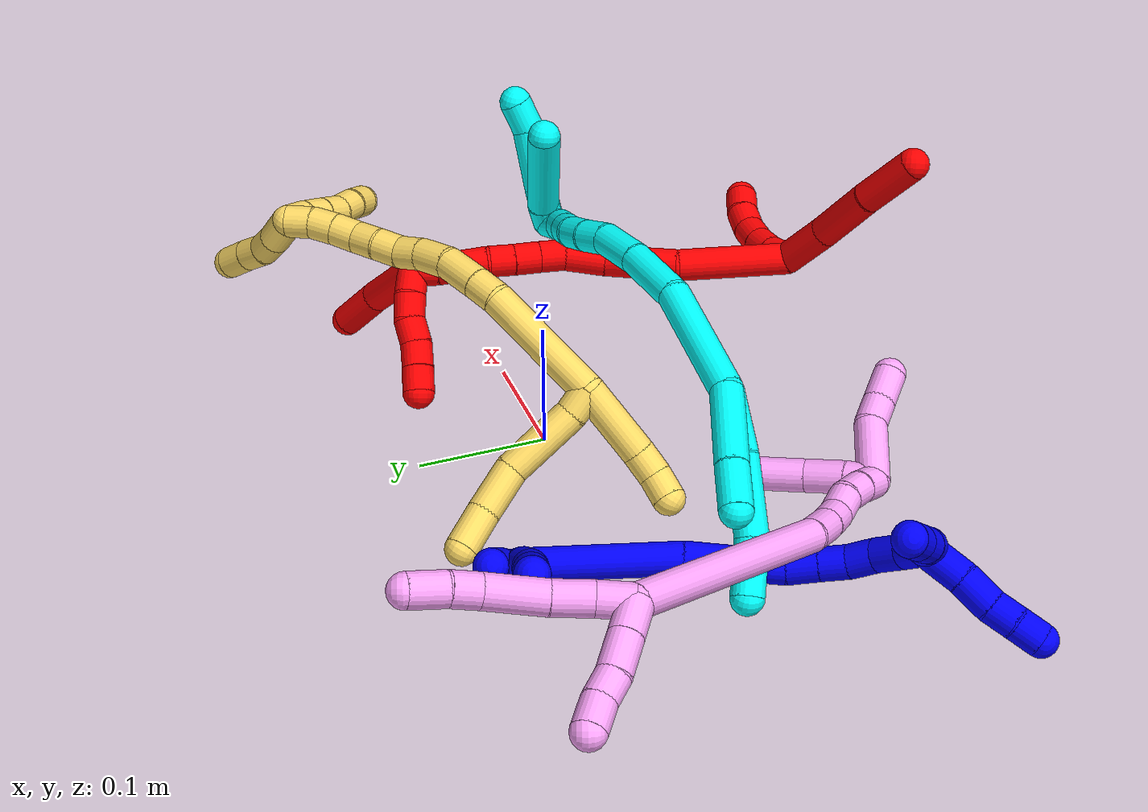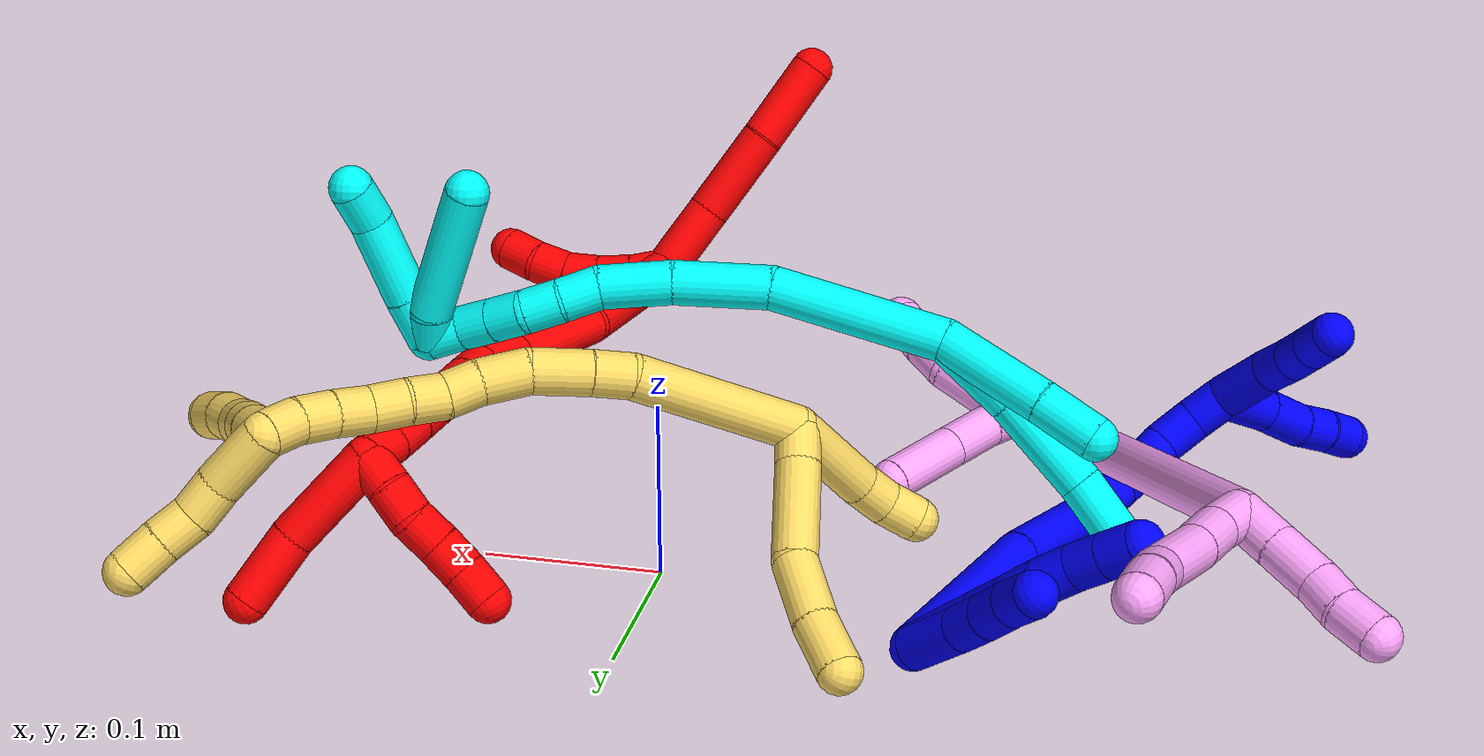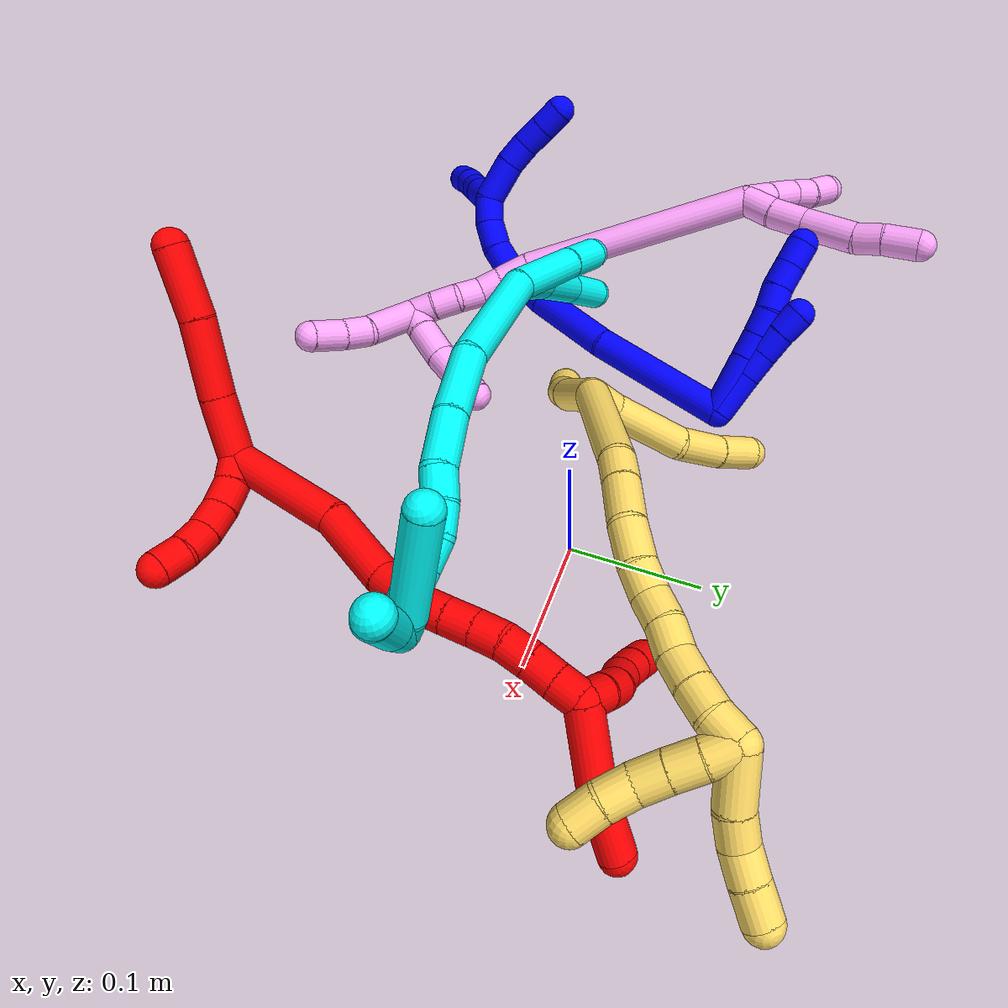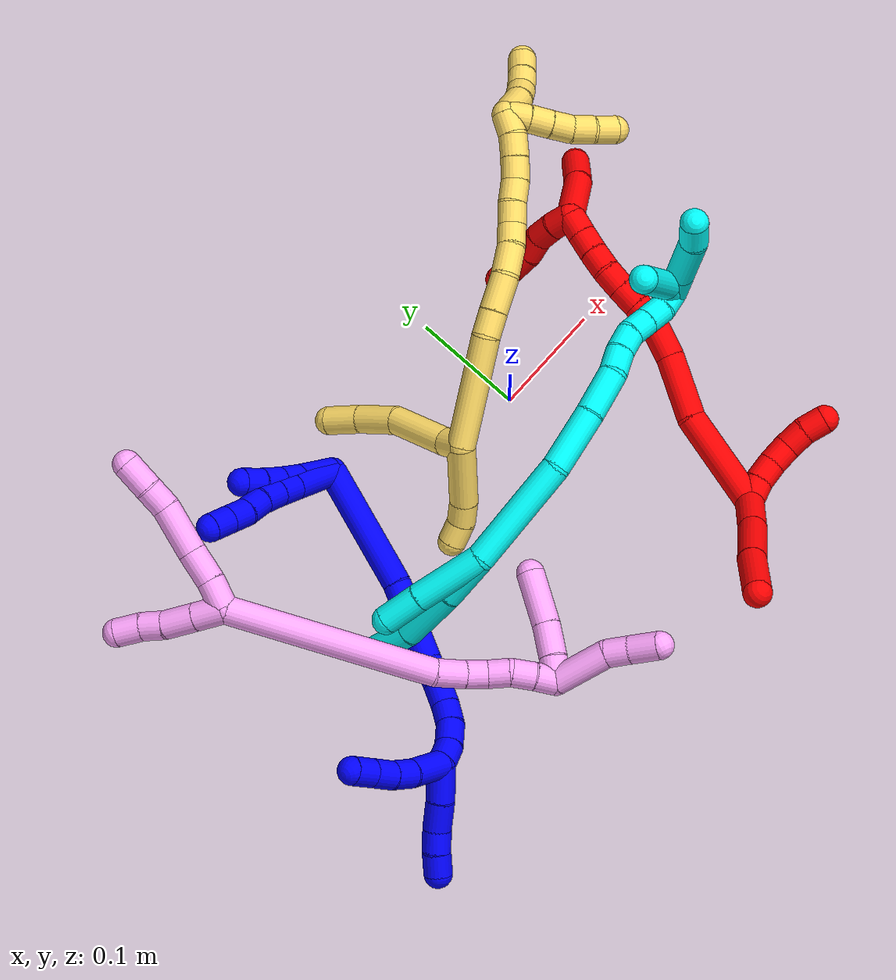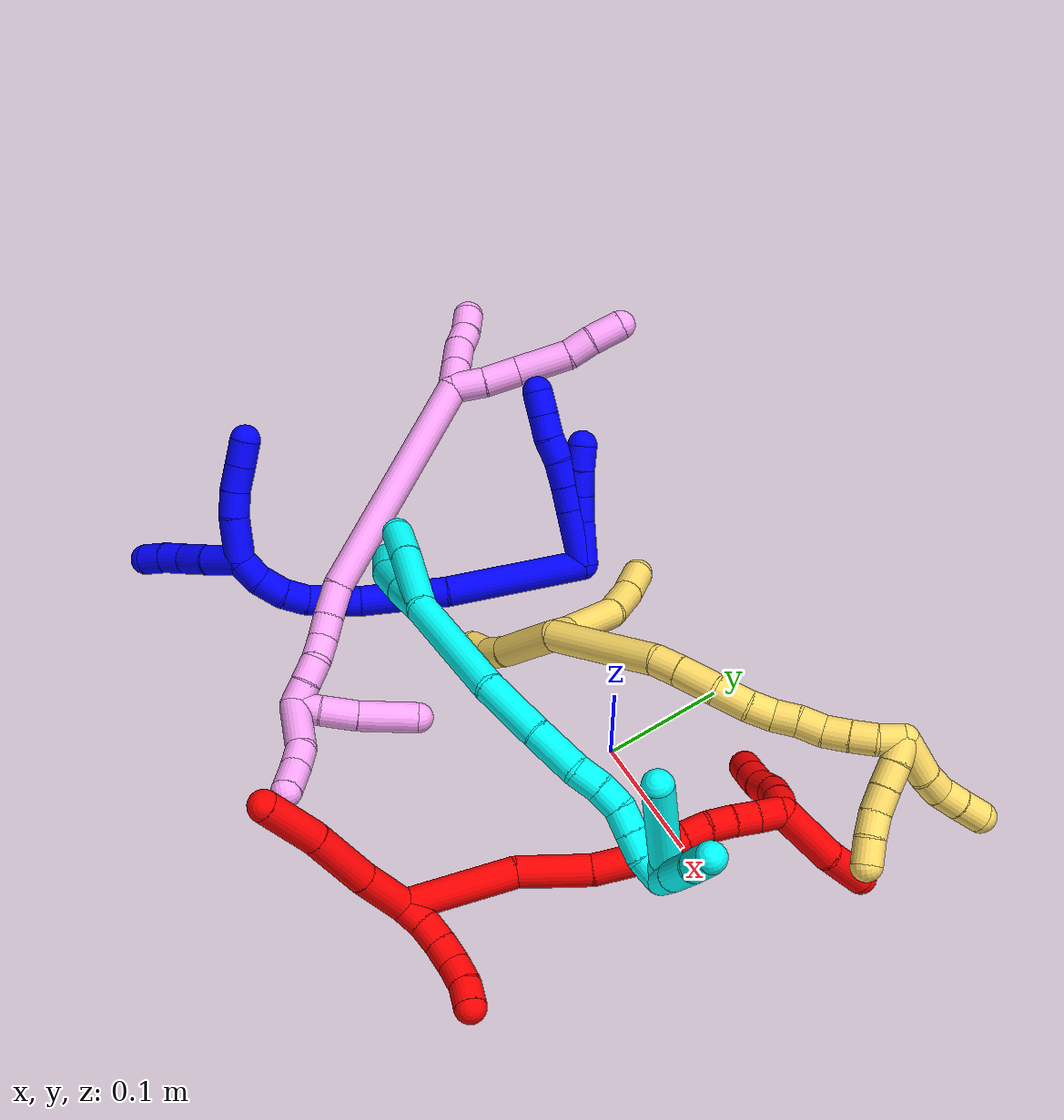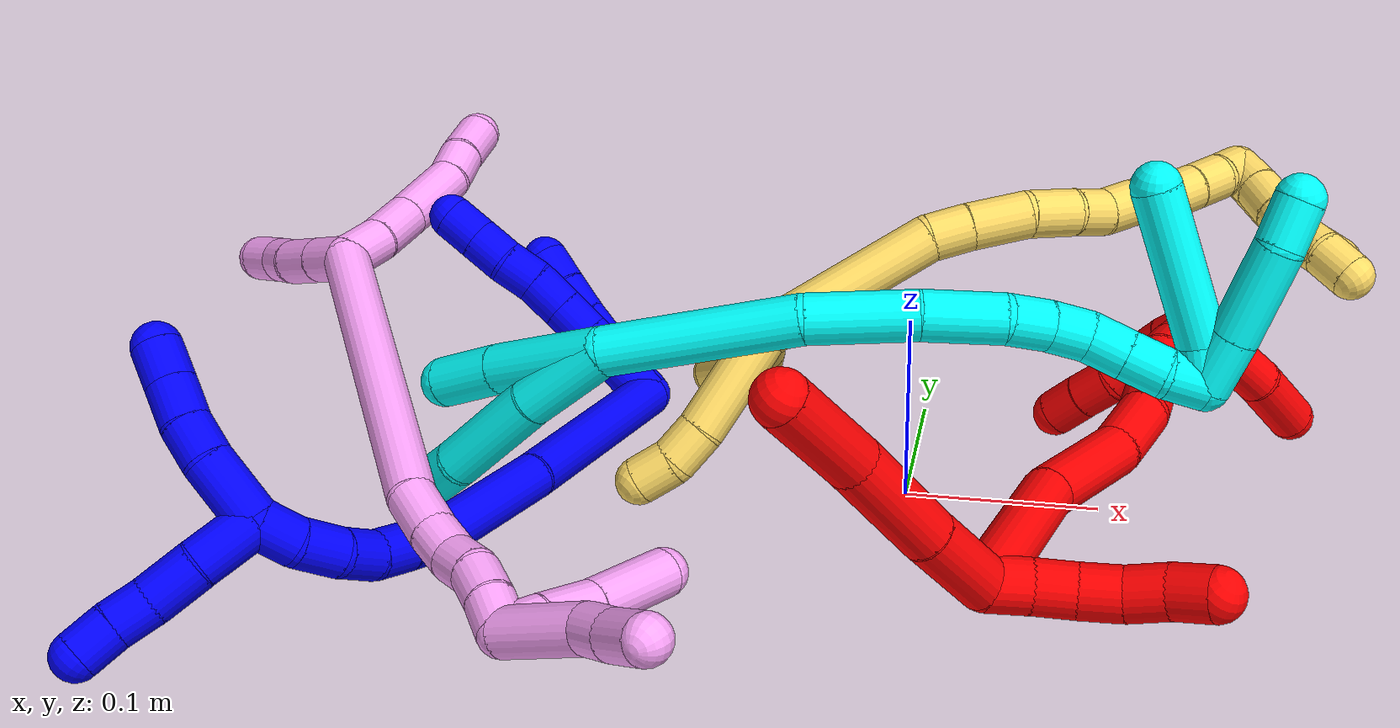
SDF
<sdf version="1.7">
 <world name="default">
  <plugin name="TubeGeneratorPlugin" filename="libtube_generator_plugin.so"/>
  <model name="photoneo_s_sensor">
   <static>1</static>
   <pose>0 0 2 1.57079 1.57079 3.14159</pose>
   <link name="link">
    <inertial><mass>0.1</mass></inertial>
    <sensor name="sensor" type="depth">
     <update_rate>30</update_rate>
     <camera>
      <horizontal_fov>1.22</horizontal_fov>
      <image><width>1920</width><height>1200</height><format>B8G8R8</format></image>
      <clip><near>0.1</near><far>4</far></clip>
      <depth_camera><output>points</output></depth_camera>
     </camera>
     <plugin name="camera_plugin" filename="libgazebo_ros_depth_camera.so">
      <baseline>0.2</baseline>
      <alwaysOn>1</alwaysOn>
      <updateRate>0.0</updateRate>
      <cameraName>camera_ir</cameraName>
      <imageTopicName>/camera/color/image_raw</imageTopicName>
      <cameraInfoTopicName>/camera/color/camera_info</cameraInfoTopicName>
      <depthImageTopicName>/camera/depth/image_raw</depthImageTopicName>
      <depthImageCameraInfoTopicName>/camera/depth/camera_info</depthImageCameraInfoTopicName>
      <pointCloudTopicName>/camera/depth/points</pointCloudTopicName>
      <frameName>fr_optical</frameName>
      <pointCloudCutoff>0.1</pointCloudCutoff>
      <pointCloudCutoffMax>2.0</pointCloudCutoffMax>
      <distortionK1>0</distortionK1>
      <distortionK2>0</distortionK2>
      <distortionK3>0</distortionK3>
      <distortionT1>0</distortionT1>
      <distortionT2>0</distortionT2>
      <CxPrime>0</CxPrime>
      <Cx>0</Cx>
      <Cy>0</Cy>
      <focalLength>0</focalLength>
      <hackBaseline>0</hackBaseline>
     </plugin>
    </sensor>
   </link>
  </model>
  <gravity>0 0 -9.8</gravity>
  <magnetic_field>6e-06 2.3e-05 -4.2e-05</magnetic_field>
  <atmosphere type="adiabatic"/>
  <physics name="default_physics" default="0" type="ode">
   <max_step_size>0.003</max_step_size>
   <real_time_factor>1</real_time_factor>
   <real_time_update_rate>1000</real_time_update_rate>
   <max_contacts>10000</max_contacts>
   <ode>
    <solver>
     <type>quick</type>
     <iters>100</iters>
     <sor>1.3</sor>
     <use_dynamic_moi_rescaling>0</use_dynamic_moi_rescaling>
    </solver>
    <constraints>
     <contact_max_correcting_vel>0</contact_max_correcting_vel>
     <contact_surface_layer>0.001</contact_surface_layer>
     <cfm>0</cfm>
     <erp>0.2</erp>
    </constraints>
   </ode>
  </physics>
  <scene><ambient>0.4 0.4 0.4 1</ambient><background>0.7 0.7 0.7 1</background><shadows>0</shadows></scene>
  <audio><device>default</device></audio>
  <spherical_coordinates>
   <surface_model>EARTH_WGS84</surface_model>
   <latitude_deg>0</latitude_deg>
   <longitude_deg>0</longitude_deg>
   <elevation>0</elevation>
   <heading_deg>0</heading_deg>
  </spherical_coordinates>
  <model name="bin">
   <static>1</static>
   <link name="bottom">
    <collision name="collision-bottom">
     <pose>0 0 -0.01 0 -0 0</pose>
     <geometry><box><size>0.8 0.6 0.02</size></box></geometry>
     <surface>
      <friction><ode><mu>100</mu><mu2>100</mu2></ode></friction>
      <contact><collide_bitmask>65535</collide_bitmask></contact>
     </surface>
    </collision>
   </link>
   <link name="west_wall">
    <collision name="collision-west_wall">
     <pose>-0.41 0 0.1 0 -0 0</pose>
     <geometry><box><size>0.02 0.6 0.2</size></box></geometry>
     <surface>
      <friction><ode><mu>100</mu><mu2>100</mu2></ode></friction>
      <contact><collide_bitmask>65535</collide_bitmask></contact>
     </surface>
    </collision>
   </link>
   <link name="east_wall">
    <collision name="collision-east_wall">
     <pose>0.41 0 0.1 0 -0 0</pose>
     <geometry><box><size>0.02 0.6 0.2</size></box></geometry>
     <surface>
      <friction><ode><mu>100</mu><mu2>100</mu2></ode></friction>
      <contact><collide_bitmask>65535</collide_bitmask></contact>
     </surface>
    </collision>
   </link>
   <link name="south_wall">
    <collision name="collision-south_wall">
     <pose>0 -0.31 0.1 0 -0 0</pose>
     <geometry><box><size>0.8 0.02 0.2</size></box></geometry>
     <surface>
      <friction><ode><mu>100</mu><mu2>100</mu2></ode></friction>
      <contact><collide_bitmask>65535</collide_bitmask></contact>
     </surface>
    </collision>
   </link>
   <link name="north_wall">
    <collision name="collision-north_wall">
     <pose>0 0.31 0.1 0 -0 0</pose>
     <geometry><box><size>0.8 0.02 0.2</size></box></geometry>
     <surface>
      <friction><ode><mu>100</mu><mu2>100</mu2></ode></friction>
      <contact><collide_bitmask>65535</collide_bitmask></contact>
     </surface>
    </collision>
   </link>
  </model>
  <model name="1">
   <static>0</static>
   <link name="1">
    <collision name="collision-cylinder-e_1_2_8">
     <pose>7.4e-05 0.002067 0.023846 -0.086455 0.003076 -0.000133</pose>
     <geometry><cylinder><radius>0.0125</radius><length>0.047871</length></cylinder></geometry>
     <surface>
      <friction><ode><mu>1.16</mu><mu2>1.16</mu2><slip1>0</slip1><slip2>0</slip2></ode></friction>
      <contact><ode><kp>1e+06</kp><kd>1</kd><max_vel>0</max_vel><min_depth>0.001</min_depth></ode></contact>
     </surface>
    </collision>
    <visual name="visual-cylinder-e_1_2_8">
     <pose>7.4e-05 0.002067 0.023846 -0.086455 0.003076 -0.000133</pose>
     <geometry><cylinder><radius>0.0125</radius><length>0.047871</length></cylinder></geometry>
     <material><ambient>0 0 1 1</ambient></material>
    </visual>
    <collision name="collision-cylinder-e_2_8_9">
     <pose>0.000148 0.005026 0.0579 -0.087249 3.4e-05 -1e-06</pose>
     <geometry><cylinder><radius>0.0125</radius><length>0.020493</length></cylinder></geometry>
     <surface>
      <friction><ode><mu>1.16</mu><mu2>1.16</mu2><slip1>0</slip1><slip2>0</slip2></ode></friction>
      <contact><ode><kp>1e+06</kp><kd>1</kd><max_vel>0</max_vel><min_depth>0.001</min_depth></ode></contact>
     </surface>
    </collision>
    <visual name="visual-cylinder-e_2_8_9">
     <pose>0.000148 0.005026 0.0579 -0.087249 3.4e-05 -1e-06</pose>
     <geometry><cylinder><radius>0.0125</radius><length>0.020493</length></cylinder></geometry>
     <material><ambient>0 0 1 1</ambient></material>
    </visual>
    <collision name="collision-cylinder-e_3_9_10">
     <pose>1.8e-05 0.006374 0.078804 -0.042488 -0.012103 0.000257</pose>
     <geometry><cylinder><radius>0.0125</radius><length>0.021415</length></cylinder></geometry>
     <surface>
      <friction><ode><mu>1.16</mu><mu2>1.16</mu2><slip1>0</slip1><slip2>0</slip2></ode></friction>
      <contact><ode><kp>1e+06</kp><kd>1</kd><max_vel>0</max_vel><min_depth>0.001</min_depth></ode></contact>
     </surface>
    </collision>
    <visual name="visual-cylinder-e_3_9_10">
     <pose>1.8e-05 0.006374 0.078804 -0.042488 -0.012103 0.000257</pose>
     <geometry><cylinder><radius>0.0125</radius><length>0.021415</length></cylinder></geometry>
     <material><ambient>0 0 1 1</ambient></material>
    </visual>
    <collision name="collision-cylinder-e_4_10_11">
     <pose>-0.001721 0.006243 0.099373 0.059308 -0.161403 -0.004798</pose>
     <geometry><cylinder><radius>0.0125</radius><length>0.02004</length></cylinder></geometry>
     <surface>
      <friction><ode><mu>1.16</mu><mu2>1.16</mu2><slip1>0</slip1><slip2>0</slip2></ode></friction>
      <contact><ode><kp>1e+06</kp><kd>1</kd><max_vel>0</max_vel><min_depth>0.001</min_depth></ode></contact>
     </surface>
    </collision>
    <visual name="visual-cylinder-e_4_10_11">
     <pose>-0.001721 0.006243 0.099373 0.059308 -0.161403 -0.004798</pose>
     <geometry><cylinder><radius>0.0125</radius><length>0.02004</length></cylinder></geometry>
     <material><ambient>0 0 1 1</ambient></material>
    </visual>
    <collision name="collision-cylinder-e_5_11_12">
     <pose>-0.004341 0.006939 0.119127 -0.12911 -0.101004 0.006535</pose>
     <geometry><cylinder><radius>0.0125</radius><length>0.02003</length></cylinder></geometry>
     <surface>
      <friction><ode><mu>1.16</mu><mu2>1.16</mu2><slip1>0</slip1><slip2>0</slip2></ode></friction>
      <contact><ode><kp>1e+06</kp><kd>1</kd><max_vel>0</max_vel><min_depth>0.001</min_depth></ode></contact>
     </surface>
    </collision>
    <visual name="visual-cylinder-e_5_11_12">
     <pose>-0.004341 0.006939 0.119127 -0.12911 -0.101004 0.006535</pose>
     <geometry><cylinder><radius>0.0125</radius><length>0.02003</length></cylinder></geometry>
     <material><ambient>0 0 1 1</ambient></material>
    </visual>
    <collision name="collision-cylinder-e_6_12_6">
     <pose>-0.006372 0.00952 0.138947 -0.129811 -0.101508 0.006603</pose>
     <geometry><cylinder><radius>0.0125</radius><length>0.020151</length></cylinder></geometry>
     <surface>
      <friction><ode><mu>1.16</mu><mu2>1.16</mu2><slip1>0</slip1><slip2>0</slip2></ode></friction>
      <contact><ode><kp>1e+06</kp><kd>1</kd><max_vel>0</max_vel><min_depth>0.001</min_depth></ode></contact>
     </surface>
    </collision>
    <visual name="visual-cylinder-e_6_12_6">
     <pose>-0.006372 0.00952 0.138947 -0.129811 -0.101508 0.006603</pose>
     <geometry><cylinder><radius>0.0125</radius><length>0.020151</length></cylinder></geometry>
     <material><ambient>0 0 1 1</ambient></material>
    </visual>
    <collision name="collision-cylinder-e_1_2_13">
     <pose>0.000536 0.004308 0.017839 -0.236956 0.029216 -0.003478</pose>
     <geometry><cylinder><radius>0.0125</radius><length>0.03672</length></cylinder></geometry>
     <surface>
      <friction><ode><mu>1.16</mu><mu2>1.16</mu2><slip1>0</slip1><slip2>0</slip2></ode></friction>
      <contact><ode><kp>1e+06</kp><kd>1</kd><max_vel>0</max_vel><min_depth>0.001</min_depth></ode></contact>
     </surface>
    </collision>
    <visual name="visual-cylinder-e_1_2_13">
     <pose>0.000536 0.004308 0.017839 -0.236956 0.029216 -0.003478</pose>
     <geometry><cylinder><radius>0.0125</radius><length>0.03672</length></cylinder></geometry>
     <material><ambient>0 0 1 1</ambient></material>
    </visual>
    <collision name="collision-cylinder-e_2_13_14">
     <pose>0.002017 0.011383 0.046001 -0.261838 0.088167 -0.011616</pose>
     <geometry><cylinder><radius>0.0125</radius><length>0.021457</length></cylinder></geometry>
     <surface>
      <friction><ode><mu>1.16</mu><mu2>1.16</mu2><slip1>0</slip1><slip2>0</slip2></ode></friction>
      <contact><ode><kp>1e+06</kp><kd>1</kd><max_vel>0</max_vel><min_depth>0.001</min_depth></ode></contact>
     </surface>
    </collision>
    <visual name="visual-cylinder-e_2_13_14">
     <pose>0.002017 0.011383 0.046001 -0.261838 0.088167 -0.011616</pose>
     <geometry><cylinder><radius>0.0125</radius><length>0.021457</length></cylinder></geometry>
     <material><ambient>0 0 1 1</ambient></material>
    </visual>
    <collision name="collision-cylinder-e_3_14_15">
     <pose>0.004508 0.017018 0.066477 -0.275365 0.145483 -0.020193</pose>
     <geometry><cylinder><radius>0.0125</radius><length>0.021326</length></cylinder></geometry>
     <surface>
      <friction><ode><mu>1.16</mu><mu2>1.16</mu2><slip1>0</slip1><slip2>0</slip2></ode></friction>
      <contact><ode><kp>1e+06</kp><kd>1</kd><max_vel>0</max_vel><min_depth>0.001</min_depth></ode></contact>
     </surface>
    </collision>
    <visual name="visual-cylinder-e_3_14_15">
     <pose>0.004508 0.017018 0.066477 -0.275365 0.145483 -0.020193</pose>
     <geometry><cylinder><radius>0.0125</radius><length>0.021326</length></cylinder></geometry>
     <material><ambient>0 0 1 1</ambient></material>
    </visual>
    <collision name="collision-cylinder-e_4_15_5">
     <pose>0.007408 0.02364 0.086069 -0.378475 0.132584 -0.02543</pose>
     <geometry><cylinder><radius>0.0125</radius><length>0.020497</length></cylinder></geometry>
     <surface>
      <friction><ode><mu>1.16</mu><mu2>1.16</mu2><slip1>0</slip1><slip2>0</slip2></ode></friction>
      <contact><ode><kp>1e+06</kp><kd>1</kd><max_vel>0</max_vel><min_depth>0.001</min_depth></ode></contact>
     </surface>
    </collision>
    <visual name="visual-cylinder-e_4_15_5">
     <pose>0.007408 0.02364 0.086069 -0.378475 0.132584 -0.02543</pose>
     <geometry><cylinder><radius>0.0125</radius><length>0.020497</length></cylinder></geometry>
     <material><ambient>0 0 1 1</ambient></material>
    </visual>
    <collision name="collision-cylinder-e_1_2_16">
     <pose>-0.023833 -0.052454 0.007282 1.43285 -0.422896 -0.369565</pose>
     <geometry><cylinder><radius>0.0125</radius><length>0.116147</length></cylinder></geometry>
     <surface>
      <friction><ode><mu>1.16</mu><mu2>1.16</mu2><slip1>0</slip1><slip2>0</slip2></ode></friction>
      <contact><ode><kp>1e+06</kp><kd>1</kd><max_vel>0</max_vel><min_depth>0.001</min_depth></ode></contact>
     </surface>
    </collision>
    <visual name="visual-cylinder-e_1_2_16">
     <pose>-0.023833 -0.052454 0.007282 1.43285 -0.422896 -0.369565</pose>
     <geometry><cylinder><radius>0.0125</radius><length>0.116147</length></cylinder></geometry>
     <material><ambient>0 0 1 1</ambient></material>
    </visual>
    <collision name="collision-cylinder-e_2_16_17">
     <pose>-0.066781 -0.135028 0.021354 1.34908 -0.55432 -0.447368</pose>
     <geometry><cylinder><radius>0.0125</radius><length>0.072625</length></cylinder></geometry>
     <surface>
      <friction><ode><mu>1.16</mu><mu2>1.16</mu2><slip1>0</slip1><slip2>0</slip2></ode></friction>
      <contact><ode><kp>1e+06</kp><kd>1</kd><max_vel>0</max_vel><min_depth>0.001</min_depth></ode></contact>
     </surface>
    </collision>
    <visual name="visual-cylinder-e_2_16_17">
     <pose>-0.066781 -0.135028 0.021354 1.34908 -0.55432 -0.447368</pose>
     <geometry><cylinder><radius>0.0125</radius><length>0.072625</length></cylinder></geometry>
     <material><ambient>0 0 1 1</ambient></material>
    </visual>
    <collision name="collision-cylinder-e_3_17_18">
     <pose>-0.089901 -0.175559 0.032056 1.2114 -0.34574 -0.240684</pose>
     <geometry><cylinder><radius>0.0125</radius><length>0.023645</length></cylinder></geometry>
     <surface>
      <friction><ode><mu>1.16</mu><mu2>1.16</mu2><slip1>0</slip1><slip2>0</slip2></ode></friction>
      <contact><ode><kp>1e+06</kp><kd>1</kd><max_vel>0</max_vel><min_depth>0.001</min_depth></ode></contact>
     </surface>
    </collision>
    <visual name="visual-cylinder-e_3_17_18">
     <pose>-0.089901 -0.175559 0.032056 1.2114 -0.34574 -0.240684</pose>
     <geometry><cylinder><radius>0.0125</radius><length>0.023645</length></cylinder></geometry>
     <material><ambient>0 0 1 1</ambient></material>
    </visual>
    <collision name="collision-cylinder-e_4_18_19">
     <pose>-0.097643 -0.195069 0.039848 1.16765 -0.361134 -0.24005</pose>
     <geometry><cylinder><radius>0.0125</radius><length>0.021145</length></cylinder></geometry>
     <surface>
      <friction><ode><mu>1.16</mu><mu2>1.16</mu2><slip1>0</slip1><slip2>0</slip2></ode></friction>
      <contact><ode><kp>1e+06</kp><kd>1</kd><max_vel>0</max_vel><min_depth>0.001</min_depth></ode></contact>
     </surface>
    </collision>
    <visual name="visual-cylinder-e_4_18_19">
     <pose>-0.097643 -0.195069 0.039848 1.16765 -0.361134 -0.24005</pose>
     <geometry><cylinder><radius>0.0125</radius><length>0.021145</length></cylinder></geometry>
     <material><ambient>0 0 1 1</ambient></material>
    </visual>
    <collision name="collision-cylinder-e_5_19_20">
     <pose>-0.103314 -0.212619 0.049746 0.952068 -0.184372 -0.095256</pose>
     <geometry><cylinder><radius>0.0125</radius><length>0.021108</length></cylinder></geometry>
     <surface>
      <friction><ode><mu>1.16</mu><mu2>1.16</mu2><slip1>0</slip1><slip2>0</slip2></ode></friction>
      <contact><ode><kp>1e+06</kp><kd>1</kd><max_vel>0</max_vel><min_depth>0.001</min_depth></ode></contact>
     </surface>
    </collision>
    <visual name="visual-cylinder-e_5_19_20">
     <pose>-0.103314 -0.212619 0.049746 0.952068 -0.184372 -0.095256</pose>
     <geometry><cylinder><radius>0.0125</radius><length>0.021108</length></cylinder></geometry>
     <material><ambient>0 0 1 1</ambient></material>
    </visual>
    <collision name="collision-cylinder-e_6_20_21">
     <pose>-0.10787 -0.228235 0.064594 0.681541 -0.22657 -0.080644</pose>
     <geometry><cylinder><radius>0.0125</radius><length>0.023339</length></cylinder></geometry>
     <surface>
      <friction><ode><mu>1.16</mu><mu2>1.16</mu2><slip1>0</slip1><slip2>0</slip2></ode></friction>
      <contact><ode><kp>1e+06</kp><kd>1</kd><max_vel>0</max_vel><min_depth>0.001</min_depth></ode></contact>
     </surface>
    </collision>
    <visual name="visual-cylinder-e_6_20_21">
     <pose>-0.10787 -0.228235 0.064594 0.681541 -0.22657 -0.080644</pose>
     <geometry><cylinder><radius>0.0125</radius><length>0.023339</length></cylinder></geometry>
     <material><ambient>0 0 1 1</ambient></material>
    </visual>
    <collision name="collision-cylinder-e_7_21_1">
     <pose>-0.111975 -0.23979 0.083396 0.41486 -0.135334 -0.028524</pose>
     <geometry><cylinder><radius>0.0125</radius><length>0.021991</length></cylinder></geometry>
     <surface>
      <friction><ode><mu>1.16</mu><mu2>1.16</mu2><slip1>0</slip1><slip2>0</slip2></ode></friction>
      <contact><ode><kp>1e+06</kp><kd>1</kd><max_vel>0</max_vel><min_depth>0.001</min_depth></ode></contact>
     </surface>
    </collision>
    <visual name="visual-cylinder-e_7_21_1">
     <pose>-0.111975 -0.23979 0.083396 0.41486 -0.135334 -0.028524</pose>
     <geometry><cylinder><radius>0.0125</radius><length>0.021991</length></cylinder></geometry>
     <material><ambient>0 0 1 1</ambient></material>
    </visual>
    <collision name="collision-cylinder-e_1_1_22">
     <pose>-0.111791 -0.241357 0.111247 -0.156619 0.091868 -0.007214</pose>
     <geometry><cylinder><radius>0.0125</radius><length>0.036357</length></cylinder></geometry>
     <surface>
      <friction><ode><mu>1.16</mu><mu2>1.16</mu2><slip1>0</slip1><slip2>0</slip2></ode></friction>
      <contact><ode><kp>1e+06</kp><kd>1</kd><max_vel>0</max_vel><min_depth>0.001</min_depth></ode></contact>
     </surface>
    </collision>
    <visual name="visual-cylinder-e_1_1_22">
     <pose>-0.111791 -0.241357 0.111247 -0.156619 0.091868 -0.007214</pose>
     <geometry><cylinder><radius>0.0125</radius><length>0.036357</length></cylinder></geometry>
     <material><ambient>0 0 1 1</ambient></material>
    </visual>
    <collision name="collision-cylinder-e_2_22_23">
     <pose>-0.108695 -0.235065 0.139061 -0.33597 0.134866 -0.022905</pose>
     <geometry><cylinder><radius>0.0125</radius><length>0.021237</length></cylinder></geometry>
     <surface>
      <friction><ode><mu>1.16</mu><mu2>1.16</mu2><slip1>0</slip1><slip2>0</slip2></ode></friction>
      <contact><ode><kp>1e+06</kp><kd>1</kd><max_vel>0</max_vel><min_depth>0.001</min_depth></ode></contact>
     </surface>
    </collision>
    <visual name="visual-cylinder-e_2_22_23">
     <pose>-0.108695 -0.235065 0.139061 -0.33597 0.134866 -0.022905</pose>
     <geometry><cylinder><radius>0.0125</radius><length>0.021237</length></cylinder></geometry>
     <material><ambient>0 0 1 1</ambient></material>
    </visual>
    <collision name="collision-cylinder-e_3_23_24">
     <pose>-0.104484 -0.227074 0.158411 -0.447662 0.260372 -0.059592</pose>
     <geometry><cylinder><radius>0.0125</radius><length>0.02162</length></cylinder></geometry>
     <surface>
      <friction><ode><mu>1.16</mu><mu2>1.16</mu2><slip1>0</slip1><slip2>0</slip2></ode></friction>
      <contact><ode><kp>1e+06</kp><kd>1</kd><max_vel>0</max_vel><min_depth>0.001</min_depth></ode></contact>
     </surface>
    </collision>
    <visual name="visual-cylinder-e_3_23_24">
     <pose>-0.104484 -0.227074 0.158411 -0.447662 0.260372 -0.059592</pose>
     <geometry><cylinder><radius>0.0125</radius><length>0.02162</length></cylinder></geometry>
     <material><ambient>0 0 1 1</ambient></material>
    </visual>
    <collision name="collision-cylinder-e_4_24_4">
     <pose>-0.099035 -0.218299 0.176927 -0.437278 0.259497 -0.057967</pose>
     <geometry><cylinder><radius>0.0125</radius><length>0.020786</length></cylinder></geometry>
     <surface>
      <friction><ode><mu>1.16</mu><mu2>1.16</mu2><slip1>0</slip1><slip2>0</slip2></ode></friction>
      <contact><ode><kp>1e+06</kp><kd>1</kd><max_vel>0</max_vel><min_depth>0.001</min_depth></ode></contact>
     </surface>
    </collision>
    <visual name="visual-cylinder-e_4_24_4">
     <pose>-0.099035 -0.218299 0.176927 -0.437278 0.259497 -0.057967</pose>
     <geometry><cylinder><radius>0.0125</radius><length>0.020786</length></cylinder></geometry>
     <material><ambient>0 0 1 1</ambient></material>
    </visual>
    <collision name="collision-cylinder-e_1_1_25">
     <pose>-0.127984 -0.250769 0.095837 1.21208 -1.11974 -0.819571</pose>
     <geometry><cylinder><radius>0.0125</radius><length>0.03228</length></cylinder></geometry>
     <surface>
      <friction><ode><mu>1.16</mu><mu2>1.16</mu2><slip1>0</slip1><slip2>0</slip2></ode></friction>
      <contact><ode><kp>1e+06</kp><kd>1</kd><max_vel>0</max_vel><min_depth>0.001</min_depth></ode></contact>
     </surface>
    </collision>
    <visual name="visual-cylinder-e_1_1_25">
     <pose>-0.127984 -0.250769 0.095837 1.21208 -1.11974 -0.819571</pose>
     <geometry><cylinder><radius>0.0125</radius><length>0.03228</length></cylinder></geometry>
     <material><ambient>0 0 1 1</ambient></material>
    </visual>
    <collision name="collision-cylinder-e_2_25_26">
     <pose>-0.155306 -0.26135 0.100158 1.13662 -1.2395 -0.855085</pose>
     <geometry><cylinder><radius>0.0125</radius><length>0.027064</length></cylinder></geometry>
     <surface>
      <friction><ode><mu>1.16</mu><mu2>1.16</mu2><slip1>0</slip1><slip2>0</slip2></ode></friction>
      <contact><ode><kp>1e+06</kp><kd>1</kd><max_vel>0</max_vel><min_depth>0.001</min_depth></ode></contact>
     </surface>
    </collision>
    <visual name="visual-cylinder-e_2_25_26">
     <pose>-0.155306 -0.26135 0.100158 1.13662 -1.2395 -0.855085</pose>
     <geometry><cylinder><radius>0.0125</radius><length>0.027064</length></cylinder></geometry>
     <material><ambient>0 0 1 1</ambient></material>
    </visual>
    <collision name="collision-cylinder-e_3_26_27">
     <pose>-0.176911 -0.269849 0.104103 1.13594 -1.0573 -0.71355</pose>
     <geometry><cylinder><radius>0.0125</radius><length>0.020227</length></cylinder></geometry>
     <surface>
      <friction><ode><mu>1.16</mu><mu2>1.16</mu2><slip1>0</slip1><slip2>0</slip2></ode></friction>
      <contact><ode><kp>1e+06</kp><kd>1</kd><max_vel>0</max_vel><min_depth>0.001</min_depth></ode></contact>
     </surface>
    </collision>
    <visual name="visual-cylinder-e_3_26_27">
     <pose>-0.176911 -0.269849 0.104103 1.13594 -1.0573 -0.71355</pose>
     <geometry><cylinder><radius>0.0125</radius><length>0.020227</length></cylinder></geometry>
     <material><ambient>0 0 1 1</ambient></material>
    </visual>
    <collision name="collision-cylinder-e_4_27_3">
     <pose>-0.194693 -0.27915 0.107105 1.38329 -1.07256 -0.9148</pose>
     <geometry><cylinder><radius>0.0125</radius><length>0.020429</length></cylinder></geometry>
     <surface>
      <friction><ode><mu>1.16</mu><mu2>1.16</mu2><slip1>0</slip1><slip2>0</slip2></ode></friction>
      <contact><ode><kp>1e+06</kp><kd>1</kd><max_vel>0</max_vel><min_depth>0.001</min_depth></ode></contact>
     </surface>
    </collision>
    <visual name="visual-cylinder-e_4_27_3">
     <pose>-0.194693 -0.27915 0.107105 1.38329 -1.07256 -0.9148</pose>
     <geometry><cylinder><radius>0.0125</radius><length>0.020429</length></cylinder></geometry>
     <material><ambient>0 0 1 1</ambient></material>
    </visual>
    <collision name="collision-sphere-3">
     <pose>-0.203666 -0.283946 0.108015 0 -0 0</pose>
     <geometry><sphere><radius>0.0125</radius></sphere></geometry>
     <surface>
      <friction><ode><mu>1.16</mu><mu2>1.16</mu2><slip1>0</slip1><slip2>0</slip2></ode></friction>
      <contact><ode><kp>1e+06</kp><kd>1</kd><max_vel>0</max_vel><min_depth>0.001</min_depth></ode></contact>
     </surface>
    </collision>
    <visual name="visual-sphere-3">
     <pose>-0.203666 -0.283946 0.108015 0 -0 0</pose>
     <geometry><sphere><radius>0.0125</radius></sphere></geometry>
     <material><ambient>0 0 1 1</ambient></material>
    </visual>
    <collision name="collision-sphere-27">
     <pose>-0.18572 -0.274354 0.106196 0 -0 0</pose>
     <geometry><sphere><radius>0.0125</radius></sphere></geometry>
     <surface>
      <friction><ode><mu>1.16</mu><mu2>1.16</mu2><slip1>0</slip1><slip2>0</slip2></ode></friction>
      <contact><ode><kp>1e+06</kp><kd>1</kd><max_vel>0</max_vel><min_depth>0.001</min_depth></ode></contact>
     </surface>
    </collision>
    <visual name="visual-sphere-27">
     <pose>-0.18572 -0.274354 0.106196 0 -0 0</pose>
     <geometry><sphere><radius>0.0125</radius></sphere></geometry>
     <material><ambient>0 0 1 1</ambient></material>
    </visual>
    <collision name="collision-sphere-26">
     <pose>-0.168102 -0.265343 0.10201 0 -0 0</pose>
     <geometry><sphere><radius>0.0125</radius></sphere></geometry>
     <surface>
      <friction><ode><mu>1.16</mu><mu2>1.16</mu2><slip1>0</slip1><slip2>0</slip2></ode></friction>
      <contact><ode><kp>1e+06</kp><kd>1</kd><max_vel>0</max_vel><min_depth>0.001</min_depth></ode></contact>
     </surface>
    </collision>
    <visual name="visual-sphere-26">
     <pose>-0.168102 -0.265343 0.10201 0 -0 0</pose>
     <geometry><sphere><radius>0.0125</radius></sphere></geometry>
     <material><ambient>0 0 1 1</ambient></material>
    </visual>
    <collision name="collision-sphere-25">
     <pose>-0.14251 -0.257357 0.098307 0 -0 0</pose>
     <geometry><sphere><radius>0.0125</radius></sphere></geometry>
     <surface>
      <friction><ode><mu>1.16</mu><mu2>1.16</mu2><slip1>0</slip1><slip2>0</slip2></ode></friction>
      <contact><ode><kp>1e+06</kp><kd>1</kd><max_vel>0</max_vel><min_depth>0.001</min_depth></ode></contact>
     </surface>
    </collision>
    <visual name="visual-sphere-25">
     <pose>-0.14251 -0.257357 0.098307 0 -0 0</pose>
     <geometry><sphere><radius>0.0125</radius></sphere></geometry>
     <material><ambient>0 0 1 1</ambient></material>
    </visual>
    <collision name="collision-sphere-4">
     <pose>-0.096368 -0.214045 0.186027 0 -0 0</pose>
     <geometry><sphere><radius>0.0125</radius></sphere></geometry>
     <surface>
      <friction><ode><mu>1.16</mu><mu2>1.16</mu2><slip1>0</slip1><slip2>0</slip2></ode></friction>
      <contact><ode><kp>1e+06</kp><kd>1</kd><max_vel>0</max_vel><min_depth>0.001</min_depth></ode></contact>
     </surface>
    </collision>
    <visual name="visual-sphere-4">
     <pose>-0.096368 -0.214045 0.186027 0 -0 0</pose>
     <geometry><sphere><radius>0.0125</radius></sphere></geometry>
     <material><ambient>0 0 1 1</ambient></material>
    </visual>
    <collision name="collision-sphere-24">
     <pose>-0.101701 -0.222553 0.167828 0 -0 0</pose>
     <geometry><sphere><radius>0.0125</radius></sphere></geometry>
     <surface>
      <friction><ode><mu>1.16</mu><mu2>1.16</mu2><slip1>0</slip1><slip2>0</slip2></ode></friction>
      <contact><ode><kp>1e+06</kp><kd>1</kd><max_vel>0</max_vel><min_depth>0.001</min_depth></ode></contact>
     </surface>
    </collision>
    <visual name="visual-sphere-24">
     <pose>-0.101701 -0.222553 0.167828 0 -0 0</pose>
     <geometry><sphere><radius>0.0125</radius></sphere></geometry>
     <material><ambient>0 0 1 1</ambient></material>
    </visual>
    <collision name="collision-sphere-23">
     <pose>-0.107267 -0.231596 0.148994 0 -0 0</pose>
     <geometry><sphere><radius>0.0125</radius></sphere></geometry>
     <surface>
      <friction><ode><mu>1.16</mu><mu2>1.16</mu2><slip1>0</slip1><slip2>0</slip2></ode></friction>
      <contact><ode><kp>1e+06</kp><kd>1</kd><max_vel>0</max_vel><min_depth>0.001</min_depth></ode></contact>
     </surface>
    </collision>
    <visual name="visual-sphere-23">
     <pose>-0.107267 -0.231596 0.148994 0 -0 0</pose>
     <geometry><sphere><radius>0.0125</radius></sphere></geometry>
     <material><ambient>0 0 1 1</ambient></material>
    </visual>
    <collision name="collision-sphere-22">
     <pose>-0.110123 -0.238534 0.129127 0 -0 0</pose>
     <geometry><sphere><radius>0.0125</radius></sphere></geometry>
     <surface>
      <friction><ode><mu>1.16</mu><mu2>1.16</mu2><slip1>0</slip1><slip2>0</slip2></ode></friction>
      <contact><ode><kp>1e+06</kp><kd>1</kd><max_vel>0</max_vel><min_depth>0.001</min_depth></ode></contact>
     </surface>
    </collision>
    <visual name="visual-sphere-22">
     <pose>-0.110123 -0.238534 0.129127 0 -0 0</pose>
     <geometry><sphere><radius>0.0125</radius></sphere></geometry>
     <material><ambient>0 0 1 1</ambient></material>
    </visual>
    <collision name="collision-sphere-1">
     <pose>-0.113458 -0.244181 0.093367 0 -0 0</pose>
     <geometry><sphere><radius>0.0125</radius></sphere></geometry>
     <surface>
      <friction><ode><mu>1.16</mu><mu2>1.16</mu2><slip1>0</slip1><slip2>0</slip2></ode></friction>
      <contact><ode><kp>1e+06</kp><kd>1</kd><max_vel>0</max_vel><min_depth>0.001</min_depth></ode></contact>
     </surface>
    </collision>
    <visual name="visual-sphere-1">
     <pose>-0.113458 -0.244181 0.093367 0 -0 0</pose>
     <geometry><sphere><radius>0.0125</radius></sphere></geometry>
     <material><ambient>0 0 1 1</ambient></material>
    </visual>
    <collision name="collision-sphere-21">
     <pose>-0.110491 -0.235398 0.073425 0 -0 0</pose>
     <geometry><sphere><radius>0.0125</radius></sphere></geometry>
     <surface>
      <friction><ode><mu>1.16</mu><mu2>1.16</mu2><slip1>0</slip1><slip2>0</slip2></ode></friction>
      <contact><ode><kp>1e+06</kp><kd>1</kd><max_vel>0</max_vel><min_depth>0.001</min_depth></ode></contact>
     </surface>
    </collision>
    <visual name="visual-sphere-21">
     <pose>-0.110491 -0.235398 0.073425 0 -0 0</pose>
     <geometry><sphere><radius>0.0125</radius></sphere></geometry>
     <material><ambient>0 0 1 1</ambient></material>
    </visual>
    <collision name="collision-sphere-12">
     <pose>-0.005351 0.008222 0.129008 0 -0 0</pose>
     <geometry><sphere><radius>0.0125</radius></sphere></geometry>
     <surface>
      <friction><ode><mu>1.16</mu><mu2>1.16</mu2><slip1>0</slip1><slip2>0</slip2></ode></friction>
      <contact><ode><kp>1e+06</kp><kd>1</kd><max_vel>0</max_vel><min_depth>0.001</min_depth></ode></contact>
     </surface>
    </collision>
    <visual name="visual-sphere-12">
     <pose>-0.005351 0.008222 0.129008 0 -0 0</pose>
     <geometry><sphere><radius>0.0125</radius></sphere></geometry>
     <material><ambient>0 0 1 1</ambient></material>
    </visual>
    <collision name="collision-sphere-11">
     <pose>-0.003332 0.005656 0.109246 0 -0 0</pose>
     <geometry><sphere><radius>0.0125</radius></sphere></geometry>
     <surface>
      <friction><ode><mu>1.16</mu><mu2>1.16</mu2><slip1>0</slip1><slip2>0</slip2></ode></friction>
      <contact><ode><kp>1e+06</kp><kd>1</kd><max_vel>0</max_vel><min_depth>0.001</min_depth></ode></contact>
     </surface>
    </collision>
    <visual name="visual-sphere-11">
     <pose>-0.003332 0.005656 0.109246 0 -0 0</pose>
     <geometry><sphere><radius>0.0125</radius></sphere></geometry>
     <material><ambient>0 0 1 1</ambient></material>
    </visual>
    <collision name="collision-sphere-10">
     <pose>-0.000111 0.006829 0.089501 0 -0 0</pose>
     <geometry><sphere><radius>0.0125</radius></sphere></geometry>
     <surface>
      <friction><ode><mu>1.16</mu><mu2>1.16</mu2><slip1>0</slip1><slip2>0</slip2></ode></friction>
      <contact><ode><kp>1e+06</kp><kd>1</kd><max_vel>0</max_vel><min_depth>0.001</min_depth></ode></contact>
     </surface>
    </collision>
    <visual name="visual-sphere-10">
     <pose>-0.000111 0.006829 0.089501 0 -0 0</pose>
     <geometry><sphere><radius>0.0125</radius></sphere></geometry>
     <material><ambient>0 0 1 1</ambient></material>
    </visual>
    <collision name="collision-sphere-9">
     <pose>0.000148 0.005919 0.068107 0 -0 0</pose>
     <geometry><sphere><radius>0.0125</radius></sphere></geometry>
     <surface>
      <friction><ode><mu>1.16</mu><mu2>1.16</mu2><slip1>0</slip1><slip2>0</slip2></ode></friction>
      <contact><ode><kp>1e+06</kp><kd>1</kd><max_vel>0</max_vel><min_depth>0.001</min_depth></ode></contact>
     </surface>
    </collision>
    <visual name="visual-sphere-9">
     <pose>0.000148 0.005919 0.068107 0 -0 0</pose>
     <geometry><sphere><radius>0.0125</radius></sphere></geometry>
     <material><ambient>0 0 1 1</ambient></material>
    </visual>
    <collision name="collision-sphere-2">
     <geometry><sphere><radius>0.0125</radius></sphere></geometry>
     <surface>
      <friction><ode><mu>1.16</mu><mu2>1.16</mu2><slip1>0</slip1><slip2>0</slip2></ode></friction>
      <contact><ode><kp>1e+06</kp><kd>1</kd><max_vel>0</max_vel><min_depth>0.001</min_depth></ode></contact>
     </surface>
    </collision>
    <visual name="visual-sphere-2">
     <geometry><sphere><radius>0.0125</radius></sphere></geometry>
     <material><ambient>0 0 1 1</ambient></material>
    </visual>
    <collision name="collision-sphere-19">
     <pose>-0.101379 -0.204167 0.043728 0 -0 0</pose>
     <geometry><sphere><radius>0.0125</radius></sphere></geometry>
     <surface>
      <friction><ode><mu>1.16</mu><mu2>1.16</mu2><slip1>0</slip1><slip2>0</slip2></ode></friction>
      <contact><ode><kp>1e+06</kp><kd>1</kd><max_vel>0</max_vel><min_depth>0.001</min_depth></ode></contact>
     </surface>
    </collision>
    <visual name="visual-sphere-19">
     <pose>-0.101379 -0.204167 0.043728 0 -0 0</pose>
     <geometry><sphere><radius>0.0125</radius></sphere></geometry>
     <material><ambient>0 0 1 1</ambient></material>
    </visual>
    <collision name="collision-sphere-8">
     <pose>0.000147 0.004134 0.047692 0 -0 0</pose>
     <geometry><sphere><radius>0.0125</radius></sphere></geometry>
     <surface>
      <friction><ode><mu>1.16</mu><mu2>1.16</mu2><slip1>0</slip1><slip2>0</slip2></ode></friction>
      <contact><ode><kp>1e+06</kp><kd>1</kd><max_vel>0</max_vel><min_depth>0.001</min_depth></ode></contact>
     </surface>
    </collision>
    <visual name="visual-sphere-8">
     <pose>0.000147 0.004134 0.047692 0 -0 0</pose>
     <geometry><sphere><radius>0.0125</radius></sphere></geometry>
     <material><ambient>0 0 1 1</ambient></material>
    </visual>
    <collision name="collision-sphere-6">
     <pose>-0.007393 0.010817 0.148887 0 -0 0</pose>
     <geometry><sphere><radius>0.0125</radius></sphere></geometry>
     <surface>
      <friction><ode><mu>1.16</mu><mu2>1.16</mu2><slip1>0</slip1><slip2>0</slip2></ode></friction>
      <contact><ode><kp>1e+06</kp><kd>1</kd><max_vel>0</max_vel><min_depth>0.001</min_depth></ode></contact>
     </surface>
    </collision>
    <visual name="visual-sphere-6">
     <pose>-0.007393 0.010817 0.148887 0 -0 0</pose>
     <geometry><sphere><radius>0.0125</radius></sphere></geometry>
     <material><ambient>0 0 1 1</ambient></material>
    </visual>
    <collision name="collision-sphere-13">
     <pose>0.001073 0.008616 0.035679 0 -0 0</pose>
     <geometry><sphere><radius>0.0125</radius></sphere></geometry>
     <surface>
      <friction><ode><mu>1.16</mu><mu2>1.16</mu2><slip1>0</slip1><slip2>0</slip2></ode></friction>
      <contact><ode><kp>1e+06</kp><kd>1</kd><max_vel>0</max_vel><min_depth>0.001</min_depth></ode></contact>
     </surface>
    </collision>
    <visual name="visual-sphere-13">
     <pose>0.001073 0.008616 0.035679 0 -0 0</pose>
     <geometry><sphere><radius>0.0125</radius></sphere></geometry>
     <material><ambient>0 0 1 1</ambient></material>
    </visual>
    <collision name="collision-sphere-14">
     <pose>0.002962 0.014149 0.056324 0 -0 0</pose>
     <geometry><sphere><radius>0.0125</radius></sphere></geometry>
     <surface>
      <friction><ode><mu>1.16</mu><mu2>1.16</mu2><slip1>0</slip1><slip2>0</slip2></ode></friction>
      <contact><ode><kp>1e+06</kp><kd>1</kd><max_vel>0</max_vel><min_depth>0.001</min_depth></ode></contact>
     </surface>
    </collision>
    <visual name="visual-sphere-14">
     <pose>0.002962 0.014149 0.056324 0 -0 0</pose>
     <geometry><sphere><radius>0.0125</radius></sphere></geometry>
     <material><ambient>0 0 1 1</ambient></material>
    </visual>
    <collision name="collision-sphere-15">
     <pose>0.006054 0.019886 0.07663 0 -0 0</pose>
     <geometry><sphere><radius>0.0125</radius></sphere></geometry>
     <surface>
      <friction><ode><mu>1.16</mu><mu2>1.16</mu2><slip1>0</slip1><slip2>0</slip2></ode></friction>
      <contact><ode><kp>1e+06</kp><kd>1</kd><max_vel>0</max_vel><min_depth>0.001</min_depth></ode></contact>
     </surface>
    </collision>
    <visual name="visual-sphere-15">
     <pose>0.006054 0.019886 0.07663 0 -0 0</pose>
     <geometry><sphere><radius>0.0125</radius></sphere></geometry>
     <material><ambient>0 0 1 1</ambient></material>
    </visual>
    <collision name="collision-sphere-5">
     <pose>0.008763 0.027393 0.095509 0 -0 0</pose>
     <geometry><sphere><radius>0.0125</radius></sphere></geometry>
     <surface>
      <friction><ode><mu>1.16</mu><mu2>1.16</mu2><slip1>0</slip1><slip2>0</slip2></ode></friction>
      <contact><ode><kp>1e+06</kp><kd>1</kd><max_vel>0</max_vel><min_depth>0.001</min_depth></ode></contact>
     </surface>
    </collision>
    <visual name="visual-sphere-5">
     <pose>0.008763 0.027393 0.095509 0 -0 0</pose>
     <geometry><sphere><radius>0.0125</radius></sphere></geometry>
     <material><ambient>0 0 1 1</ambient></material>
    </visual>
    <collision name="collision-sphere-16">
     <pose>-0.047667 -0.104909 0.014564 0 -0 0</pose>
     <geometry><sphere><radius>0.0125</radius></sphere></geometry>
     <surface>
      <friction><ode><mu>1.16</mu><mu2>1.16</mu2><slip1>0</slip1><slip2>0</slip2></ode></friction>
      <contact><ode><kp>1e+06</kp><kd>1</kd><max_vel>0</max_vel><min_depth>0.001</min_depth></ode></contact>
     </surface>
    </collision>
    <visual name="visual-sphere-16">
     <pose>-0.047667 -0.104909 0.014564 0 -0 0</pose>
     <geometry><sphere><radius>0.0125</radius></sphere></geometry>
     <material><ambient>0 0 1 1</ambient></material>
    </visual>
    <collision name="collision-sphere-17">
     <pose>-0.085894 -0.165147 0.028144 0 -0 0</pose>
     <geometry><sphere><radius>0.0125</radius></sphere></geometry>
     <surface>
      <friction><ode><mu>1.16</mu><mu2>1.16</mu2><slip1>0</slip1><slip2>0</slip2></ode></friction>
      <contact><ode><kp>1e+06</kp><kd>1</kd><max_vel>0</max_vel><min_depth>0.001</min_depth></ode></contact>
     </surface>
    </collision>
    <visual name="visual-sphere-17">
     <pose>-0.085894 -0.165147 0.028144 0 -0 0</pose>
     <geometry><sphere><radius>0.0125</radius></sphere></geometry>
     <material><ambient>0 0 1 1</ambient></material>
    </visual>
    <collision name="collision-sphere-18">
     <pose>-0.093907 -0.185972 0.035968 0 -0 0</pose>
     <geometry><sphere><radius>0.0125</radius></sphere></geometry>
     <surface>
      <friction><ode><mu>1.16</mu><mu2>1.16</mu2><slip1>0</slip1><slip2>0</slip2></ode></friction>
      <contact><ode><kp>1e+06</kp><kd>1</kd><max_vel>0</max_vel><min_depth>0.001</min_depth></ode></contact>
     </surface>
    </collision>
    <visual name="visual-sphere-18">
     <pose>-0.093907 -0.185972 0.035968 0 -0 0</pose>
     <geometry><sphere><radius>0.0125</radius></sphere></geometry>
     <material><ambient>0 0 1 1</ambient></material>
    </visual>
    <collision name="collision-sphere-20">
     <pose>-0.105249 -0.221071 0.055763 0 -0 0</pose>
     <geometry><sphere><radius>0.0125</radius></sphere></geometry>
     <surface>
      <friction><ode><mu>1.16</mu><mu2>1.16</mu2><slip1>0</slip1><slip2>0</slip2></ode></friction>
      <contact><ode><kp>1e+06</kp><kd>1</kd><max_vel>0</max_vel><min_depth>0.001</min_depth></ode></contact>
     </surface>
    </collision>
    <visual name="visual-sphere-20">
     <pose>-0.105249 -0.221071 0.055763 0 -0 0</pose>
     <geometry><sphere><radius>0.0125</radius></sphere></geometry>
     <material><ambient>0 0 1 1</ambient></material>
    </visual>
    <inertial>
     <pose>-0.060642 -0.115682 0.064806 0 -0 0</pose>
     <mass>0.75</mass>
     <inertia>
      <ixx>0.000116</ixx>
      <ixy>0</ixy>
      <ixz>0</ixz>
      <iyy>2.6e-05</iyy>
      <iyz>0</iyz>
      <izz>0.000272</izz>
     </inertia>
    </inertial>
   </link>
   <pose>-0.153722 0.072091 0.011468 -0.394594 -0.797618 0.341183</pose>
  </model>
  <model name="2">
   <static>0</static>
   <link name="2">
    <collision name="collision-cylinder-e_1_2_8">
     <pose>-0.015726 -0.011758 0.010777 0.828892 -0.778349 -0.35698</pose>
     <geometry><cylinder><radius>0.0125</radius><length>0.044797</length></cylinder></geometry>
     <surface>
      <friction><ode><mu>1.16</mu><mu2>1.16</mu2><slip1>0</slip1><slip2>0</slip2></ode></friction>
      <contact><ode><kp>1e+06</kp><kd>1</kd><max_vel>0</max_vel><min_depth>0.001</min_depth></ode></contact>
     </surface>
    </collision>
    <visual name="visual-cylinder-e_1_2_8">
     <pose>-0.015726 -0.011758 0.010777 0.828892 -0.778349 -0.35698</pose>
     <geometry><cylinder><radius>0.0125</radius><length>0.044797</length></cylinder></geometry>
     <material><ambient>1 0 0 1</ambient></material>
    </visual>
    <collision name="collision-cylinder-e_2_8_9">
     <pose>-0.051787 -0.035919 0.0347 0.75637 -0.844188 -0.353137</pose>
     <geometry><cylinder><radius>0.0125</radius><length>0.054413</length></cylinder></geometry>
     <surface>
      <friction><ode><mu>1.16</mu><mu2>1.16</mu2><slip1>0</slip1><slip2>0</slip2></ode></friction>
      <contact><ode><kp>1e+06</kp><kd>1</kd><max_vel>0</max_vel><min_depth>0.001</min_depth></ode></contact>
     </surface>
    </collision>
    <visual name="visual-cylinder-e_2_8_9">
     <pose>-0.051787 -0.035919 0.0347 0.75637 -0.844188 -0.353137</pose>
     <geometry><cylinder><radius>0.0125</radius><length>0.054413</length></cylinder></geometry>
     <material><ambient>1 0 0 1</ambient></material>
    </visual>
    <collision name="collision-cylinder-e_3_9_6">
     <pose>-0.089348 -0.06207 0.060463 0.828216 -0.74547 -0.340394</pose>
     <geometry><cylinder><radius>0.0125</radius><length>0.05079</length></cylinder></geometry>
     <surface>
      <friction><ode><mu>1.16</mu><mu2>1.16</mu2><slip1>0</slip1><slip2>0</slip2></ode></friction>
      <contact><ode><kp>1e+06</kp><kd>1</kd><max_vel>0</max_vel><min_depth>0.001</min_depth></ode></contact>
     </surface>
    </collision>
    <visual name="visual-cylinder-e_3_9_6">
     <pose>-0.089348 -0.06207 0.060463 0.828216 -0.74547 -0.340394</pose>
     <geometry><cylinder><radius>0.0125</radius><length>0.05079</length></cylinder></geometry>
     <material><ambient>1 0 0 1</ambient></material>
    </visual>
    <collision name="collision-cylinder-e_1_2_10">
     <pose>0.007878 0.00562 0.00252 -1.14926 0.907185 -0.611529</pose>
     <geometry><cylinder><radius>0.0125</radius><length>0.02</length></cylinder></geometry>
     <surface>
      <friction><ode><mu>1.16</mu><mu2>1.16</mu2><slip1>0</slip1><slip2>0</slip2></ode></friction>
      <contact><ode><kp>1e+06</kp><kd>1</kd><max_vel>0</max_vel><min_depth>0.001</min_depth></ode></contact>
     </surface>
    </collision>
    <visual name="visual-cylinder-e_1_2_10">
     <pose>0.007878 0.00562 0.00252 -1.14926 0.907185 -0.611529</pose>
     <geometry><cylinder><radius>0.0125</radius><length>0.02</length></cylinder></geometry>
     <material><ambient>1 0 0 1</ambient></material>
    </visual>
    <collision name="collision-cylinder-e_2_10_11">
     <pose>0.02407 0.015219 0.008919 -0.798078 0.981669 -0.443316</pose>
     <geometry><cylinder><radius>0.0125</radius><length>0.02</length></cylinder></geometry>
     <surface>
      <friction><ode><mu>1.16</mu><mu2>1.16</mu2><slip1>0</slip1><slip2>0</slip2></ode></friction>
      <contact><ode><kp>1e+06</kp><kd>1</kd><max_vel>0</max_vel><min_depth>0.001</min_depth></ode></contact>
     </surface>
    </collision>
    <visual name="visual-cylinder-e_2_10_11">
     <pose>0.02407 0.015219 0.008919 -0.798078 0.981669 -0.443316</pose>
     <geometry><cylinder><radius>0.0125</radius><length>0.02</length></cylinder></geometry>
     <material><ambient>1 0 0 1</ambient></material>
    </visual>
    <collision name="collision-cylinder-e_3_11_12">
     <pose>0.040503 0.02233 0.017725 -0.566269 0.947379 -0.29611</pose>
     <geometry><cylinder><radius>0.0125</radius><length>0.02</length></cylinder></geometry>
     <surface>
      <friction><ode><mu>1.16</mu><mu2>1.16</mu2><slip1>0</slip1><slip2>0</slip2></ode></friction>
      <contact><ode><kp>1e+06</kp><kd>1</kd><max_vel>0</max_vel><min_depth>0.001</min_depth></ode></contact>
     </surface>
    </collision>
    <visual name="visual-cylinder-e_3_11_12">
     <pose>0.040503 0.02233 0.017725 -0.566269 0.947379 -0.29611</pose>
     <geometry><cylinder><radius>0.0125</radius><length>0.02</length></cylinder></geometry>
     <material><ambient>1 0 0 1</ambient></material>
    </visual>
    <collision name="collision-cylinder-e_4_12_13">
     <pose>0.055596 0.027654 0.029475 -0.310842 0.771814 -0.127144</pose>
     <geometry><cylinder><radius>0.0125</radius><length>0.02</length></cylinder></geometry>
     <surface>
      <friction><ode><mu>1.16</mu><mu2>1.16</mu2><slip1>0</slip1><slip2>0</slip2></ode></friction>
      <contact><ode><kp>1e+06</kp><kd>1</kd><max_vel>0</max_vel><min_depth>0.001</min_depth></ode></contact>
     </surface>
    </collision>
    <visual name="visual-cylinder-e_4_12_13">
     <pose>0.055596 0.027654 0.029475 -0.310842 0.771814 -0.127144</pose>
     <geometry><cylinder><radius>0.0125</radius><length>0.02</length></cylinder></geometry>
     <material><ambient>1 0 0 1</ambient></material>
    </visual>
    <collision name="collision-cylinder-e_5_13_5">
     <pose>0.069757 0.029791 0.043251 0.007925 0.801896 0.00336</pose>
     <geometry><cylinder><radius>0.0125</radius><length>0.02</length></cylinder></geometry>
     <surface>
      <friction><ode><mu>1.16</mu><mu2>1.16</mu2><slip1>0</slip1><slip2>0</slip2></ode></friction>
      <contact><ode><kp>1e+06</kp><kd>1</kd><max_vel>0</max_vel><min_depth>0.001</min_depth></ode></contact>
     </surface>
    </collision>
    <visual name="visual-cylinder-e_5_13_5">
     <pose>0.069757 0.029791 0.043251 0.007925 0.801896 0.00336</pose>
     <geometry><cylinder><radius>0.0125</radius><length>0.02</length></cylinder></geometry>
     <material><ambient>1 0 0 1</ambient></material>
    </visual>
    <collision name="collision-cylinder-e_1_2_14">
     <pose>-0.000623 0.043596 -0.004992 -1.6848 -0.014208 0.015927</pose>
     <geometry><cylinder><radius>0.0125</radius><length>0.08777</length></cylinder></geometry>
     <surface>
      <friction><ode><mu>1.16</mu><mu2>1.16</mu2><slip1>0</slip1><slip2>0</slip2></ode></friction>
      <contact><ode><kp>1e+06</kp><kd>1</kd><max_vel>0</max_vel><min_depth>0.001</min_depth></ode></contact>
     </surface>
    </collision>
    <visual name="visual-cylinder-e_1_2_14">
     <pose>-0.000623 0.043596 -0.004992 -1.6848 -0.014208 0.015927</pose>
     <geometry><cylinder><radius>0.0125</radius><length>0.08777</length></cylinder></geometry>
     <material><ambient>1 0 0 1</ambient></material>
    </visual>
    <collision name="collision-cylinder-e_2_14_15">
     <pose>0.005345 0.115308 -0.009441 -1.55148 0.230263 -0.225896</pose>
     <geometry><cylinder><radius>0.0125</radius><length>0.057768</length></cylinder></geometry>
     <surface>
      <friction><ode><mu>1.16</mu><mu2>1.16</mu2><slip1>0</slip1><slip2>0</slip2></ode></friction>
      <contact><ode><kp>1e+06</kp><kd>1</kd><max_vel>0</max_vel><min_depth>0.001</min_depth></ode></contact>
     </surface>
    </collision>
    <visual name="visual-cylinder-e_2_14_15">
     <pose>0.005345 0.115308 -0.009441 -1.55148 0.230263 -0.225896</pose>
     <geometry><cylinder><radius>0.0125</radius><length>0.057768</length></cylinder></geometry>
     <material><ambient>1 0 0 1</ambient></material>
    </visual>
    <collision name="collision-cylinder-e_3_15_16">
     <pose>0.012053 0.159973 -0.007478 -1.48525 0.006957 -0.006386</pose>
     <geometry><cylinder><radius>0.0125</radius><length>0.033219</length></cylinder></geometry>
     <surface>
      <friction><ode><mu>1.16</mu><mu2>1.16</mu2><slip1>0</slip1><slip2>0</slip2></ode></friction>
      <contact><ode><kp>1e+06</kp><kd>1</kd><max_vel>0</max_vel><min_depth>0.001</min_depth></ode></contact>
     </surface>
    </collision>
    <visual name="visual-cylinder-e_3_15_16">
     <pose>0.012053 0.159973 -0.007478 -1.48525 0.006957 -0.006386</pose>
     <geometry><cylinder><radius>0.0125</radius><length>0.033219</length></cylinder></geometry>
     <material><ambient>1 0 0 1</ambient></material>
    </visual>
    <collision name="collision-cylinder-e_4_16_17">
     <pose>0.010649 0.18669 -0.007508 -1.71234 -0.146859 0.16917</pose>
     <geometry><cylinder><radius>0.0125</radius><length>0.020766</length></cylinder></geometry>
     <surface>
      <friction><ode><mu>1.16</mu><mu2>1.16</mu2><slip1>0</slip1><slip2>0</slip2></ode></friction>
      <contact><ode><kp>1e+06</kp><kd>1</kd><max_vel>0</max_vel><min_depth>0.001</min_depth></ode></contact>
     </surface>
    </collision>
    <visual name="visual-cylinder-e_4_16_17">
     <pose>0.010649 0.18669 -0.007508 -1.71234 -0.146859 0.16917</pose>
     <geometry><cylinder><radius>0.0125</radius><length>0.020766</length></cylinder></geometry>
     <material><ambient>1 0 0 1</ambient></material>
    </visual>
    <collision name="collision-cylinder-e_5_17_18">
     <pose>0.007581 0.206844 -0.010571 -1.73105 -0.151911 0.178307</pose>
     <geometry><cylinder><radius>0.0125</radius><length>0.020465</length></cylinder></geometry>
     <surface>
      <friction><ode><mu>1.16</mu><mu2>1.16</mu2><slip1>0</slip1><slip2>0</slip2></ode></friction>
      <contact><ode><kp>1e+06</kp><kd>1</kd><max_vel>0</max_vel><min_depth>0.001</min_depth></ode></contact>
     </surface>
    </collision>
    <visual name="visual-cylinder-e_5_17_18">
     <pose>0.007581 0.206844 -0.010571 -1.73105 -0.151911 0.178307</pose>
     <geometry><cylinder><radius>0.0125</radius><length>0.020465</length></cylinder></geometry>
     <material><ambient>1 0 0 1</ambient></material>
    </visual>
    <collision name="collision-cylinder-e_6_18_19">
     <pose>0.004731 0.226661 -0.013464 -1.70007 -0.130591 0.148604</pose>
     <geometry><cylinder><radius>0.0125</radius><length>0.020001</length></cylinder></geometry>
     <surface>
      <friction><ode><mu>1.16</mu><mu2>1.16</mu2><slip1>0</slip1><slip2>0</slip2></ode></friction>
      <contact><ode><kp>1e+06</kp><kd>1</kd><max_vel>0</max_vel><min_depth>0.001</min_depth></ode></contact>
     </surface>
    </collision>
    <visual name="visual-cylinder-e_6_18_19">
     <pose>0.004731 0.226661 -0.013464 -1.70007 -0.130591 0.148604</pose>
     <geometry><cylinder><radius>0.0125</radius><length>0.020001</length></cylinder></geometry>
     <material><ambient>1 0 0 1</ambient></material>
    </visual>
    <collision name="collision-cylinder-e_7_19_20">
     <pose>0.004019 0.246264 -0.01679 -1.77745 0.0591 -0.072764</pose>
     <geometry><cylinder><radius>0.0125</radius><length>0.020001</length></cylinder></geometry>
     <surface>
      <friction><ode><mu>1.16</mu><mu2>1.16</mu2><slip1>0</slip1><slip2>0</slip2></ode></friction>
      <contact><ode><kp>1e+06</kp><kd>1</kd><max_vel>0</max_vel><min_depth>0.001</min_depth></ode></contact>
     </surface>
    </collision>
    <visual name="visual-cylinder-e_7_19_20">
     <pose>0.004019 0.246264 -0.01679 -1.77745 0.0591 -0.072764</pose>
     <geometry><cylinder><radius>0.0125</radius><length>0.020001</length></cylinder></geometry>
     <material><ambient>1 0 0 1</ambient></material>
    </visual>
    <collision name="collision-cylinder-e_8_20_21">
     <pose>0.00581 0.265757 -0.020865 -1.77632 0.12025 -0.147812</pose>
     <geometry><cylinder><radius>0.0125</radius><length>0.020007</length></cylinder></geometry>
     <surface>
      <friction><ode><mu>1.16</mu><mu2>1.16</mu2><slip1>0</slip1><slip2>0</slip2></ode></friction>
      <contact><ode><kp>1e+06</kp><kd>1</kd><max_vel>0</max_vel><min_depth>0.001</min_depth></ode></contact>
     </surface>
    </collision>
    <visual name="visual-cylinder-e_8_20_21">
     <pose>0.00581 0.265757 -0.020865 -1.77632 0.12025 -0.147812</pose>
     <geometry><cylinder><radius>0.0125</radius><length>0.020007</length></cylinder></geometry>
     <material><ambient>1 0 0 1</ambient></material>
    </visual>
    <collision name="collision-cylinder-e_9_21_1">
     <pose>0.007693 0.285395 -0.024006 -1.68264 0.068393 -0.076497</pose>
     <geometry><cylinder><radius>0.0125</radius><length>0.020003</length></cylinder></geometry>
     <surface>
      <friction><ode><mu>1.16</mu><mu2>1.16</mu2><slip1>0</slip1><slip2>0</slip2></ode></friction>
      <contact><ode><kp>1e+06</kp><kd>1</kd><max_vel>0</max_vel><min_depth>0.001</min_depth></ode></contact>
     </surface>
    </collision>
    <visual name="visual-cylinder-e_9_21_1">
     <pose>0.007693 0.285395 -0.024006 -1.68264 0.068393 -0.076497</pose>
     <geometry><cylinder><radius>0.0125</radius><length>0.020003</length></cylinder></geometry>
     <material><ambient>1 0 0 1</ambient></material>
    </visual>
    <collision name="collision-cylinder-e_1_1_22">
     <pose>0.031271 0.309894 -0.035982 -2.21101 0.899557 -1.53166</pose>
     <geometry><cylinder><radius>0.0125</radius><length>0.058475</length></cylinder></geometry>
     <surface>
      <friction><ode><mu>1.16</mu><mu2>1.16</mu2><slip1>0</slip1><slip2>0</slip2></ode></friction>
      <contact><ode><kp>1e+06</kp><kd>1</kd><max_vel>0</max_vel><min_depth>0.001</min_depth></ode></contact>
     </surface>
    </collision>
    <visual name="visual-cylinder-e_1_1_22">
     <pose>0.031271 0.309894 -0.035982 -2.21101 0.899557 -1.53166</pose>
     <geometry><cylinder><radius>0.0125</radius><length>0.058475</length></cylinder></geometry>
     <material><ambient>1 0 0 1</ambient></material>
    </visual>
    <collision name="collision-cylinder-e_2_22_4">
     <pose>0.068141 0.335945 -0.057056 -2.2983 0.738374 -1.42355</pose>
     <geometry><cylinder><radius>0.0125</radius><length>0.041525</length></cylinder></geometry>
     <surface>
      <friction><ode><mu>1.16</mu><mu2>1.16</mu2><slip1>0</slip1><slip2>0</slip2></ode></friction>
      <contact><ode><kp>1e+06</kp><kd>1</kd><max_vel>0</max_vel><min_depth>0.001</min_depth></ode></contact>
     </surface>
    </collision>
    <visual name="visual-cylinder-e_2_22_4">
     <pose>0.068141 0.335945 -0.057056 -2.2983 0.738374 -1.42355</pose>
     <geometry><cylinder><radius>0.0125</radius><length>0.041525</length></cylinder></geometry>
     <material><ambient>1 0 0 1</ambient></material>
    </visual>
    <collision name="collision-cylinder-e_1_1_23">
     <pose>0.005048 0.296086 -0.034517 -3.05925 -0.339334 2.66962</pose>
     <geometry><cylinder><radius>0.0125</radius><length>0.02</length></cylinder></geometry>
     <surface>
      <friction><ode><mu>1.16</mu><mu2>1.16</mu2><slip1>0</slip1><slip2>0</slip2></ode></friction>
      <contact><ode><kp>1e+06</kp><kd>1</kd><max_vel>0</max_vel><min_depth>0.001</min_depth></ode></contact>
     </surface>
    </collision>
    <visual name="visual-cylinder-e_1_1_23">
     <pose>0.005048 0.296086 -0.034517 -3.05925 -0.339334 2.66962</pose>
     <geometry><cylinder><radius>0.0125</radius><length>0.02</length></cylinder></geometry>
     <material><ambient>1 0 0 1</ambient></material>
    </visual>
    <collision name="collision-cylinder-e_2_23_24">
     <pose>-0.000558 0.296624 -0.053649 3.11712 -0.229811 -2.93035</pose>
     <geometry><cylinder><radius>0.0125</radius><length>0.02</length></cylinder></geometry>
     <surface>
      <friction><ode><mu>1.16</mu><mu2>1.16</mu2><slip1>0</slip1><slip2>0</slip2></ode></friction>
      <contact><ode><kp>1e+06</kp><kd>1</kd><max_vel>0</max_vel><min_depth>0.001</min_depth></ode></contact>
     </surface>
    </collision>
    <visual name="visual-cylinder-e_2_23_24">
     <pose>-0.000558 0.296624 -0.053649 3.11712 -0.229811 -2.93035</pose>
     <geometry><cylinder><radius>0.0125</radius><length>0.02</length></cylinder></geometry>
     <material><ambient>1 0 0 1</ambient></material>
    </visual>
    <collision name="collision-cylinder-e_3_24_25">
     <pose>-0.004913 0.293256 -0.072651 2.81592 -0.209231 -1.13734</pose>
     <geometry><cylinder><radius>0.0125</radius><length>0.02</length></cylinder></geometry>
     <surface>
      <friction><ode><mu>1.16</mu><mu2>1.16</mu2><slip1>0</slip1><slip2>0</slip2></ode></friction>
      <contact><ode><kp>1e+06</kp><kd>1</kd><max_vel>0</max_vel><min_depth>0.001</min_depth></ode></contact>
     </surface>
    </collision>
    <visual name="visual-cylinder-e_3_24_25">
     <pose>-0.004913 0.293256 -0.072651 2.81592 -0.209231 -1.13734</pose>
     <geometry><cylinder><radius>0.0125</radius><length>0.02</length></cylinder></geometry>
     <material><ambient>1 0 0 1</ambient></material>
    </visual>
    <collision name="collision-cylinder-e_4_25_26">
     <pose>-0.010216 0.288993 -0.091316 3.0216 -0.328447 -2.44607</pose>
     <geometry><cylinder><radius>0.0125</radius><length>0.02</length></cylinder></geometry>
     <surface>
      <friction><ode><mu>1.16</mu><mu2>1.16</mu2><slip1>0</slip1><slip2>0</slip2></ode></friction>
      <contact><ode><kp>1e+06</kp><kd>1</kd><max_vel>0</max_vel><min_depth>0.001</min_depth></ode></contact>
     </surface>
    </collision>
    <visual name="visual-cylinder-e_4_25_26">
     <pose>-0.010216 0.288993 -0.091316 3.0216 -0.328447 -2.44607</pose>
     <geometry><cylinder><radius>0.0125</radius><length>0.02</length></cylinder></geometry>
     <material><ambient>1 0 0 1</ambient></material>
    </visual>
    <collision name="collision-cylinder-e_5_26_3">
     <pose>-0.01625 0.28709 -0.11028 3.06129 -0.284599 -2.59482</pose>
     <geometry><cylinder><radius>0.0125</radius><length>0.02</length></cylinder></geometry>
     <surface>
      <friction><ode><mu>1.16</mu><mu2>1.16</mu2><slip1>0</slip1><slip2>0</slip2></ode></friction>
      <contact><ode><kp>1e+06</kp><kd>1</kd><max_vel>0</max_vel><min_depth>0.001</min_depth></ode></contact>
     </surface>
    </collision>
    <visual name="visual-cylinder-e_5_26_3">
     <pose>-0.01625 0.28709 -0.11028 3.06129 -0.284599 -2.59482</pose>
     <geometry><cylinder><radius>0.0125</radius><length>0.02</length></cylinder></geometry>
     <material><ambient>1 0 0 1</ambient></material>
    </visual>
    <collision name="collision-sphere-3">
     <pose>-0.019057 0.28632 -0.119847 0 -0 0</pose>
     <geometry><sphere><radius>0.0125</radius></sphere></geometry>
     <surface>
      <friction><ode><mu>1.16</mu><mu2>1.16</mu2><slip1>0</slip1><slip2>0</slip2></ode></friction>
      <contact><ode><kp>1e+06</kp><kd>1</kd><max_vel>0</max_vel><min_depth>0.001</min_depth></ode></contact>
     </surface>
    </collision>
    <visual name="visual-sphere-3">
     <pose>-0.019057 0.28632 -0.119847 0 -0 0</pose>
     <geometry><sphere><radius>0.0125</radius></sphere></geometry>
     <material><ambient>1 0 0 1</ambient></material>
    </visual>
    <collision name="collision-sphere-26">
     <pose>-0.013442 0.28786 -0.100714 0 -0 0</pose>
     <geometry><sphere><radius>0.0125</radius></sphere></geometry>
     <surface>
      <friction><ode><mu>1.16</mu><mu2>1.16</mu2><slip1>0</slip1><slip2>0</slip2></ode></friction>
      <contact><ode><kp>1e+06</kp><kd>1</kd><max_vel>0</max_vel><min_depth>0.001</min_depth></ode></contact>
     </surface>
    </collision>
    <visual name="visual-sphere-26">
     <pose>-0.013442 0.28786 -0.100714 0 -0 0</pose>
     <geometry><sphere><radius>0.0125</radius></sphere></geometry>
     <material><ambient>1 0 0 1</ambient></material>
    </visual>
    <collision name="collision-sphere-25">
     <pose>-0.00699 0.290126 -0.081919 0 -0 0</pose>
     <geometry><sphere><radius>0.0125</radius></sphere></geometry>
     <surface>
      <friction><ode><mu>1.16</mu><mu2>1.16</mu2><slip1>0</slip1><slip2>0</slip2></ode></friction>
      <contact><ode><kp>1e+06</kp><kd>1</kd><max_vel>0</max_vel><min_depth>0.001</min_depth></ode></contact>
     </surface>
    </collision>
    <visual name="visual-sphere-25">
     <pose>-0.00699 0.290126 -0.081919 0 -0 0</pose>
     <geometry><sphere><radius>0.0125</radius></sphere></geometry>
     <material><ambient>1 0 0 1</ambient></material>
    </visual>
    <collision name="collision-sphere-24">
     <pose>-0.002836 0.296385 -0.063383 0 -0 0</pose>
     <geometry><sphere><radius>0.0125</radius></sphere></geometry>
     <surface>
      <friction><ode><mu>1.16</mu><mu2>1.16</mu2><slip1>0</slip1><slip2>0</slip2></ode></friction>
      <contact><ode><kp>1e+06</kp><kd>1</kd><max_vel>0</max_vel><min_depth>0.001</min_depth></ode></contact>
     </surface>
    </collision>
    <visual name="visual-sphere-24">
     <pose>-0.002836 0.296385 -0.063383 0 -0 0</pose>
     <geometry><sphere><radius>0.0125</radius></sphere></geometry>
     <material><ambient>1 0 0 1</ambient></material>
    </visual>
    <collision name="collision-sphere-23">
     <pose>0.00172 0.296862 -0.043915 0 -0 0</pose>
     <geometry><sphere><radius>0.0125</radius></sphere></geometry>
     <surface>
      <friction><ode><mu>1.16</mu><mu2>1.16</mu2><slip1>0</slip1><slip2>0</slip2></ode></friction>
      <contact><ode><kp>1e+06</kp><kd>1</kd><max_vel>0</max_vel><min_depth>0.001</min_depth></ode></contact>
     </surface>
    </collision>
    <visual name="visual-sphere-23">
     <pose>0.00172 0.296862 -0.043915 0 -0 0</pose>
     <geometry><sphere><radius>0.0125</radius></sphere></geometry>
     <material><ambient>1 0 0 1</ambient></material>
    </visual>
    <collision name="collision-sphere-4">
     <pose>0.082116 0.347413 -0.067268 0 -0 0</pose>
     <geometry><sphere><radius>0.0125</radius></sphere></geometry>
     <surface>
      <friction><ode><mu>1.16</mu><mu2>1.16</mu2><slip1>0</slip1><slip2>0</slip2></ode></friction>
      <contact><ode><kp>1e+06</kp><kd>1</kd><max_vel>0</max_vel><min_depth>0.001</min_depth></ode></contact>
     </surface>
    </collision>
    <visual name="visual-sphere-4">
     <pose>0.082116 0.347413 -0.067268 0 -0 0</pose>
     <geometry><sphere><radius>0.0125</radius></sphere></geometry>
     <material><ambient>1 0 0 1</ambient></material>
    </visual>
    <collision name="collision-sphere-22">
     <pose>0.054166 0.324477 -0.046845 0 -0 0</pose>
     <geometry><sphere><radius>0.0125</radius></sphere></geometry>
     <surface>
      <friction><ode><mu>1.16</mu><mu2>1.16</mu2><slip1>0</slip1><slip2>0</slip2></ode></friction>
      <contact><ode><kp>1e+06</kp><kd>1</kd><max_vel>0</max_vel><min_depth>0.001</min_depth></ode></contact>
     </surface>
    </collision>
    <visual name="visual-sphere-22">
     <pose>0.054166 0.324477 -0.046845 0 -0 0</pose>
     <geometry><sphere><radius>0.0125</radius></sphere></geometry>
     <material><ambient>1 0 0 1</ambient></material>
    </visual>
    <collision name="collision-sphere-1">
     <pose>0.008377 0.295311 -0.025119 0 -0 0</pose>
     <geometry><sphere><radius>0.0125</radius></sphere></geometry>
     <surface>
      <friction><ode><mu>1.16</mu><mu2>1.16</mu2><slip1>0</slip1><slip2>0</slip2></ode></friction>
      <contact><ode><kp>1e+06</kp><kd>1</kd><max_vel>0</max_vel><min_depth>0.001</min_depth></ode></contact>
     </surface>
    </collision>
    <visual name="visual-sphere-1">
     <pose>0.008377 0.295311 -0.025119 0 -0 0</pose>
     <geometry><sphere><radius>0.0125</radius></sphere></geometry>
     <material><ambient>1 0 0 1</ambient></material>
    </visual>
    <collision name="collision-sphere-21">
     <pose>0.00701 0.275479 -0.022892 0 -0 0</pose>
     <geometry><sphere><radius>0.0125</radius></sphere></geometry>
     <surface>
      <friction><ode><mu>1.16</mu><mu2>1.16</mu2><slip1>0</slip1><slip2>0</slip2></ode></friction>
      <contact><ode><kp>1e+06</kp><kd>1</kd><max_vel>0</max_vel><min_depth>0.001</min_depth></ode></contact>
     </surface>
    </collision>
    <visual name="visual-sphere-21">
     <pose>0.00701 0.275479 -0.022892 0 -0 0</pose>
     <geometry><sphere><radius>0.0125</radius></sphere></geometry>
     <material><ambient>1 0 0 1</ambient></material>
    </visual>
    <collision name="collision-sphere-11">
     <pose>0.032384 0.019198 0.012798 0 -0 0</pose>
     <geometry><sphere><radius>0.0125</radius></sphere></geometry>
     <surface>
      <friction><ode><mu>1.16</mu><mu2>1.16</mu2><slip1>0</slip1><slip2>0</slip2></ode></friction>
      <contact><ode><kp>1e+06</kp><kd>1</kd><max_vel>0</max_vel><min_depth>0.001</min_depth></ode></contact>
     </surface>
    </collision>
    <visual name="visual-sphere-11">
     <pose>0.032384 0.019198 0.012798 0 -0 0</pose>
     <geometry><sphere><radius>0.0125</radius></sphere></geometry>
     <material><ambient>1 0 0 1</ambient></material>
    </visual>
    <collision name="collision-sphere-10">
     <pose>0.015755 0.011241 0.005041 0 -0 0</pose>
     <geometry><sphere><radius>0.0125</radius></sphere></geometry>
     <surface>
      <friction><ode><mu>1.16</mu><mu2>1.16</mu2><slip1>0</slip1><slip2>0</slip2></ode></friction>
      <contact><ode><kp>1e+06</kp><kd>1</kd><max_vel>0</max_vel><min_depth>0.001</min_depth></ode></contact>
     </surface>
    </collision>
    <visual name="visual-sphere-10">
     <pose>0.015755 0.011241 0.005041 0 -0 0</pose>
     <geometry><sphere><radius>0.0125</radius></sphere></geometry>
     <material><ambient>1 0 0 1</ambient></material>
    </visual>
    <collision name="collision-sphere-6">
     <pose>-0.106574 -0.075817 0.073081 0 -0 0</pose>
     <geometry><sphere><radius>0.0125</radius></sphere></geometry>
     <surface>
      <friction><ode><mu>1.16</mu><mu2>1.16</mu2><slip1>0</slip1><slip2>0</slip2></ode></friction>
      <contact><ode><kp>1e+06</kp><kd>1</kd><max_vel>0</max_vel><min_depth>0.001</min_depth></ode></contact>
     </surface>
    </collision>
    <visual name="visual-sphere-6">
     <pose>-0.106574 -0.075817 0.073081 0 -0 0</pose>
     <geometry><sphere><radius>0.0125</radius></sphere></geometry>
     <material><ambient>1 0 0 1</ambient></material>
    </visual>
    <collision name="collision-sphere-9">
     <pose>-0.072122 -0.048324 0.047846 0 -0 0</pose>
     <geometry><sphere><radius>0.0125</radius></sphere></geometry>
     <surface>
      <friction><ode><mu>1.16</mu><mu2>1.16</mu2><slip1>0</slip1><slip2>0</slip2></ode></friction>
      <contact><ode><kp>1e+06</kp><kd>1</kd><max_vel>0</max_vel><min_depth>0.001</min_depth></ode></contact>
     </surface>
    </collision>
    <visual name="visual-sphere-9">
     <pose>-0.072122 -0.048324 0.047846 0 -0 0</pose>
     <geometry><sphere><radius>0.0125</radius></sphere></geometry>
     <material><ambient>1 0 0 1</ambient></material>
    </visual>
    <collision name="collision-sphere-2">
     <geometry><sphere><radius>0.0125</radius></sphere></geometry>
     <surface>
      <friction><ode><mu>1.16</mu><mu2>1.16</mu2><slip1>0</slip1><slip2>0</slip2></ode></friction>
      <contact><ode><kp>1e+06</kp><kd>1</kd><max_vel>0</max_vel><min_depth>0.001</min_depth></ode></contact>
     </surface>
    </collision>
    <visual name="visual-sphere-2">
     <geometry><sphere><radius>0.0125</radius></sphere></geometry>
     <material><ambient>1 0 0 1</ambient></material>
    </visual>
    <collision name="collision-sphere-19">
     <pose>0.003428 0.236494 -0.014742 0 -0 0</pose>
     <geometry><sphere><radius>0.0125</radius></sphere></geometry>
     <surface>
      <friction><ode><mu>1.16</mu><mu2>1.16</mu2><slip1>0</slip1><slip2>0</slip2></ode></friction>
      <contact><ode><kp>1e+06</kp><kd>1</kd><max_vel>0</max_vel><min_depth>0.001</min_depth></ode></contact>
     </surface>
    </collision>
    <visual name="visual-sphere-19">
     <pose>0.003428 0.236494 -0.014742 0 -0 0</pose>
     <geometry><sphere><radius>0.0125</radius></sphere></geometry>
     <material><ambient>1 0 0 1</ambient></material>
    </visual>
    <collision name="collision-sphere-8">
     <pose>-0.031452 -0.023515 0.021554 0 -0 0</pose>
     <geometry><sphere><radius>0.0125</radius></sphere></geometry>
     <surface>
      <friction><ode><mu>1.16</mu><mu2>1.16</mu2><slip1>0</slip1><slip2>0</slip2></ode></friction>
      <contact><ode><kp>1e+06</kp><kd>1</kd><max_vel>0</max_vel><min_depth>0.001</min_depth></ode></contact>
     </surface>
    </collision>
    <visual name="visual-sphere-8">
     <pose>-0.031452 -0.023515 0.021554 0 -0 0</pose>
     <geometry><sphere><radius>0.0125</radius></sphere></geometry>
     <material><ambient>1 0 0 1</ambient></material>
    </visual>
    <collision name="collision-sphere-12">
     <pose>0.048622 0.025462 0.022652 0 -0 0</pose>
     <geometry><sphere><radius>0.0125</radius></sphere></geometry>
     <surface>
      <friction><ode><mu>1.16</mu><mu2>1.16</mu2><slip1>0</slip1><slip2>0</slip2></ode></friction>
      <contact><ode><kp>1e+06</kp><kd>1</kd><max_vel>0</max_vel><min_depth>0.001</min_depth></ode></contact>
     </surface>
    </collision>
    <visual name="visual-sphere-12">
     <pose>0.048622 0.025462 0.022652 0 -0 0</pose>
     <geometry><sphere><radius>0.0125</radius></sphere></geometry>
     <material><ambient>1 0 0 1</ambient></material>
    </visual>
    <collision name="collision-sphere-13">
     <pose>0.06257 0.029846 0.036298 0 -0 0</pose>
     <geometry><sphere><radius>0.0125</radius></sphere></geometry>
     <surface>
      <friction><ode><mu>1.16</mu><mu2>1.16</mu2><slip1>0</slip1><slip2>0</slip2></ode></friction>
      <contact><ode><kp>1e+06</kp><kd>1</kd><max_vel>0</max_vel><min_depth>0.001</min_depth></ode></contact>
     </surface>
    </collision>
    <visual name="visual-sphere-13">
     <pose>0.06257 0.029846 0.036298 0 -0 0</pose>
     <geometry><sphere><radius>0.0125</radius></sphere></geometry>
     <material><ambient>1 0 0 1</ambient></material>
    </visual>
    <collision name="collision-sphere-5">
     <pose>0.076944 0.029736 0.050204 0 -0 0</pose>
     <geometry><sphere><radius>0.0125</radius></sphere></geometry>
     <surface>
      <friction><ode><mu>1.16</mu><mu2>1.16</mu2><slip1>0</slip1><slip2>0</slip2></ode></friction>
      <contact><ode><kp>1e+06</kp><kd>1</kd><max_vel>0</max_vel><min_depth>0.001</min_depth></ode></contact>
     </surface>
    </collision>
    <visual name="visual-sphere-5">
     <pose>0.076944 0.029736 0.050204 0 -0 0</pose>
     <geometry><sphere><radius>0.0125</radius></sphere></geometry>
     <material><ambient>1 0 0 1</ambient></material>
    </visual>
    <collision name="collision-sphere-14">
     <pose>-0.001247 0.087192 -0.009984 0 -0 0</pose>
     <geometry><sphere><radius>0.0125</radius></sphere></geometry>
     <surface>
      <friction><ode><mu>1.16</mu><mu2>1.16</mu2><slip1>0</slip1><slip2>0</slip2></ode></friction>
      <contact><ode><kp>1e+06</kp><kd>1</kd><max_vel>0</max_vel><min_depth>0.001</min_depth></ode></contact>
     </surface>
    </collision>
    <visual name="visual-sphere-14">
     <pose>-0.001247 0.087192 -0.009984 0 -0 0</pose>
     <geometry><sphere><radius>0.0125</radius></sphere></geometry>
     <material><ambient>1 0 0 1</ambient></material>
    </visual>
    <collision name="collision-sphere-15">
     <pose>0.011938 0.143424 -0.008898 0 -0 0</pose>
     <geometry><sphere><radius>0.0125</radius></sphere></geometry>
     <surface>
      <friction><ode><mu>1.16</mu><mu2>1.16</mu2><slip1>0</slip1><slip2>0</slip2></ode></friction>
      <contact><ode><kp>1e+06</kp><kd>1</kd><max_vel>0</max_vel><min_depth>0.001</min_depth></ode></contact>
     </surface>
    </collision>
    <visual name="visual-sphere-15">
     <pose>0.011938 0.143424 -0.008898 0 -0 0</pose>
     <geometry><sphere><radius>0.0125</radius></sphere></geometry>
     <material><ambient>1 0 0 1</ambient></material>
    </visual>
    <collision name="collision-sphere-16">
     <pose>0.012169 0.176521 -0.006059 0 -0 0</pose>
     <geometry><sphere><radius>0.0125</radius></sphere></geometry>
     <surface>
      <friction><ode><mu>1.16</mu><mu2>1.16</mu2><slip1>0</slip1><slip2>0</slip2></ode></friction>
      <contact><ode><kp>1e+06</kp><kd>1</kd><max_vel>0</max_vel><min_depth>0.001</min_depth></ode></contact>
     </surface>
    </collision>
    <visual name="visual-sphere-16">
     <pose>0.012169 0.176521 -0.006059 0 -0 0</pose>
     <geometry><sphere><radius>0.0125</radius></sphere></geometry>
     <material><ambient>1 0 0 1</ambient></material>
    </visual>
    <collision name="collision-sphere-17">
     <pose>0.00913 0.196859 -0.008957 0 -0 0</pose>
     <geometry><sphere><radius>0.0125</radius></sphere></geometry>
     <surface>
      <friction><ode><mu>1.16</mu><mu2>1.16</mu2><slip1>0</slip1><slip2>0</slip2></ode></friction>
      <contact><ode><kp>1e+06</kp><kd>1</kd><max_vel>0</max_vel><min_depth>0.001</min_depth></ode></contact>
     </surface>
    </collision>
    <visual name="visual-sphere-17">
     <pose>0.00913 0.196859 -0.008957 0 -0 0</pose>
     <geometry><sphere><radius>0.0125</radius></sphere></geometry>
     <material><ambient>1 0 0 1</ambient></material>
    </visual>
    <collision name="collision-sphere-18">
     <pose>0.006033 0.216829 -0.012185 0 -0 0</pose>
     <geometry><sphere><radius>0.0125</radius></sphere></geometry>
     <surface>
      <friction><ode><mu>1.16</mu><mu2>1.16</mu2><slip1>0</slip1><slip2>0</slip2></ode></friction>
      <contact><ode><kp>1e+06</kp><kd>1</kd><max_vel>0</max_vel><min_depth>0.001</min_depth></ode></contact>
     </surface>
    </collision>
    <visual name="visual-sphere-18">
     <pose>0.006033 0.216829 -0.012185 0 -0 0</pose>
     <geometry><sphere><radius>0.0125</radius></sphere></geometry>
     <material><ambient>1 0 0 1</ambient></material>
    </visual>
    <collision name="collision-sphere-20">
     <pose>0.00461 0.256035 -0.018838 0 -0 0</pose>
     <geometry><sphere><radius>0.0125</radius></sphere></geometry>
     <surface>
      <friction><ode><mu>1.16</mu><mu2>1.16</mu2><slip1>0</slip1><slip2>0</slip2></ode></friction>
      <contact><ode><kp>1e+06</kp><kd>1</kd><max_vel>0</max_vel><min_depth>0.001</min_depth></ode></contact>
     </surface>
    </collision>
    <visual name="visual-sphere-20">
     <pose>0.00461 0.256035 -0.018838 0 -0 0</pose>
     <geometry><sphere><radius>0.0125</radius></sphere></geometry>
     <material><ambient>1 0 0 1</ambient></material>
    </visual>
    <inertial>
     <pose>0.001989 0.136116 -0.009799 0 -0 0</pose>
     <mass>0.75</mass>
     <inertia><ixx>8.5e-05</ixx><ixy>0</ixy><ixz>0</ixz><iyy>4e-05</iyy><iyz>0</iyz><izz>-8.9e-05</izz></inertia>
    </inertial>
   </link>
   <pose>0.055908 -0.224547 0.084171 0.092912 0.552634 -0.274432</pose>
  </model>
  <model name="3">
   <static>0</static>
   <link name="3">
    <collision name="collision-cylinder-e_1_2_8">
     <pose>-0.018511 -0.001402 -0.01562 3.05207 -0.867913 -2.94888</pose>
     <geometry><cylinder><radius>0.0125</radius><length>0.048523</length></cylinder></geometry>
     <surface>
      <friction><ode><mu>1.16</mu><mu2>1.16</mu2><slip1>0</slip1><slip2>0</slip2></ode></friction>
      <contact><ode><kp>1e+06</kp><kd>1</kd><max_vel>0</max_vel><min_depth>0.001</min_depth></ode></contact>
     </surface>
    </collision>
    <visual name="visual-cylinder-e_1_2_8">
     <pose>-0.018511 -0.001402 -0.01562 3.05207 -0.867913 -2.94888</pose>
     <geometry><cylinder><radius>0.0125</radius><length>0.048523</length></cylinder></geometry>
     <material><ambient>0.003922 1 0.996078 1</ambient></material>
    </visual>
    <collision name="collision-cylinder-e_2_8_9">
     <pose>-0.058075 -0.002425 -0.052291 -3.12359 -0.785377 3.09814</pose>
     <geometry><cylinder><radius>0.0125</radius><length>0.059546</length></cylinder></geometry>
     <surface>
      <friction><ode><mu>1.16</mu><mu2>1.16</mu2><slip1>0</slip1><slip2>0</slip2></ode></friction>
      <contact><ode><kp>1e+06</kp><kd>1</kd><max_vel>0</max_vel><min_depth>0.001</min_depth></ode></contact>
     </surface>
    </collision>
    <visual name="visual-cylinder-e_2_8_9">
     <pose>-0.058075 -0.002425 -0.052291 -3.12359 -0.785377 3.09814</pose>
     <geometry><cylinder><radius>0.0125</radius><length>0.059546</length></cylinder></geometry>
     <material><ambient>0.003922 1 0.996078 1</ambient></material>
    </visual>
    <collision name="collision-cylinder-e_3_9_6">
     <pose>-0.093265 0.002479 -0.088146 -2.84496 -0.740067 2.40626</pose>
     <geometry><cylinder><radius>0.0125</radius><length>0.04193</length></cylinder></geometry>
     <surface>
      <friction><ode><mu>1.16</mu><mu2>1.16</mu2><slip1>0</slip1><slip2>0</slip2></ode></friction>
      <contact><ode><kp>1e+06</kp><kd>1</kd><max_vel>0</max_vel><min_depth>0.001</min_depth></ode></contact>
     </surface>
    </collision>
    <visual name="visual-cylinder-e_3_9_6">
     <pose>-0.093265 0.002479 -0.088146 -2.84496 -0.740067 2.40626</pose>
     <geometry><cylinder><radius>0.0125</radius><length>0.04193</length></cylinder></geometry>
     <material><ambient>0.003922 1 0.996078 1</ambient></material>
    </visual>
    <collision name="collision-cylinder-e_1_2_10">
     <pose>-0.028898 0.006821 -0.012539 -2.6434 -1.11199 2.36447</pose>
     <geometry><cylinder><radius>0.0125</radius><length>0.064462</length></cylinder></geometry>
     <surface>
      <friction><ode><mu>1.16</mu><mu2>1.16</mu2><slip1>0</slip1><slip2>0</slip2></ode></friction>
      <contact><ode><kp>1e+06</kp><kd>1</kd><max_vel>0</max_vel><min_depth>0.001</min_depth></ode></contact>
     </surface>
    </collision>
    <visual name="visual-cylinder-e_1_2_10">
     <pose>-0.028898 0.006821 -0.012539 -2.6434 -1.11199 2.36447</pose>
     <geometry><cylinder><radius>0.0125</radius><length>0.064462</length></cylinder></geometry>
     <material><ambient>0.003922 1 0.996078 1</ambient></material>
    </visual>
    <collision name="collision-cylinder-e_2_10_5">
     <pose>-0.073513 0.016747 -0.032764 -2.75755 -1.0855 2.51798</pose>
     <geometry><cylinder><radius>0.0125</radius><length>0.035538</length></cylinder></geometry>
     <surface>
      <friction><ode><mu>1.16</mu><mu2>1.16</mu2><slip1>0</slip1><slip2>0</slip2></ode></friction>
      <contact><ode><kp>1e+06</kp><kd>1</kd><max_vel>0</max_vel><min_depth>0.001</min_depth></ode></contact>
     </surface>
    </collision>
    <visual name="visual-cylinder-e_2_10_5">
     <pose>-0.073513 0.016747 -0.032764 -2.75755 -1.0855 2.51798</pose>
     <geometry><cylinder><radius>0.0125</radius><length>0.035538</length></cylinder></geometry>
     <material><ambient>0.003922 1 0.996078 1</ambient></material>
    </visual>
    <collision name="collision-cylinder-e_1_2_11">
     <pose>0.048638 0.004428 0.01118 -0.377149 1.32843 -0.296619</pose>
     <geometry><cylinder><radius>0.0125</radius><length>0.100204</length></cylinder></geometry>
     <surface>
      <friction><ode><mu>1.16</mu><mu2>1.16</mu2><slip1>0</slip1><slip2>0</slip2></ode></friction>
      <contact><ode><kp>1e+06</kp><kd>1</kd><max_vel>0</max_vel><min_depth>0.001</min_depth></ode></contact>
     </surface>
    </collision>
    <visual name="visual-cylinder-e_1_2_11">
     <pose>0.048638 0.004428 0.01118 -0.377149 1.32843 -0.296619</pose>
     <geometry><cylinder><radius>0.0125</radius><length>0.100204</length></cylinder></geometry>
     <material><ambient>0.003922 1 0.996078 1</ambient></material>
    </visual>
    <collision name="collision-cylinder-e_2_11_12">
     <pose>0.123994 0.014456 0.022503 -1.54515 1.36414 -1.3391</pose>
     <geometry><cylinder><radius>0.0125</radius><length>0.054598</length></cylinder></geometry>
     <surface>
      <friction><ode><mu>1.16</mu><mu2>1.16</mu2><slip1>0</slip1><slip2>0</slip2></ode></friction>
      <contact><ode><kp>1e+06</kp><kd>1</kd><max_vel>0</max_vel><min_depth>0.001</min_depth></ode></contact>
     </surface>
    </collision>
    <visual name="visual-cylinder-e_2_11_12">
     <pose>0.123994 0.014456 0.022503 -1.54515 1.36414 -1.3391</pose>
     <geometry><cylinder><radius>0.0125</radius><length>0.054598</length></cylinder></geometry>
     <material><ambient>0.003922 1 0.996078 1</ambient></material>
    </visual>
    <collision name="collision-cylinder-e_3_12_13">
     <pose>0.170378 0.024957 0.020434 -1.9948 1.3039 -1.73721</pose>
     <geometry><cylinder><radius>0.0125</radius><length>0.040776</length></cylinder></geometry>
     <surface>
      <friction><ode><mu>1.16</mu><mu2>1.16</mu2><slip1>0</slip1><slip2>0</slip2></ode></friction>
      <contact><ode><kp>1e+06</kp><kd>1</kd><max_vel>0</max_vel><min_depth>0.001</min_depth></ode></contact>
     </surface>
    </collision>
    <visual name="visual-cylinder-e_3_12_13">
     <pose>0.170378 0.024957 0.020434 -1.9948 1.3039 -1.73721</pose>
     <geometry><cylinder><radius>0.0125</radius><length>0.040776</length></cylinder></geometry>
     <material><ambient>0.003922 1 0.996078 1</ambient></material>
    </visual>
    <collision name="collision-cylinder-e_4_13_14">
     <pose>0.199694 0.034184 0.014495 -2.28194 1.03652 -1.78739</pose>
     <geometry><cylinder><radius>0.0125</radius><length>0.022426</length></cylinder></geometry>
     <surface>
      <friction><ode><mu>1.16</mu><mu2>1.16</mu2><slip1>0</slip1><slip2>0</slip2></ode></friction>
      <contact><ode><kp>1e+06</kp><kd>1</kd><max_vel>0</max_vel><min_depth>0.001</min_depth></ode></contact>
     </surface>
    </collision>
    <visual name="visual-cylinder-e_4_13_14">
     <pose>0.199694 0.034184 0.014495 -2.28194 1.03652 -1.78739</pose>
     <geometry><cylinder><radius>0.0125</radius><length>0.022426</length></cylinder></geometry>
     <material><ambient>0.003922 1 0.996078 1</ambient></material>
    </visual>
    <collision name="collision-cylinder-e_5_14_15">
     <pose>0.218876 0.040794 0.007184 -2.57421 1.15133 -2.29714</pose>
     <geometry><cylinder><radius>0.0125</radius><length>0.020872</length></cylinder></geometry>
     <surface>
      <friction><ode><mu>1.16</mu><mu2>1.16</mu2><slip1>0</slip1><slip2>0</slip2></ode></friction>
      <contact><ode><kp>1e+06</kp><kd>1</kd><max_vel>0</max_vel><min_depth>0.001</min_depth></ode></contact>
     </surface>
    </collision>
    <visual name="visual-cylinder-e_5_14_15">
     <pose>0.218876 0.040794 0.007184 -2.57421 1.15133 -2.29714</pose>
     <geometry><cylinder><radius>0.0125</radius><length>0.020872</length></cylinder></geometry>
     <material><ambient>0.003922 1 0.996078 1</ambient></material>
    </visual>
    <collision name="collision-cylinder-e_6_15_16">
     <pose>0.23778 0.041904 -1e-05 2.827 1.18603 2.67932</pose>
     <geometry><cylinder><radius>0.0125</radius><length>0.020224</length></cylinder></geometry>
     <surface>
      <friction><ode><mu>1.16</mu><mu2>1.16</mu2><slip1>0</slip1><slip2>0</slip2></ode></friction>
      <contact><ode><kp>1e+06</kp><kd>1</kd><max_vel>0</max_vel><min_depth>0.001</min_depth></ode></contact>
     </surface>
    </collision>
    <visual name="visual-cylinder-e_6_15_16">
     <pose>0.23778 0.041904 -1e-05 2.827 1.18603 2.67932</pose>
     <geometry><cylinder><radius>0.0125</radius><length>0.020224</length></cylinder></geometry>
     <material><ambient>0.003922 1 0.996078 1</ambient></material>
    </visual>
    <collision name="collision-cylinder-e_7_16_17">
     <pose>0.256787 0.039594 -0.007201 2.83458 1.19889 2.69624</pose>
     <geometry><cylinder><radius>0.0125</radius><length>0.020682</length></cylinder></geometry>
     <surface>
      <friction><ode><mu>1.16</mu><mu2>1.16</mu2><slip1>0</slip1><slip2>0</slip2></ode></friction>
      <contact><ode><kp>1e+06</kp><kd>1</kd><max_vel>0</max_vel><min_depth>0.001</min_depth></ode></contact>
     </surface>
    </collision>
    <visual name="visual-cylinder-e_7_16_17">
     <pose>0.256787 0.039594 -0.007201 2.83458 1.19889 2.69624</pose>
     <geometry><cylinder><radius>0.0125</radius><length>0.020682</length></cylinder></geometry>
     <material><ambient>0.003922 1 0.996078 1</ambient></material>
    </visual>
    <collision name="collision-cylinder-e_8_17_1">
     <pose>0.275771 0.040135 -0.014239 -2.6899 1.18098 -2.48111</pose>
     <geometry><cylinder><radius>0.0125</radius><length>0.020218</length></cylinder></geometry>
     <surface>
      <friction><ode><mu>1.16</mu><mu2>1.16</mu2><slip1>0</slip1><slip2>0</slip2></ode></friction>
      <contact><ode><kp>1e+06</kp><kd>1</kd><max_vel>0</max_vel><min_depth>0.001</min_depth></ode></contact>
     </surface>
    </collision>
    <visual name="visual-cylinder-e_8_17_1">
     <pose>0.275771 0.040135 -0.014239 -2.6899 1.18098 -2.48111</pose>
     <geometry><cylinder><radius>0.0125</radius><length>0.020218</length></cylinder></geometry>
     <material><ambient>0.003922 1 0.996078 1</ambient></material>
    </visual>
    <collision name="collision-cylinder-e_1_1_18">
     <pose>0.290707 0.045211 -0.005377 -0.269252 0.41207 -0.056601</pose>
     <geometry><cylinder><radius>0.0125</radius><length>0.027892</length></cylinder></geometry>
     <surface>
      <friction><ode><mu>1.16</mu><mu2>1.16</mu2><slip1>0</slip1><slip2>0</slip2></ode></friction>
      <contact><ode><kp>1e+06</kp><kd>1</kd><max_vel>0</max_vel><min_depth>0.001</min_depth></ode></contact>
     </surface>
    </collision>
    <visual name="visual-cylinder-e_1_1_18">
     <pose>0.290707 0.045211 -0.005377 -0.269252 0.41207 -0.056601</pose>
     <geometry><cylinder><radius>0.0125</radius><length>0.027892</length></cylinder></geometry>
     <material><ambient>0.003922 1 0.996078 1</ambient></material>
    </visual>
    <collision name="collision-cylinder-e_2_18_19">
     <pose>0.304764 0.054024 0.028919 -0.241535 0.358123 -0.043925</pose>
     <geometry><cylinder><radius>0.0125</radius><length>0.048337</length></cylinder></geometry>
     <surface>
      <friction><ode><mu>1.16</mu><mu2>1.16</mu2><slip1>0</slip1><slip2>0</slip2></ode></friction>
      <contact><ode><kp>1e+06</kp><kd>1</kd><max_vel>0</max_vel><min_depth>0.001</min_depth></ode></contact>
     </surface>
    </collision>
    <visual name="visual-cylinder-e_2_18_19">
     <pose>0.304764 0.054024 0.028919 -0.241535 0.358123 -0.043925</pose>
     <geometry><cylinder><radius>0.0125</radius><length>0.048337</length></cylinder></geometry>
     <material><ambient>0.003922 1 0.996078 1</ambient></material>
    </visual>
    <collision name="collision-cylinder-e_3_19_4">
     <pose>0.316915 0.064913 0.060785 -0.505645 0.314759 -0.08195</pose>
     <geometry><cylinder><radius>0.0125</radius><length>0.023771</length></cylinder></geometry>
     <surface>
      <friction><ode><mu>1.16</mu><mu2>1.16</mu2><slip1>0</slip1><slip2>0</slip2></ode></friction>
      <contact><ode><kp>1e+06</kp><kd>1</kd><max_vel>0</max_vel><min_depth>0.001</min_depth></ode></contact>
     </surface>
    </collision>
    <visual name="visual-cylinder-e_3_19_4">
     <pose>0.316915 0.064913 0.060785 -0.505645 0.314759 -0.08195</pose>
     <geometry><cylinder><radius>0.0125</radius><length>0.023771</length></cylinder></geometry>
     <material><ambient>0.003922 1 0.996078 1</ambient></material>
    </visual>
    <collision name="collision-cylinder-e_1_1_20">
     <pose>0.283397 0.045947 -0.008645 -0.428557 -0.171638 0.037439</pose>
     <geometry><cylinder><radius>0.0125</radius><length>0.020198</length></cylinder></geometry>
     <surface>
      <friction><ode><mu>1.16</mu><mu2>1.16</mu2><slip1>0</slip1><slip2>0</slip2></ode></friction>
      <contact><ode><kp>1e+06</kp><kd>1</kd><max_vel>0</max_vel><min_depth>0.001</min_depth></ode></contact>
     </surface>
    </collision>
    <visual name="visual-cylinder-e_1_1_20">
     <pose>0.283397 0.045947 -0.008645 -0.428557 -0.171638 0.037439</pose>
     <geometry><cylinder><radius>0.0125</radius><length>0.020198</length></cylinder></geometry>
     <material><ambient>0.003922 1 0.996078 1</ambient></material>
    </visual>
    <collision name="collision-cylinder-e_2_20_3">
     <pose>0.26819 0.058721 0.036953 -0.23212 -0.344662 0.040579</pose>
     <geometry><cylinder><radius>0.0125</radius><length>0.079802</length></cylinder></geometry>
     <surface>
      <friction><ode><mu>1.16</mu><mu2>1.16</mu2><slip1>0</slip1><slip2>0</slip2></ode></friction>
      <contact><ode><kp>1e+06</kp><kd>1</kd><max_vel>0</max_vel><min_depth>0.001</min_depth></ode></contact>
     </surface>
    </collision>
    <visual name="visual-cylinder-e_2_20_3">
     <pose>0.26819 0.058721 0.036953 -0.23212 -0.344662 0.040579</pose>
     <geometry><cylinder><radius>0.0125</radius><length>0.079802</length></cylinder></geometry>
     <material><ambient>0.003922 1 0.996078 1</ambient></material>
    </visual>
    <collision name="collision-sphere-3">
     <pose>0.254709 0.06736 0.073501 0 -0 0</pose>
     <geometry><sphere><radius>0.0125</radius></sphere></geometry>
     <surface>
      <friction><ode><mu>1.16</mu><mu2>1.16</mu2><slip1>0</slip1><slip2>0</slip2></ode></friction>
      <contact><ode><kp>1e+06</kp><kd>1</kd><max_vel>0</max_vel><min_depth>0.001</min_depth></ode></contact>
     </surface>
    </collision>
    <visual name="visual-sphere-3">
     <pose>0.254709 0.06736 0.073501 0 -0 0</pose>
     <geometry><sphere><radius>0.0125</radius></sphere></geometry>
     <material><ambient>0.003922 1 0.996078 1</ambient></material>
    </visual>
    <collision name="collision-sphere-20">
     <pose>0.281672 0.050082 0.000406 0 -0 0</pose>
     <geometry><sphere><radius>0.0125</radius></sphere></geometry>
     <surface>
      <friction><ode><mu>1.16</mu><mu2>1.16</mu2><slip1>0</slip1><slip2>0</slip2></ode></friction>
      <contact><ode><kp>1e+06</kp><kd>1</kd><max_vel>0</max_vel><min_depth>0.001</min_depth></ode></contact>
     </surface>
    </collision>
    <visual name="visual-sphere-20">
     <pose>0.281672 0.050082 0.000406 0 -0 0</pose>
     <geometry><sphere><radius>0.0125</radius></sphere></geometry>
     <material><ambient>0.003922 1 0.996078 1</ambient></material>
    </visual>
    <collision name="collision-sphere-4">
     <pose>0.320595 0.070387 0.070672 0 -0 0</pose>
     <geometry><sphere><radius>0.0125</radius></sphere></geometry>
     <surface>
      <friction><ode><mu>1.16</mu><mu2>1.16</mu2><slip1>0</slip1><slip2>0</slip2></ode></friction>
      <contact><ode><kp>1e+06</kp><kd>1</kd><max_vel>0</max_vel><min_depth>0.001</min_depth></ode></contact>
     </surface>
    </collision>
    <visual name="visual-sphere-4">
     <pose>0.320595 0.070387 0.070672 0 -0 0</pose>
     <geometry><sphere><radius>0.0125</radius></sphere></geometry>
     <material><ambient>0.003922 1 0.996078 1</ambient></material>
    </visual>
    <collision name="collision-sphere-5">
     <pose>-0.08923 0.019853 -0.040448 0 -0 0</pose>
     <geometry><sphere><radius>0.0125</radius></sphere></geometry>
     <surface>
      <friction><ode><mu>1.16</mu><mu2>1.16</mu2><slip1>0</slip1><slip2>0</slip2></ode></friction>
      <contact><ode><kp>1e+06</kp><kd>1</kd><max_vel>0</max_vel><min_depth>0.001</min_depth></ode></contact>
     </surface>
    </collision>
    <visual name="visual-sphere-5">
     <pose>-0.08923 0.019853 -0.040448 0 -0 0</pose>
     <geometry><sphere><radius>0.0125</radius></sphere></geometry>
     <material><ambient>0.003922 1 0.996078 1</ambient></material>
    </visual>
    <collision name="collision-sphere-10">
     <pose>-0.057796 0.013642 -0.025079 0 -0 0</pose>
     <geometry><sphere><radius>0.0125</radius></sphere></geometry>
     <surface>
      <friction><ode><mu>1.16</mu><mu2>1.16</mu2><slip1>0</slip1><slip2>0</slip2></ode></friction>
      <contact><ode><kp>1e+06</kp><kd>1</kd><max_vel>0</max_vel><min_depth>0.001</min_depth></ode></contact>
     </surface>
    </collision>
    <visual name="visual-sphere-10">
     <pose>-0.057796 0.013642 -0.025079 0 -0 0</pose>
     <geometry><sphere><radius>0.0125</radius></sphere></geometry>
     <material><ambient>0.003922 1 0.996078 1</ambient></material>
    </visual>
    <collision name="collision-sphere-6">
     <pose>-0.107402 0.007004 -0.102951 0 -0 0</pose>
     <geometry><sphere><radius>0.0125</radius></sphere></geometry>
     <surface>
      <friction><ode><mu>1.16</mu><mu2>1.16</mu2><slip1>0</slip1><slip2>0</slip2></ode></friction>
      <contact><ode><kp>1e+06</kp><kd>1</kd><max_vel>0</max_vel><min_depth>0.001</min_depth></ode></contact>
     </surface>
    </collision>
    <visual name="visual-sphere-6">
     <pose>-0.107402 0.007004 -0.102951 0 -0 0</pose>
     <geometry><sphere><radius>0.0125</radius></sphere></geometry>
     <material><ambient>0.003922 1 0.996078 1</ambient></material>
    </visual>
    <collision name="collision-sphere-9">
     <pose>-0.079127 -0.002046 -0.07334 0 -0 0</pose>
     <geometry><sphere><radius>0.0125</radius></sphere></geometry>
     <surface>
      <friction><ode><mu>1.16</mu><mu2>1.16</mu2><slip1>0</slip1><slip2>0</slip2></ode></friction>
      <contact><ode><kp>1e+06</kp><kd>1</kd><max_vel>0</max_vel><min_depth>0.001</min_depth></ode></contact>
     </surface>
    </collision>
    <visual name="visual-sphere-9">
     <pose>-0.079127 -0.002046 -0.07334 0 -0 0</pose>
     <geometry><sphere><radius>0.0125</radius></sphere></geometry>
     <material><ambient>0.003922 1 0.996078 1</ambient></material>
    </visual>
    <collision name="collision-sphere-2">
     <geometry><sphere><radius>0.0125</radius></sphere></geometry>
     <surface>
      <friction><ode><mu>1.16</mu><mu2>1.16</mu2><slip1>0</slip1><slip2>0</slip2></ode></friction>
      <contact><ode><kp>1e+06</kp><kd>1</kd><max_vel>0</max_vel><min_depth>0.001</min_depth></ode></contact>
     </surface>
    </collision>
    <visual name="visual-sphere-2">
     <geometry><sphere><radius>0.0125</radius></sphere></geometry>
     <material><ambient>0.003922 1 0.996078 1</ambient></material>
    </visual>
    <collision name="collision-sphere-19">
     <pose>0.313236 0.059438 0.050897 0 -0 0</pose>
     <geometry><sphere><radius>0.0125</radius></sphere></geometry>
     <surface>
      <friction><ode><mu>1.16</mu><mu2>1.16</mu2><slip1>0</slip1><slip2>0</slip2></ode></friction>
      <contact><ode><kp>1e+06</kp><kd>1</kd><max_vel>0</max_vel><min_depth>0.001</min_depth></ode></contact>
     </surface>
    </collision>
    <visual name="visual-sphere-19">
     <pose>0.313236 0.059438 0.050897 0 -0 0</pose>
     <geometry><sphere><radius>0.0125</radius></sphere></geometry>
     <material><ambient>0.003922 1 0.996078 1</ambient></material>
    </visual>
    <collision name="collision-sphere-8">
     <pose>-0.037023 -0.002804 -0.031241 0 -0 0</pose>
     <geometry><sphere><radius>0.0125</radius></sphere></geometry>
     <surface>
      <friction><ode><mu>1.16</mu><mu2>1.16</mu2><slip1>0</slip1><slip2>0</slip2></ode></friction>
      <contact><ode><kp>1e+06</kp><kd>1</kd><max_vel>0</max_vel><min_depth>0.001</min_depth></ode></contact>
     </surface>
    </collision>
    <visual name="visual-sphere-8">
     <pose>-0.037023 -0.002804 -0.031241 0 -0 0</pose>
     <geometry><sphere><radius>0.0125</radius></sphere></geometry>
     <material><ambient>0.003922 1 0.996078 1</ambient></material>
    </visual>
    <collision name="collision-sphere-11">
     <pose>0.097275 0.008857 0.022359 0 -0 0</pose>
     <geometry><sphere><radius>0.0125</radius></sphere></geometry>
     <surface>
      <friction><ode><mu>1.16</mu><mu2>1.16</mu2><slip1>0</slip1><slip2>0</slip2></ode></friction>
      <contact><ode><kp>1e+06</kp><kd>1</kd><max_vel>0</max_vel><min_depth>0.001</min_depth></ode></contact>
     </surface>
    </collision>
    <visual name="visual-sphere-11">
     <pose>0.097275 0.008857 0.022359 0 -0 0</pose>
     <geometry><sphere><radius>0.0125</radius></sphere></geometry>
     <material><ambient>0.003922 1 0.996078 1</ambient></material>
    </visual>
    <collision name="collision-sphere-12">
     <pose>0.150712 0.020056 0.022646 0 -0 0</pose>
     <geometry><sphere><radius>0.0125</radius></sphere></geometry>
     <surface>
      <friction><ode><mu>1.16</mu><mu2>1.16</mu2><slip1>0</slip1><slip2>0</slip2></ode></friction>
      <contact><ode><kp>1e+06</kp><kd>1</kd><max_vel>0</max_vel><min_depth>0.001</min_depth></ode></contact>
     </surface>
    </collision>
    <visual name="visual-sphere-12">
     <pose>0.150712 0.020056 0.022646 0 -0 0</pose>
     <geometry><sphere><radius>0.0125</radius></sphere></geometry>
     <material><ambient>0.003922 1 0.996078 1</ambient></material>
    </visual>
    <collision name="collision-sphere-13">
     <pose>0.190044 0.029858 0.018222 0 -0 0</pose>
     <geometry><sphere><radius>0.0125</radius></sphere></geometry>
     <surface>
      <friction><ode><mu>1.16</mu><mu2>1.16</mu2><slip1>0</slip1><slip2>0</slip2></ode></friction>
      <contact><ode><kp>1e+06</kp><kd>1</kd><max_vel>0</max_vel><min_depth>0.001</min_depth></ode></contact>
     </surface>
    </collision>
    <visual name="visual-sphere-13">
     <pose>0.190044 0.029858 0.018222 0 -0 0</pose>
     <geometry><sphere><radius>0.0125</radius></sphere></geometry>
     <material><ambient>0.003922 1 0.996078 1</ambient></material>
    </visual>
    <collision name="collision-sphere-14">
     <pose>0.209345 0.03851 0.010768 0 -0 0</pose>
     <geometry><sphere><radius>0.0125</radius></sphere></geometry>
     <surface>
      <friction><ode><mu>1.16</mu><mu2>1.16</mu2><slip1>0</slip1><slip2>0</slip2></ode></friction>
      <contact><ode><kp>1e+06</kp><kd>1</kd><max_vel>0</max_vel><min_depth>0.001</min_depth></ode></contact>
     </surface>
    </collision>
    <visual name="visual-sphere-14">
     <pose>0.209345 0.03851 0.010768 0 -0 0</pose>
     <geometry><sphere><radius>0.0125</radius></sphere></geometry>
     <material><ambient>0.003922 1 0.996078 1</ambient></material>
    </visual>
    <collision name="collision-sphere-15">
     <pose>0.228408 0.043078 0.0036 0 -0 0</pose>
     <geometry><sphere><radius>0.0125</radius></sphere></geometry>
     <surface>
      <friction><ode><mu>1.16</mu><mu2>1.16</mu2><slip1>0</slip1><slip2>0</slip2></ode></friction>
      <contact><ode><kp>1e+06</kp><kd>1</kd><max_vel>0</max_vel><min_depth>0.001</min_depth></ode></contact>
     </surface>
    </collision>
    <visual name="visual-sphere-15">
     <pose>0.228408 0.043078 0.0036 0 -0 0</pose>
     <geometry><sphere><radius>0.0125</radius></sphere></geometry>
     <material><ambient>0.003922 1 0.996078 1</ambient></material>
    </visual>
    <collision name="collision-sphere-16">
     <pose>0.247153 0.040729 -0.003619 0 -0 0</pose>
     <geometry><sphere><radius>0.0125</radius></sphere></geometry>
     <surface>
      <friction><ode><mu>1.16</mu><mu2>1.16</mu2><slip1>0</slip1><slip2>0</slip2></ode></friction>
      <contact><ode><kp>1e+06</kp><kd>1</kd><max_vel>0</max_vel><min_depth>0.001</min_depth></ode></contact>
     </surface>
    </collision>
    <visual name="visual-sphere-16">
     <pose>0.247153 0.040729 -0.003619 0 -0 0</pose>
     <geometry><sphere><radius>0.0125</radius></sphere></geometry>
     <material><ambient>0.003922 1 0.996078 1</ambient></material>
    </visual>
    <collision name="collision-sphere-17">
     <pose>0.266421 0.038458 -0.010783 0 -0 0</pose>
     <geometry><sphere><radius>0.0125</radius></sphere></geometry>
     <surface>
      <friction><ode><mu>1.16</mu><mu2>1.16</mu2><slip1>0</slip1><slip2>0</slip2></ode></friction>
      <contact><ode><kp>1e+06</kp><kd>1</kd><max_vel>0</max_vel><min_depth>0.001</min_depth></ode></contact>
     </surface>
    </collision>
    <visual name="visual-sphere-17">
     <pose>0.266421 0.038458 -0.010783 0 -0 0</pose>
     <geometry><sphere><radius>0.0125</radius></sphere></geometry>
     <material><ambient>0.003922 1 0.996078 1</ambient></material>
    </visual>
    <collision name="collision-sphere-1">
     <pose>0.285122 0.041812 -0.017695 0 -0 0</pose>
     <geometry><sphere><radius>0.0125</radius></sphere></geometry>
     <surface>
      <friction><ode><mu>1.16</mu><mu2>1.16</mu2><slip1>0</slip1><slip2>0</slip2></ode></friction>
      <contact><ode><kp>1e+06</kp><kd>1</kd><max_vel>0</max_vel><min_depth>0.001</min_depth></ode></contact>
     </surface>
    </collision>
    <visual name="visual-sphere-1">
     <pose>0.285122 0.041812 -0.017695 0 -0 0</pose>
     <geometry><sphere><radius>0.0125</radius></sphere></geometry>
     <material><ambient>0.003922 1 0.996078 1</ambient></material>
    </visual>
    <collision name="collision-sphere-18">
     <pose>0.296293 0.04861 0.006941 0 -0 0</pose>
     <geometry><sphere><radius>0.0125</radius></sphere></geometry>
     <surface>
      <friction><ode><mu>1.16</mu><mu2>1.16</mu2><slip1>0</slip1><slip2>0</slip2></ode></friction>
      <contact><ode><kp>1e+06</kp><kd>1</kd><max_vel>0</max_vel><min_depth>0.001</min_depth></ode></contact>
     </surface>
    </collision>
    <visual name="visual-sphere-18">
     <pose>0.296293 0.04861 0.006941 0 -0 0</pose>
     <geometry><sphere><radius>0.0125</radius></sphere></geometry>
     <material><ambient>0.003922 1 0.996078 1</ambient></material>
    </visual>
    <inertial>
     <pose>0.117453 0.024403 -0.001137 0 -0 0</pose>
     <mass>0.75</mass>
     <inertia>
      <ixx>5.1e-05</ixx>
      <ixy>0</ixy>
      <ixz>0</ixz>
      <iyy>0.000254</iyy>
      <iyz>0</iyz>
      <izz>-8.4e-05</izz>
     </inertia>
    </inertial>
   </link>
   <pose>-0.13946 -0.089288 0.114075 0.149237 0.001471 -0.036998</pose>
  </model>
  <model name="4">
   <static>0</static>
   <link name="4">
    <collision name="collision-cylinder-e_1_2_8">
     <pose>-0.001006 -0.000696 0.013234 0.052541 -0.075778 -0.001992</pose>
     <geometry><cylinder><radius>0.0125</radius><length>0.026581</length></cylinder></geometry>
     <surface>
      <friction><ode><mu>1.16</mu><mu2>1.16</mu2><slip1>0</slip1><slip2>0</slip2></ode></friction>
      <contact><ode><kp>1e+06</kp><kd>1</kd><max_vel>0</max_vel><min_depth>0.001</min_depth></ode></contact>
     </surface>
    </collision>
    <visual name="visual-cylinder-e_1_2_8">
     <pose>-0.001006 -0.000696 0.013234 0.052541 -0.075778 -0.001992</pose>
     <geometry><cylinder><radius>0.0125</radius><length>0.026581</length></cylinder></geometry>
     <material><ambient>1 0.65098 0.996078 1</ambient></material>
    </visual>
    <collision name="collision-cylinder-e_2_8_9">
     <pose>-0.00412 -0.000376 0.040986 -0.069873 -0.14384 0.005036</pose>
     <geometry><cylinder><radius>0.0125</radius><length>0.029411</length></cylinder></geometry>
     <surface>
      <friction><ode><mu>1.16</mu><mu2>1.16</mu2><slip1>0</slip1><slip2>0</slip2></ode></friction>
      <contact><ode><kp>1e+06</kp><kd>1</kd><max_vel>0</max_vel><min_depth>0.001</min_depth></ode></contact>
     </surface>
    </collision>
    <visual name="visual-cylinder-e_2_8_9">
     <pose>-0.00412 -0.000376 0.040986 -0.069873 -0.14384 0.005036</pose>
     <geometry><cylinder><radius>0.0125</radius><length>0.029411</length></cylinder></geometry>
     <material><ambient>1 0.65098 0.996078 1</ambient></material>
    </visual>
    <collision name="collision-cylinder-e_3_9_10">
     <pose>-0.010561 0.000944 0.077231 -0.013994 -0.196812 0.001382</pose>
     <geometry><cylinder><radius>0.0125</radius><length>0.044313</length></cylinder></geometry>
     <surface>
      <friction><ode><mu>1.16</mu><mu2>1.16</mu2><slip1>0</slip1><slip2>0</slip2></ode></friction>
      <contact><ode><kp>1e+06</kp><kd>1</kd><max_vel>0</max_vel><min_depth>0.001</min_depth></ode></contact>
     </surface>
    </collision>
    <visual name="visual-cylinder-e_3_9_10">
     <pose>-0.010561 0.000944 0.077231 -0.013994 -0.196812 0.001382</pose>
     <geometry><cylinder><radius>0.0125</radius><length>0.044313</length></cylinder></geometry>
     <material><ambient>1 0.65098 0.996078 1</ambient></material>
    </visual>
    <collision name="collision-cylinder-e_4_10_11">
     <pose>-0.018793 0.003434 0.108948 -0.215409 -0.364309 0.039826</pose>
     <geometry><cylinder><radius>0.0125</radius><length>0.021889</length></cylinder></geometry>
     <surface>
      <friction><ode><mu>1.16</mu><mu2>1.16</mu2><slip1>0</slip1><slip2>0</slip2></ode></friction>
      <contact><ode><kp>1e+06</kp><kd>1</kd><max_vel>0</max_vel><min_depth>0.001</min_depth></ode></contact>
     </surface>
    </collision>
    <visual name="visual-cylinder-e_4_10_11">
     <pose>-0.018793 0.003434 0.108948 -0.215409 -0.364309 0.039826</pose>
     <geometry><cylinder><radius>0.0125</radius><length>0.021889</length></cylinder></geometry>
     <material><ambient>1 0.65098 0.996078 1</ambient></material>
    </visual>
    <collision name="collision-cylinder-e_5_11_6">
     <pose>-0.025704 0.008579 0.132184 -0.219764 -0.218325 0.024182</pose>
     <geometry><cylinder><radius>0.0125</radius><length>0.027805</length></cylinder></geometry>
     <surface>
      <friction><ode><mu>1.16</mu><mu2>1.16</mu2><slip1>0</slip1><slip2>0</slip2></ode></friction>
      <contact><ode><kp>1e+06</kp><kd>1</kd><max_vel>0</max_vel><min_depth>0.001</min_depth></ode></contact>
     </surface>
    </collision>
    <visual name="visual-cylinder-e_5_11_6">
     <pose>-0.025704 0.008579 0.132184 -0.219764 -0.218325 0.024182</pose>
     <geometry><cylinder><radius>0.0125</radius><length>0.027805</length></cylinder></geometry>
     <material><ambient>1 0.65098 0.996078 1</ambient></material>
    </visual>
    <collision name="collision-cylinder-e_1_2_12">
     <pose>0.00196 0.012754 0.003672 -1.29044 0.146595 -0.110426</pose>
     <geometry><cylinder><radius>0.0125</radius><length>0.026831</length></cylinder></geometry>
     <surface>
      <friction><ode><mu>1.16</mu><mu2>1.16</mu2><slip1>0</slip1><slip2>0</slip2></ode></friction>
      <contact><ode><kp>1e+06</kp><kd>1</kd><max_vel>0</max_vel><min_depth>0.001</min_depth></ode></contact>
     </surface>
    </collision>
    <visual name="visual-cylinder-e_1_2_12">
     <pose>0.00196 0.012754 0.003672 -1.29044 0.146595 -0.110426</pose>
     <geometry><cylinder><radius>0.0125</radius><length>0.026831</length></cylinder></geometry>
     <material><ambient>1 0.65098 0.996078 1</ambient></material>
    </visual>
    <collision name="collision-cylinder-e_2_12_13">
     <pose>0.006124 0.039346 0.011402 -1.2856 0.151704 -0.113708</pose>
     <geometry><cylinder><radius>0.0125</radius><length>0.029178</length></cylinder></geometry>
     <surface>
      <friction><ode><mu>1.16</mu><mu2>1.16</mu2><slip1>0</slip1><slip2>0</slip2></ode></friction>
      <contact><ode><kp>1e+06</kp><kd>1</kd><max_vel>0</max_vel><min_depth>0.001</min_depth></ode></contact>
     </surface>
    </collision>
    <visual name="visual-cylinder-e_2_12_13">
     <pose>0.006124 0.039346 0.011402 -1.2856 0.151704 -0.113708</pose>
     <geometry><cylinder><radius>0.0125</radius><length>0.029178</length></cylinder></geometry>
     <material><ambient>1 0.65098 0.996078 1</ambient></material>
    </visual>
    <collision name="collision-cylinder-e_3_13_14">
     <pose>0.009498 0.062252 0.020017 -1.10496 0.114687 -0.070755</pose>
     <geometry><cylinder><radius>0.0125</radius><length>0.020431</length></cylinder></geometry>
     <surface>
      <friction><ode><mu>1.16</mu><mu2>1.16</mu2><slip1>0</slip1><slip2>0</slip2></ode></friction>
      <contact><ode><kp>1e+06</kp><kd>1</kd><max_vel>0</max_vel><min_depth>0.001</min_depth></ode></contact>
     </surface>
    </collision>
    <visual name="visual-cylinder-e_3_13_14">
     <pose>0.009498 0.062252 0.020017 -1.10496 0.114687 -0.070755</pose>
     <geometry><cylinder><radius>0.0125</radius><length>0.020431</length></cylinder></geometry>
     <material><ambient>1 0.65098 0.996078 1</ambient></material>
    </visual>
    <collision name="collision-cylinder-e_4_14_5">
     <pose>0.011472 0.082586 0.027917 -1.28251 0.068436 -0.051096</pose>
     <geometry><cylinder><radius>0.0125</radius><length>0.02356</length></cylinder></geometry>
     <surface>
      <friction><ode><mu>1.16</mu><mu2>1.16</mu2><slip1>0</slip1><slip2>0</slip2></ode></friction>
      <contact><ode><kp>1e+06</kp><kd>1</kd><max_vel>0</max_vel><min_depth>0.001</min_depth></ode></contact>
     </surface>
    </collision>
    <visual name="visual-cylinder-e_4_14_5">
     <pose>0.011472 0.082586 0.027917 -1.28251 0.068436 -0.051096</pose>
     <geometry><cylinder><radius>0.0125</radius><length>0.02356</length></cylinder></geometry>
     <material><ambient>1 0.65098 0.996078 1</ambient></material>
    </visual>
    <collision name="collision-cylinder-e_1_2_15">
     <pose>0.039152 -0.061814 -0.061776 2.35589 0.421192 0.952495</pose>
     <geometry><cylinder><radius>0.0125</radius><length>0.191522</length></cylinder></geometry>
     <surface>
      <friction><ode><mu>1.16</mu><mu2>1.16</mu2><slip1>0</slip1><slip2>0</slip2></ode></friction>
      <contact><ode><kp>1e+06</kp><kd>1</kd><max_vel>0</max_vel><min_depth>0.001</min_depth></ode></contact>
     </surface>
    </collision>
    <visual name="visual-cylinder-e_1_2_15">
     <pose>0.039152 -0.061814 -0.061776 2.35589 0.421192 0.952495</pose>
     <geometry><cylinder><radius>0.0125</radius><length>0.191522</length></cylinder></geometry>
     <material><ambient>1 0.65098 0.996078 1</ambient></material>
    </visual>
    <collision name="collision-cylinder-e_2_15_16">
     <pose>0.084252 -0.133972 -0.129722 2.10867 0.458775 0.780211</pose>
     <geometry><cylinder><radius>0.0125</radius><length>0.026866</length></cylinder></geometry>
     <surface>
      <friction><ode><mu>1.16</mu><mu2>1.16</mu2><slip1>0</slip1><slip2>0</slip2></ode></friction>
      <contact><ode><kp>1e+06</kp><kd>1</kd><max_vel>0</max_vel><min_depth>0.001</min_depth></ode></contact>
     </surface>
    </collision>
    <visual name="visual-cylinder-e_2_15_16">
     <pose>0.084252 -0.133972 -0.129722 2.10867 0.458775 0.780211</pose>
     <geometry><cylinder><radius>0.0125</radius><length>0.026866</length></cylinder></geometry>
     <material><ambient>1 0.65098 0.996078 1</ambient></material>
    </visual>
    <collision name="collision-cylinder-e_3_16_17">
     <pose>0.094104 -0.152633 -0.140056 2.03485 0.39731 0.630045</pose>
     <geometry><cylinder><radius>0.0125</radius><length>0.020175</length></cylinder></geometry>
     <surface>
      <friction><ode><mu>1.16</mu><mu2>1.16</mu2><slip1>0</slip1><slip2>0</slip2></ode></friction>
      <contact><ode><kp>1e+06</kp><kd>1</kd><max_vel>0</max_vel><min_depth>0.001</min_depth></ode></contact>
     </surface>
    </collision>
    <visual name="visual-cylinder-e_3_16_17">
     <pose>0.094104 -0.152633 -0.140056 2.03485 0.39731 0.630045</pose>
     <geometry><cylinder><radius>0.0125</radius><length>0.020175</length></cylinder></geometry>
     <material><ambient>1 0.65098 0.996078 1</ambient></material>
    </visual>
    <collision name="collision-cylinder-e_4_17_18">
     <pose>0.09892 -0.170185 -0.148469 2.00213 0.089523 0.139616</pose>
     <geometry><cylinder><radius>0.0125</radius><length>0.020412</length></cylinder></geometry>
     <surface>
      <friction><ode><mu>1.16</mu><mu2>1.16</mu2><slip1>0</slip1><slip2>0</slip2></ode></friction>
      <contact><ode><kp>1e+06</kp><kd>1</kd><max_vel>0</max_vel><min_depth>0.001</min_depth></ode></contact>
     </surface>
    </collision>
    <visual name="visual-cylinder-e_4_17_18">
     <pose>0.09892 -0.170185 -0.148469 2.00213 0.089523 0.139616</pose>
     <geometry><cylinder><radius>0.0125</radius><length>0.020412</length></cylinder></geometry>
     <material><ambient>1 0.65098 0.996078 1</ambient></material>
    </visual>
    <collision name="collision-cylinder-e_5_18_19">
     <pose>0.103354 -0.187304 -0.158693 2.21922 0.341981 0.668873</pose>
     <geometry><cylinder><radius>0.0125</radius><length>0.021002</length></cylinder></geometry>
     <surface>
      <friction><ode><mu>1.16</mu><mu2>1.16</mu2><slip1>0</slip1><slip2>0</slip2></ode></friction>
      <contact><ode><kp>1e+06</kp><kd>1</kd><max_vel>0</max_vel><min_depth>0.001</min_depth></ode></contact>
     </surface>
    </collision>
    <visual name="visual-cylinder-e_5_18_19">
     <pose>0.103354 -0.187304 -0.158693 2.21922 0.341981 0.668873</pose>
     <geometry><cylinder><radius>0.0125</radius><length>0.021002</length></cylinder></geometry>
     <material><ambient>1 0.65098 0.996078 1</ambient></material>
    </visual>
    <collision name="collision-cylinder-e_6_19_1">
     <pose>0.111307 -0.202019 -0.170494 2.27709 0.45853 0.936618</pose>
     <geometry><cylinder><radius>0.0125</radius><length>0.020024</length></cylinder></geometry>
     <surface>
      <friction><ode><mu>1.16</mu><mu2>1.16</mu2><slip1>0</slip1><slip2>0</slip2></ode></friction>
      <contact><ode><kp>1e+06</kp><kd>1</kd><max_vel>0</max_vel><min_depth>0.001</min_depth></ode></contact>
     </surface>
    </collision>
    <visual name="visual-cylinder-e_6_19_1">
     <pose>0.111307 -0.202019 -0.170494 2.27709 0.45853 0.936618</pose>
     <geometry><cylinder><radius>0.0125</radius><length>0.020024</length></cylinder></geometry>
     <material><ambient>1 0.65098 0.996078 1</ambient></material>
    </visual>
    <collision name="collision-cylinder-e_1_1_20">
     <pose>0.111447 -0.234126 -0.177285 1.6089 -0.168074 -0.174571</pose>
     <geometry><cylinder><radius>0.0125</radius><length>0.051313</length></cylinder></geometry>
     <surface>
      <friction><ode><mu>1.16</mu><mu2>1.16</mu2><slip1>0</slip1><slip2>0</slip2></ode></friction>
      <contact><ode><kp>1e+06</kp><kd>1</kd><max_vel>0</max_vel><min_depth>0.001</min_depth></ode></contact>
     </surface>
    </collision>
    <visual name="visual-cylinder-e_1_1_20">
     <pose>0.111447 -0.234126 -0.177285 1.6089 -0.168074 -0.174571</pose>
     <geometry><cylinder><radius>0.0125</radius><length>0.051313</length></cylinder></geometry>
     <material><ambient>1 0.65098 0.996078 1</ambient></material>
    </visual>
    <collision name="collision-cylinder-e_2_20_21">
     <pose>0.105761 -0.269435 -0.182124 1.93946 -0.128849 -0.187615</pose>
     <geometry><cylinder><radius>0.0125</radius><length>0.02169</length></cylinder></geometry>
     <surface>
      <friction><ode><mu>1.16</mu><mu2>1.16</mu2><slip1>0</slip1><slip2>0</slip2></ode></friction>
      <contact><ode><kp>1e+06</kp><kd>1</kd><max_vel>0</max_vel><min_depth>0.001</min_depth></ode></contact>
     </surface>
    </collision>
    <visual name="visual-cylinder-e_2_20_21">
     <pose>0.105761 -0.269435 -0.182124 1.93946 -0.128849 -0.187615</pose>
     <geometry><cylinder><radius>0.0125</radius><length>0.02169</length></cylinder></geometry>
     <material><ambient>1 0.65098 0.996078 1</ambient></material>
    </visual>
    <collision name="collision-cylinder-e_3_21_4">
     <pose>0.10138 -0.291626 -0.191045 1.96409 -0.223167 -0.332505</pose>
     <geometry><cylinder><radius>0.0125</radius><length>0.026997</length></cylinder></geometry>
     <surface>
      <friction><ode><mu>1.16</mu><mu2>1.16</mu2><slip1>0</slip1><slip2>0</slip2></ode></friction>
      <contact><ode><kp>1e+06</kp><kd>1</kd><max_vel>0</max_vel><min_depth>0.001</min_depth></ode></contact>
     </surface>
    </collision>
    <visual name="visual-cylinder-e_3_21_4">
     <pose>0.10138 -0.291626 -0.191045 1.96409 -0.223167 -0.332505</pose>
     <geometry><cylinder><radius>0.0125</radius><length>0.026997</length></cylinder></geometry>
     <material><ambient>1 0.65098 0.996078 1</ambient></material>
    </visual>
    <collision name="collision-cylinder-e_1_1_22">
     <pose>0.116908 -0.21249 -0.166583 0.357769 0.112052 0.020282</pose>
     <geometry><cylinder><radius>0.0125</radius><length>0.020924</length></cylinder></geometry>
     <surface>
      <friction><ode><mu>1.16</mu><mu2>1.16</mu2><slip1>0</slip1><slip2>0</slip2></ode></friction>
      <contact><ode><kp>1e+06</kp><kd>1</kd><max_vel>0</max_vel><min_depth>0.001</min_depth></ode></contact>
     </surface>
    </collision>
    <visual name="visual-cylinder-e_1_1_22">
     <pose>0.116908 -0.21249 -0.166583 0.357769 0.112052 0.020282</pose>
     <geometry><cylinder><radius>0.0125</radius><length>0.020924</length></cylinder></geometry>
     <material><ambient>1 0.65098 0.996078 1</ambient></material>
    </visual>
    <collision name="collision-cylinder-e_2_22_23">
     <pose>0.120898 -0.220119 -0.142448 0.270246 0.186537 0.025432</pose>
     <geometry><cylinder><radius>0.0125</radius><length>0.030405</length></cylinder></geometry>
     <surface>
      <friction><ode><mu>1.16</mu><mu2>1.16</mu2><slip1>0</slip1><slip2>0</slip2></ode></friction>
      <contact><ode><kp>1e+06</kp><kd>1</kd><max_vel>0</max_vel><min_depth>0.001</min_depth></ode></contact>
     </surface>
    </collision>
    <visual name="visual-cylinder-e_2_22_23">
     <pose>0.120898 -0.220119 -0.142448 0.270246 0.186537 0.025432</pose>
     <geometry><cylinder><radius>0.0125</radius><length>0.030405</length></cylinder></geometry>
     <material><ambient>1 0.65098 0.996078 1</ambient></material>
    </visual>
    <collision name="collision-cylinder-e_3_23_3">
     <pose>0.126144 -0.228698 -0.104277 0.190768 0.099905 0.009566</pose>
     <geometry><cylinder><radius>0.0125</radius><length>0.04867</length></cylinder></geometry>
     <surface>
      <friction><ode><mu>1.16</mu><mu2>1.16</mu2><slip1>0</slip1><slip2>0</slip2></ode></friction>
      <contact><ode><kp>1e+06</kp><kd>1</kd><max_vel>0</max_vel><min_depth>0.001</min_depth></ode></contact>
     </surface>
    </collision>
    <visual name="visual-cylinder-e_3_23_3">
     <pose>0.126144 -0.228698 -0.104277 0.190768 0.099905 0.009566</pose>
     <geometry><cylinder><radius>0.0125</radius><length>0.04867</length></cylinder></geometry>
     <material><ambient>1 0.65098 0.996078 1</ambient></material>
    </visual>
    <collision name="collision-sphere-3">
     <pose>0.128571 -0.233289 -0.080502 0 -0 0</pose>
     <geometry><sphere><radius>0.0125</radius></sphere></geometry>
     <surface>
      <friction><ode><mu>1.16</mu><mu2>1.16</mu2><slip1>0</slip1><slip2>0</slip2></ode></friction>
      <contact><ode><kp>1e+06</kp><kd>1</kd><max_vel>0</max_vel><min_depth>0.001</min_depth></ode></contact>
     </surface>
    </collision>
    <visual name="visual-sphere-3">
     <pose>0.128571 -0.233289 -0.080502 0 -0 0</pose>
     <geometry><sphere><radius>0.0125</radius></sphere></geometry>
     <material><ambient>1 0.65098 0.996078 1</ambient></material>
    </visual>
    <collision name="collision-sphere-23">
     <pose>0.123717 -0.224107 -0.128051 0 -0 0</pose>
     <geometry><sphere><radius>0.0125</radius></sphere></geometry>
     <surface>
      <friction><ode><mu>1.16</mu><mu2>1.16</mu2><slip1>0</slip1><slip2>0</slip2></ode></friction>
      <contact><ode><kp>1e+06</kp><kd>1</kd><max_vel>0</max_vel><min_depth>0.001</min_depth></ode></contact>
     </surface>
    </collision>
    <visual name="visual-sphere-23">
     <pose>0.123717 -0.224107 -0.128051 0 -0 0</pose>
     <geometry><sphere><radius>0.0125</radius></sphere></geometry>
     <material><ambient>1 0.65098 0.996078 1</ambient></material>
    </visual>
    <collision name="collision-sphere-22">
     <pose>0.118078 -0.21613 -0.156845 0 -0 0</pose>
     <geometry><sphere><radius>0.0125</radius></sphere></geometry>
     <surface>
      <friction><ode><mu>1.16</mu><mu2>1.16</mu2><slip1>0</slip1><slip2>0</slip2></ode></friction>
      <contact><ode><kp>1e+06</kp><kd>1</kd><max_vel>0</max_vel><min_depth>0.001</min_depth></ode></contact>
     </surface>
    </collision>
    <visual name="visual-sphere-22">
     <pose>0.118078 -0.21613 -0.156845 0 -0 0</pose>
     <geometry><sphere><radius>0.0125</radius></sphere></geometry>
     <material><ambient>1 0.65098 0.996078 1</ambient></material>
    </visual>
    <collision name="collision-sphere-4">
     <pose>0.098393 -0.303785 -0.19609 0 -0 0</pose>
     <geometry><sphere><radius>0.0125</radius></sphere></geometry>
     <surface>
      <friction><ode><mu>1.16</mu><mu2>1.16</mu2><slip1>0</slip1><slip2>0</slip2></ode></friction>
      <contact><ode><kp>1e+06</kp><kd>1</kd><max_vel>0</max_vel><min_depth>0.001</min_depth></ode></contact>
     </surface>
    </collision>
    <visual name="visual-sphere-4">
     <pose>0.098393 -0.303785 -0.19609 0 -0 0</pose>
     <geometry><sphere><radius>0.0125</radius></sphere></geometry>
     <material><ambient>1 0.65098 0.996078 1</ambient></material>
    </visual>
    <collision name="collision-sphere-21">
     <pose>0.104368 -0.279467 -0.186 0 -0 0</pose>
     <geometry><sphere><radius>0.0125</radius></sphere></geometry>
     <surface>
      <friction><ode><mu>1.16</mu><mu2>1.16</mu2><slip1>0</slip1><slip2>0</slip2></ode></friction>
      <contact><ode><kp>1e+06</kp><kd>1</kd><max_vel>0</max_vel><min_depth>0.001</min_depth></ode></contact>
     </surface>
    </collision>
    <visual name="visual-sphere-21">
     <pose>0.104368 -0.279467 -0.186 0 -0 0</pose>
     <geometry><sphere><radius>0.0125</radius></sphere></geometry>
     <material><ambient>1 0.65098 0.996078 1</ambient></material>
    </visual>
    <collision name="collision-sphere-20">
     <pose>0.107155 -0.259403 -0.178249 0 -0 0</pose>
     <geometry><sphere><radius>0.0125</radius></sphere></geometry>
     <surface>
      <friction><ode><mu>1.16</mu><mu2>1.16</mu2><slip1>0</slip1><slip2>0</slip2></ode></friction>
      <contact><ode><kp>1e+06</kp><kd>1</kd><max_vel>0</max_vel><min_depth>0.001</min_depth></ode></contact>
     </surface>
    </collision>
    <visual name="visual-sphere-20">
     <pose>0.107155 -0.259403 -0.178249 0 -0 0</pose>
     <geometry><sphere><radius>0.0125</radius></sphere></geometry>
     <material><ambient>1 0.65098 0.996078 1</ambient></material>
    </visual>
    <collision name="collision-sphere-6">
     <pose>-0.028715 0.011538 0.14543 0 -0 0</pose>
     <geometry><sphere><radius>0.0125</radius></sphere></geometry>
     <surface>
      <friction><ode><mu>1.16</mu><mu2>1.16</mu2><slip1>0</slip1><slip2>0</slip2></ode></friction>
      <contact><ode><kp>1e+06</kp><kd>1</kd><max_vel>0</max_vel><min_depth>0.001</min_depth></ode></contact>
     </surface>
    </collision>
    <visual name="visual-sphere-6">
     <pose>-0.028715 0.011538 0.14543 0 -0 0</pose>
     <geometry><sphere><radius>0.0125</radius></sphere></geometry>
     <material><ambient>1 0.65098 0.996078 1</ambient></material>
    </visual>
    <collision name="collision-sphere-11">
     <pose>-0.022693 0.00562 0.118938 0 -0 0</pose>
     <geometry><sphere><radius>0.0125</radius></sphere></geometry>
     <surface>
      <friction><ode><mu>1.16</mu><mu2>1.16</mu2><slip1>0</slip1><slip2>0</slip2></ode></friction>
      <contact><ode><kp>1e+06</kp><kd>1</kd><max_vel>0</max_vel><min_depth>0.001</min_depth></ode></contact>
     </surface>
    </collision>
    <visual name="visual-sphere-11">
     <pose>-0.022693 0.00562 0.118938 0 -0 0</pose>
     <geometry><sphere><radius>0.0125</radius></sphere></geometry>
     <material><ambient>1 0.65098 0.996078 1</ambient></material>
    </visual>
    <collision name="collision-sphere-10">
     <pose>-0.014893 0.001248 0.098958 0 -0 0</pose>
     <geometry><sphere><radius>0.0125</radius></sphere></geometry>
     <surface>
      <friction><ode><mu>1.16</mu><mu2>1.16</mu2><slip1>0</slip1><slip2>0</slip2></ode></friction>
      <contact><ode><kp>1e+06</kp><kd>1</kd><max_vel>0</max_vel><min_depth>0.001</min_depth></ode></contact>
     </surface>
    </collision>
    <visual name="visual-sphere-10">
     <pose>-0.014893 0.001248 0.098958 0 -0 0</pose>
     <geometry><sphere><radius>0.0125</radius></sphere></geometry>
     <material><ambient>1 0.65098 0.996078 1</ambient></material>
    </visual>
    <collision name="collision-sphere-9">
     <pose>-0.006228 0.00064 0.055505 0 -0 0</pose>
     <geometry><sphere><radius>0.0125</radius></sphere></geometry>
     <surface>
      <friction><ode><mu>1.16</mu><mu2>1.16</mu2><slip1>0</slip1><slip2>0</slip2></ode></friction>
      <contact><ode><kp>1e+06</kp><kd>1</kd><max_vel>0</max_vel><min_depth>0.001</min_depth></ode></contact>
     </surface>
    </collision>
    <visual name="visual-sphere-9">
     <pose>-0.006228 0.00064 0.055505 0 -0 0</pose>
     <geometry><sphere><radius>0.0125</radius></sphere></geometry>
     <material><ambient>1 0.65098 0.996078 1</ambient></material>
    </visual>
    <collision name="collision-sphere-2">
     <geometry><sphere><radius>0.0125</radius></sphere></geometry>
     <surface>
      <friction><ode><mu>1.16</mu><mu2>1.16</mu2><slip1>0</slip1><slip2>0</slip2></ode></friction>
      <contact><ode><kp>1e+06</kp><kd>1</kd><max_vel>0</max_vel><min_depth>0.001</min_depth></ode></contact>
     </surface>
    </collision>
    <visual name="visual-sphere-2">
     <geometry><sphere><radius>0.0125</radius></sphere></geometry>
     <material><ambient>1 0.65098 0.996078 1</ambient></material>
    </visual>
    <collision name="collision-sphere-19">
     <pose>0.106875 -0.195189 -0.164668 0 -0 0</pose>
     <geometry><sphere><radius>0.0125</radius></sphere></geometry>
     <surface>
      <friction><ode><mu>1.16</mu><mu2>1.16</mu2><slip1>0</slip1><slip2>0</slip2></ode></friction>
      <contact><ode><kp>1e+06</kp><kd>1</kd><max_vel>0</max_vel><min_depth>0.001</min_depth></ode></contact>
     </surface>
    </collision>
    <visual name="visual-sphere-19">
     <pose>0.106875 -0.195189 -0.164668 0 -0 0</pose>
     <geometry><sphere><radius>0.0125</radius></sphere></geometry>
     <material><ambient>1 0.65098 0.996078 1</ambient></material>
    </visual>
    <collision name="collision-sphere-8">
     <pose>-0.002012 -0.001392 0.026468 0 -0 0</pose>
     <geometry><sphere><radius>0.0125</radius></sphere></geometry>
     <surface>
      <friction><ode><mu>1.16</mu><mu2>1.16</mu2><slip1>0</slip1><slip2>0</slip2></ode></friction>
      <contact><ode><kp>1e+06</kp><kd>1</kd><max_vel>0</max_vel><min_depth>0.001</min_depth></ode></contact>
     </surface>
    </collision>
    <visual name="visual-sphere-8">
     <pose>-0.002012 -0.001392 0.026468 0 -0 0</pose>
     <geometry><sphere><radius>0.0125</radius></sphere></geometry>
     <material><ambient>1 0.65098 0.996078 1</ambient></material>
    </visual>
    <collision name="collision-sphere-12">
     <pose>0.003919 0.025507 0.007344 0 -0 0</pose>
     <geometry><sphere><radius>0.0125</radius></sphere></geometry>
     <surface>
      <friction><ode><mu>1.16</mu><mu2>1.16</mu2><slip1>0</slip1><slip2>0</slip2></ode></friction>
      <contact><ode><kp>1e+06</kp><kd>1</kd><max_vel>0</max_vel><min_depth>0.001</min_depth></ode></contact>
     </surface>
    </collision>
    <visual name="visual-sphere-12">
     <pose>0.003919 0.025507 0.007344 0 -0 0</pose>
     <geometry><sphere><radius>0.0125</radius></sphere></geometry>
     <material><ambient>1 0.65098 0.996078 1</ambient></material>
    </visual>
    <collision name="collision-sphere-13">
     <pose>0.008329 0.053185 0.015459 0 -0 0</pose>
     <geometry><sphere><radius>0.0125</radius></sphere></geometry>
     <surface>
      <friction><ode><mu>1.16</mu><mu2>1.16</mu2><slip1>0</slip1><slip2>0</slip2></ode></friction>
      <contact><ode><kp>1e+06</kp><kd>1</kd><max_vel>0</max_vel><min_depth>0.001</min_depth></ode></contact>
     </surface>
    </collision>
    <visual name="visual-sphere-13">
     <pose>0.008329 0.053185 0.015459 0 -0 0</pose>
     <geometry><sphere><radius>0.0125</radius></sphere></geometry>
     <material><ambient>1 0.65098 0.996078 1</ambient></material>
    </visual>
    <collision name="collision-sphere-14">
     <pose>0.010667 0.071319 0.024576 0 -0 0</pose>
     <geometry><sphere><radius>0.0125</radius></sphere></geometry>
     <surface>
      <friction><ode><mu>1.16</mu><mu2>1.16</mu2><slip1>0</slip1><slip2>0</slip2></ode></friction>
      <contact><ode><kp>1e+06</kp><kd>1</kd><max_vel>0</max_vel><min_depth>0.001</min_depth></ode></contact>
     </surface>
    </collision>
    <visual name="visual-sphere-14">
     <pose>0.010667 0.071319 0.024576 0 -0 0</pose>
     <geometry><sphere><radius>0.0125</radius></sphere></geometry>
     <material><ambient>1 0.65098 0.996078 1</ambient></material>
    </visual>
    <collision name="collision-sphere-5">
     <pose>0.012278 0.093854 0.031258 0 -0 0</pose>
     <geometry><sphere><radius>0.0125</radius></sphere></geometry>
     <surface>
      <friction><ode><mu>1.16</mu><mu2>1.16</mu2><slip1>0</slip1><slip2>0</slip2></ode></friction>
      <contact><ode><kp>1e+06</kp><kd>1</kd><max_vel>0</max_vel><min_depth>0.001</min_depth></ode></contact>
     </surface>
    </collision>
    <visual name="visual-sphere-5">
     <pose>0.012278 0.093854 0.031258 0 -0 0</pose>
     <geometry><sphere><radius>0.0125</radius></sphere></geometry>
     <material><ambient>1 0.65098 0.996078 1</ambient></material>
    </visual>
    <collision name="collision-sphere-15">
     <pose>0.078303 -0.123628 -0.123552 0 -0 0</pose>
     <geometry><sphere><radius>0.0125</radius></sphere></geometry>
     <surface>
      <friction><ode><mu>1.16</mu><mu2>1.16</mu2><slip1>0</slip1><slip2>0</slip2></ode></friction>
      <contact><ode><kp>1e+06</kp><kd>1</kd><max_vel>0</max_vel><min_depth>0.001</min_depth></ode></contact>
     </surface>
    </collision>
    <visual name="visual-sphere-15">
     <pose>0.078303 -0.123628 -0.123552 0 -0 0</pose>
     <geometry><sphere><radius>0.0125</radius></sphere></geometry>
     <material><ambient>1 0.65098 0.996078 1</ambient></material>
    </visual>
    <collision name="collision-sphere-16">
     <pose>0.090201 -0.144315 -0.135892 0 -0 0</pose>
     <geometry><sphere><radius>0.0125</radius></sphere></geometry>
     <surface>
      <friction><ode><mu>1.16</mu><mu2>1.16</mu2><slip1>0</slip1><slip2>0</slip2></ode></friction>
      <contact><ode><kp>1e+06</kp><kd>1</kd><max_vel>0</max_vel><min_depth>0.001</min_depth></ode></contact>
     </surface>
    </collision>
    <visual name="visual-sphere-16">
     <pose>0.090201 -0.144315 -0.135892 0 -0 0</pose>
     <geometry><sphere><radius>0.0125</radius></sphere></geometry>
     <material><ambient>1 0.65098 0.996078 1</ambient></material>
    </visual>
    <collision name="collision-sphere-17">
     <pose>0.098007 -0.160951 -0.144219 0 -0 0</pose>
     <geometry><sphere><radius>0.0125</radius></sphere></geometry>
     <surface>
      <friction><ode><mu>1.16</mu><mu2>1.16</mu2><slip1>0</slip1><slip2>0</slip2></ode></friction>
      <contact><ode><kp>1e+06</kp><kd>1</kd><max_vel>0</max_vel><min_depth>0.001</min_depth></ode></contact>
     </surface>
    </collision>
    <visual name="visual-sphere-17">
     <pose>0.098007 -0.160951 -0.144219 0 -0 0</pose>
     <geometry><sphere><radius>0.0125</radius></sphere></geometry>
     <material><ambient>1 0.65098 0.996078 1</ambient></material>
    </visual>
    <collision name="collision-sphere-18">
     <pose>0.099832 -0.179419 -0.152719 0 -0 0</pose>
     <geometry><sphere><radius>0.0125</radius></sphere></geometry>
     <surface>
      <friction><ode><mu>1.16</mu><mu2>1.16</mu2><slip1>0</slip1><slip2>0</slip2></ode></friction>
      <contact><ode><kp>1e+06</kp><kd>1</kd><max_vel>0</max_vel><min_depth>0.001</min_depth></ode></contact>
     </surface>
    </collision>
    <visual name="visual-sphere-18">
     <pose>0.099832 -0.179419 -0.152719 0 -0 0</pose>
     <geometry><sphere><radius>0.0125</radius></sphere></geometry>
     <material><ambient>1 0.65098 0.996078 1</ambient></material>
    </visual>
    <collision name="collision-sphere-1">
     <pose>0.115738 -0.208849 -0.176321 0 -0 0</pose>
     <geometry><sphere><radius>0.0125</radius></sphere></geometry>
     <surface>
      <friction><ode><mu>1.16</mu><mu2>1.16</mu2><slip1>0</slip1><slip2>0</slip2></ode></friction>
      <contact><ode><kp>1e+06</kp><kd>1</kd><max_vel>0</max_vel><min_depth>0.001</min_depth></ode></contact>
     </surface>
    </collision>
    <visual name="visual-sphere-1">
     <pose>0.115738 -0.208849 -0.176321 0 -0 0</pose>
     <geometry><sphere><radius>0.0125</radius></sphere></geometry>
     <material><ambient>1 0.65098 0.996078 1</ambient></material>
    </visual>
    <inertial>
     <pose>0.053392 -0.097249 -0.061972 0 -0 0</pose>
     <mass>0.75</mass>
     <inertia>
      <ixx>0.000831</ixx>
      <ixy>0</ixy>
      <ixz>0</ixz>
      <iyy>0.000356</iyy>
      <iyz>0</iyz>
      <izz>0.000164</izz>
     </inertia>
    </inertial>
   </link>
   <pose>-0.314414 0.046251 0.093989 -1.70417 1.38827 -0.482528</pose>
  </model>
  <model name="5">
   <static>0</static>
   <link name="5">
    <collision name="collision-cylinder-e_1_2_8">
     <pose>-0.002616 0.010288 0.000843 -1.48903 -0.248233 0.228901</pose>
     <geometry><cylinder><radius>0.0125</radius><length>0.021299</length></cylinder></geometry>
     <surface>
      <friction><ode><mu>1.16</mu><mu2>1.16</mu2><slip1>0</slip1><slip2>0</slip2></ode></friction>
      <contact><ode><kp>1e+06</kp><kd>1</kd><max_vel>0</max_vel><min_depth>0.001</min_depth></ode></contact>
     </surface>
    </collision>
    <visual name="visual-cylinder-e_1_2_8">
     <pose>-0.002616 0.010288 0.000843 -1.48903 -0.248233 0.228901</pose>
     <geometry><cylinder><radius>0.0125</radius><length>0.021299</length></cylinder></geometry>
     <material><ambient>1 0.858824 0.4 1</ambient></material>
    </visual>
    <collision name="collision-cylinder-e_2_8_9">
     <pose>-0.016154 0.046815 0.009619 -1.27719 -0.379142 0.282977</pose>
     <geometry><cylinder><radius>0.0125</radius><length>0.059013</length></cylinder></geometry>
     <surface>
      <friction><ode><mu>1.16</mu><mu2>1.16</mu2><slip1>0</slip1><slip2>0</slip2></ode></friction>
      <contact><ode><kp>1e+06</kp><kd>1</kd><max_vel>0</max_vel><min_depth>0.001</min_depth></ode></contact>
     </surface>
    </collision>
    <visual name="visual-cylinder-e_2_8_9">
     <pose>-0.016154 0.046815 0.009619 -1.27719 -0.379142 0.282977</pose>
     <geometry><cylinder><radius>0.0125</radius><length>0.059013</length></cylinder></geometry>
     <material><ambient>1 0.858824 0.4 1</ambient></material>
    </visual>
    <collision name="collision-cylinder-e_3_9_10">
     <pose>-0.037224 0.08894 0.017675 -1.56306 -0.568475 0.564326</pose>
     <geometry><cylinder><radius>0.0125</radius><length>0.037704</length></cylinder></geometry>
     <surface>
      <friction><ode><mu>1.16</mu><mu2>1.16</mu2><slip1>0</slip1><slip2>0</slip2></ode></friction>
      <contact><ode><kp>1e+06</kp><kd>1</kd><max_vel>0</max_vel><min_depth>0.001</min_depth></ode></contact>
     </surface>
    </collision>
    <visual name="visual-cylinder-e_3_9_10">
     <pose>-0.037224 0.08894 0.017675 -1.56306 -0.568475 0.564326</pose>
     <geometry><cylinder><radius>0.0125</radius><length>0.037704</length></cylinder></geometry>
     <material><ambient>1 0.858824 0.4 1</ambient></material>
    </visual>
    <collision name="collision-cylinder-e_4_10_6">
     <pose>-0.057562 0.117136 0.017181 -1.62085 -0.690819 0.723346</pose>
     <geometry><cylinder><radius>0.0125</radius><length>0.031984</length></cylinder></geometry>
     <surface>
      <friction><ode><mu>1.16</mu><mu2>1.16</mu2><slip1>0</slip1><slip2>0</slip2></ode></friction>
      <contact><ode><kp>1e+06</kp><kd>1</kd><max_vel>0</max_vel><min_depth>0.001</min_depth></ode></contact>
     </surface>
    </collision>
    <visual name="visual-cylinder-e_4_10_6">
     <pose>-0.057562 0.117136 0.017181 -1.62085 -0.690819 0.723346</pose>
     <geometry><cylinder><radius>0.0125</radius><length>0.031984</length></cylinder></geometry>
     <material><ambient>1 0.858824 0.4 1</ambient></material>
    </visual>
    <collision name="collision-cylinder-e_1_2_11">
     <pose>0.00389 0.01143 -0.026548 -2.73502 0.133764 -0.628368</pose>
     <geometry><cylinder><radius>0.0125</radius><length>0.058329</length></cylinder></geometry>
     <surface>
      <friction><ode><mu>1.16</mu><mu2>1.16</mu2><slip1>0</slip1><slip2>0</slip2></ode></friction>
      <contact><ode><kp>1e+06</kp><kd>1</kd><max_vel>0</max_vel><min_depth>0.001</min_depth></ode></contact>
     </surface>
    </collision>
    <visual name="visual-cylinder-e_1_2_11">
     <pose>0.00389 0.01143 -0.026548 -2.73502 0.133764 -0.628368</pose>
     <geometry><cylinder><radius>0.0125</radius><length>0.058329</length></cylinder></geometry>
     <material><ambient>1 0.858824 0.4 1</ambient></material>
    </visual>
    <collision name="collision-cylinder-e_2_11_12">
     <pose>0.007548 0.027091 -0.062912 -2.73476 -0.021656 0.104898</pose>
     <geometry><cylinder><radius>0.0125</radius><length>0.021383</length></cylinder></geometry>
     <surface>
      <friction><ode><mu>1.16</mu><mu2>1.16</mu2><slip1>0</slip1><slip2>0</slip2></ode></friction>
      <contact><ode><kp>1e+06</kp><kd>1</kd><max_vel>0</max_vel><min_depth>0.001</min_depth></ode></contact>
     </surface>
    </collision>
    <visual name="visual-cylinder-e_2_11_12">
     <pose>0.007548 0.027091 -0.062912 -2.73476 -0.021656 0.104898</pose>
     <geometry><cylinder><radius>0.0125</radius><length>0.021383</length></cylinder></geometry>
     <material><ambient>1 0.858824 0.4 1</ambient></material>
    </visual>
    <collision name="collision-cylinder-e_3_12_5">
     <pose>0.003687 0.035027 -0.081446 -2.73952 -0.365879 1.47425</pose>
     <geometry><cylinder><radius>0.0125</radius><length>0.020288</length></cylinder></geometry>
     <surface>
      <friction><ode><mu>1.16</mu><mu2>1.16</mu2><slip1>0</slip1><slip2>0</slip2></ode></friction>
      <contact><ode><kp>1e+06</kp><kd>1</kd><max_vel>0</max_vel><min_depth>0.001</min_depth></ode></contact>
     </surface>
    </collision>
    <visual name="visual-cylinder-e_3_12_5">
     <pose>0.003687 0.035027 -0.081446 -2.73952 -0.365879 1.47425</pose>
     <geometry><cylinder><radius>0.0125</radius><length>0.020288</length></cylinder></geometry>
     <material><ambient>1 0.858824 0.4 1</ambient></material>
    </visual>
    <collision name="collision-cylinder-e_1_2_13">
     <pose>0.012477 -0.008085 0.04682 0.170988 0.256797 0.022129</pose>
     <geometry><cylinder><radius>0.0125</radius><length>0.098247</length></cylinder></geometry>
     <surface>
      <friction><ode><mu>1.16</mu><mu2>1.16</mu2><slip1>0</slip1><slip2>0</slip2></ode></friction>
      <contact><ode><kp>1e+06</kp><kd>1</kd><max_vel>0</max_vel><min_depth>0.001</min_depth></ode></contact>
     </surface>
    </collision>
    <visual name="visual-cylinder-e_1_2_13">
     <pose>0.012477 -0.008085 0.04682 0.170988 0.256797 0.022129</pose>
     <geometry><cylinder><radius>0.0125</radius><length>0.098247</length></cylinder></geometry>
     <material><ambient>1 0.858824 0.4 1</ambient></material>
    </visual>
    <collision name="collision-cylinder-e_2_13_14">
     <pose>0.029577 -0.015885 0.103607 -0.028464 0.434204 -0.006279</pose>
     <geometry><cylinder><radius>0.0125</radius><length>0.021982</length></cylinder></geometry>
     <surface>
      <friction><ode><mu>1.16</mu><mu2>1.16</mu2><slip1>0</slip1><slip2>0</slip2></ode></friction>
      <contact><ode><kp>1e+06</kp><kd>1</kd><max_vel>0</max_vel><min_depth>0.001</min_depth></ode></contact>
     </surface>
    </collision>
    <visual name="visual-cylinder-e_2_13_14">
     <pose>0.029577 -0.015885 0.103607 -0.028464 0.434204 -0.006279</pose>
     <geometry><cylinder><radius>0.0125</radius><length>0.021982</length></cylinder></geometry>
     <material><ambient>1 0.858824 0.4 1</ambient></material>
    </visual>
    <collision name="collision-cylinder-e_3_14_15">
     <pose>0.041635 -0.014465 0.12787 -0.079339 0.478237 -0.019351</pose>
     <geometry><cylinder><radius>0.0125</radius><length>0.032306</length></cylinder></geometry>
     <surface>
      <friction><ode><mu>1.16</mu><mu2>1.16</mu2><slip1>0</slip1><slip2>0</slip2></ode></friction>
      <contact><ode><kp>1e+06</kp><kd>1</kd><max_vel>0</max_vel><min_depth>0.001</min_depth></ode></contact>
     </surface>
    </collision>
    <visual name="visual-cylinder-e_3_14_15">
     <pose>0.041635 -0.014465 0.12787 -0.079339 0.478237 -0.019351</pose>
     <geometry><cylinder><radius>0.0125</radius><length>0.032306</length></cylinder></geometry>
     <material><ambient>1 0.858824 0.4 1</ambient></material>
    </visual>
    <collision name="collision-cylinder-e_4_15_16">
     <pose>0.055066 -0.00908 0.15349 -0.358916 0.460324 -0.084963</pose>
     <geometry><cylinder><radius>0.0125</radius><length>0.027002</length></cylinder></geometry>
     <surface>
      <friction><ode><mu>1.16</mu><mu2>1.16</mu2><slip1>0</slip1><slip2>0</slip2></ode></friction>
      <contact><ode><kp>1e+06</kp><kd>1</kd><max_vel>0</max_vel><min_depth>0.001</min_depth></ode></contact>
     </surface>
    </collision>
    <visual name="visual-cylinder-e_4_15_16">
     <pose>0.055066 -0.00908 0.15349 -0.358916 0.460324 -0.084963</pose>
     <geometry><cylinder><radius>0.0125</radius><length>0.027002</length></cylinder></geometry>
     <material><ambient>1 0.858824 0.4 1</ambient></material>
    </visual>
    <collision name="collision-cylinder-e_5_16_17">
     <pose>0.064418 -0.000134 0.173076 -0.51701 0.339329 -0.090535</pose>
     <geometry><cylinder><radius>0.0125</radius><length>0.020155</length></cylinder></geometry>
     <surface>
      <friction><ode><mu>1.16</mu><mu2>1.16</mu2><slip1>0</slip1><slip2>0</slip2></ode></friction>
      <contact><ode><kp>1e+06</kp><kd>1</kd><max_vel>0</max_vel><min_depth>0.001</min_depth></ode></contact>
     </surface>
    </collision>
    <visual name="visual-cylinder-e_5_16_17">
     <pose>0.064418 -0.000134 0.173076 -0.51701 0.339329 -0.090535</pose>
     <geometry><cylinder><radius>0.0125</radius><length>0.020155</length></cylinder></geometry>
     <material><ambient>1 0.858824 0.4 1</ambient></material>
    </visual>
    <collision name="collision-cylinder-e_6_17_18">
     <pose>0.070016 0.00709 0.190751 -0.262201 0.2262 -0.029952</pose>
     <geometry><cylinder><radius>0.0125</radius><length>0.020005</length></cylinder></geometry>
     <surface>
      <friction><ode><mu>1.16</mu><mu2>1.16</mu2><slip1>0</slip1><slip2>0</slip2></ode></friction>
      <contact><ode><kp>1e+06</kp><kd>1</kd><max_vel>0</max_vel><min_depth>0.001</min_depth></ode></contact>
     </surface>
    </collision>
    <visual name="visual-cylinder-e_6_17_18">
     <pose>0.070016 0.00709 0.190751 -0.262201 0.2262 -0.029952</pose>
     <geometry><cylinder><radius>0.0125</radius><length>0.020005</length></cylinder></geometry>
     <material><ambient>1 0.858824 0.4 1</ambient></material>
    </visual>
    <collision name="collision-cylinder-e_7_18_19">
     <pose>0.075967 0.012634 0.208975 -0.329977 0.378976 -0.063845</pose>
     <geometry><cylinder><radius>0.0125</radius><length>0.020045</length></cylinder></geometry>
     <surface>
      <friction><ode><mu>1.16</mu><mu2>1.16</mu2><slip1>0</slip1><slip2>0</slip2></ode></friction>
      <contact><ode><kp>1e+06</kp><kd>1</kd><max_vel>0</max_vel><min_depth>0.001</min_depth></ode></contact>
     </surface>
    </collision>
    <visual name="visual-cylinder-e_7_18_19">
     <pose>0.075967 0.012634 0.208975 -0.329977 0.378976 -0.063845</pose>
     <geometry><cylinder><radius>0.0125</radius><length>0.020045</length></cylinder></geometry>
     <material><ambient>1 0.858824 0.4 1</ambient></material>
    </visual>
    <collision name="collision-cylinder-e_8_19_20">
     <pose>0.081525 0.018022 0.227393 -0.241875 0.184807 -0.022523</pose>
     <geometry><cylinder><radius>0.0125</radius><length>0.020138</length></cylinder></geometry>
     <surface>
      <friction><ode><mu>1.16</mu><mu2>1.16</mu2><slip1>0</slip1><slip2>0</slip2></ode></friction>
      <contact><ode><kp>1e+06</kp><kd>1</kd><max_vel>0</max_vel><min_depth>0.001</min_depth></ode></contact>
     </surface>
    </collision>
    <visual name="visual-cylinder-e_8_19_20">
     <pose>0.081525 0.018022 0.227393 -0.241875 0.184807 -0.022523</pose>
     <geometry><cylinder><radius>0.0125</radius><length>0.020138</length></cylinder></geometry>
     <material><ambient>1 0.858824 0.4 1</ambient></material>
    </visual>
    <collision name="collision-cylinder-e_9_20_21">
     <pose>0.084724 0.02335 0.246518 -0.301368 0.134508 -0.020453</pose>
     <geometry><cylinder><radius>0.0125</radius><length>0.02011</length></cylinder></geometry>
     <surface>
      <friction><ode><mu>1.16</mu><mu2>1.16</mu2><slip1>0</slip1><slip2>0</slip2></ode></friction>
      <contact><ode><kp>1e+06</kp><kd>1</kd><max_vel>0</max_vel><min_depth>0.001</min_depth></ode></contact>
     </surface>
    </collision>
    <visual name="visual-cylinder-e_9_20_21">
     <pose>0.084724 0.02335 0.246518 -0.301368 0.134508 -0.020453</pose>
     <geometry><cylinder><radius>0.0125</radius><length>0.02011</length></cylinder></geometry>
     <material><ambient>1 0.858824 0.4 1</ambient></material>
    </visual>
    <collision name="collision-cylinder-e_10_21_1">
     <pose>0.085841 0.030971 0.264881 -0.485059 -0.023155 0.005729</pose>
     <geometry><cylinder><radius>0.0125</radius><length>0.02001</length></cylinder></geometry>
     <surface>
      <friction><ode><mu>1.16</mu><mu2>1.16</mu2><slip1>0</slip1><slip2>0</slip2></ode></friction>
      <contact><ode><kp>1e+06</kp><kd>1</kd><max_vel>0</max_vel><min_depth>0.001</min_depth></ode></contact>
     </surface>
    </collision>
    <visual name="visual-cylinder-e_10_21_1">
     <pose>0.085841 0.030971 0.264881 -0.485059 -0.023155 0.005729</pose>
     <geometry><cylinder><radius>0.0125</radius><length>0.02001</length></cylinder></geometry>
     <material><ambient>1 0.858824 0.4 1</ambient></material>
    </visual>
    <collision name="collision-cylinder-e_1_1_22">
     <pose>0.098067 0.048161 0.278036 -1.23969 0.754765 -0.551369</pose>
     <geometry><cylinder><radius>0.0125</radius><length>0.036367</length></cylinder></geometry>
     <surface>
      <friction><ode><mu>1.16</mu><mu2>1.16</mu2><slip1>0</slip1><slip2>0</slip2></ode></friction>
      <contact><ode><kp>1e+06</kp><kd>1</kd><max_vel>0</max_vel><min_depth>0.001</min_depth></ode></contact>
     </surface>
    </collision>
    <visual name="visual-cylinder-e_1_1_22">
     <pose>0.098067 0.048161 0.278036 -1.23969 0.754765 -0.551369</pose>
     <geometry><cylinder><radius>0.0125</radius><length>0.036367</length></cylinder></geometry>
     <material><ambient>1 0.858824 0.4 1</ambient></material>
    </visual>
    <collision name="collision-cylinder-e_2_22_23">
     <pose>0.11599 0.069038 0.285547 -1.20431 0.548445 -0.381979</pose>
     <geometry><cylinder><radius>0.0125</radius><length>0.020965</length></cylinder></geometry>
     <surface>
      <friction><ode><mu>1.16</mu><mu2>1.16</mu2><slip1>0</slip1><slip2>0</slip2></ode></friction>
      <contact><ode><kp>1e+06</kp><kd>1</kd><max_vel>0</max_vel><min_depth>0.001</min_depth></ode></contact>
     </surface>
    </collision>
    <visual name="visual-cylinder-e_2_22_23">
     <pose>0.11599 0.069038 0.285547 -1.20431 0.548445 -0.381979</pose>
     <geometry><cylinder><radius>0.0125</radius><length>0.020965</length></cylinder></geometry>
     <material><ambient>1 0.858824 0.4 1</ambient></material>
    </visual>
    <collision name="collision-cylinder-e_3_23_24">
     <pose>0.125923 0.084301 0.294578 -0.870451 0.458998 -0.216395</pose>
     <geometry><cylinder><radius>0.0125</radius><length>0.020164</length></cylinder></geometry>
     <surface>
      <friction><ode><mu>1.16</mu><mu2>1.16</mu2><slip1>0</slip1><slip2>0</slip2></ode></friction>
      <contact><ode><kp>1e+06</kp><kd>1</kd><max_vel>0</max_vel><min_depth>0.001</min_depth></ode></contact>
     </surface>
    </collision>
    <visual name="visual-cylinder-e_3_23_24">
     <pose>0.125923 0.084301 0.294578 -0.870451 0.458998 -0.216395</pose>
     <geometry><cylinder><radius>0.0125</radius><length>0.020164</length></cylinder></geometry>
     <material><ambient>1 0.858824 0.4 1</ambient></material>
    </visual>
    <collision name="collision-cylinder-e_4_24_4">
     <pose>0.134893 0.099466 0.306583 -0.928126 0.411767 -0.208303</pose>
     <geometry><cylinder><radius>0.0125</radius><length>0.022503</length></cylinder></geometry>
     <surface>
      <friction><ode><mu>1.16</mu><mu2>1.16</mu2><slip1>0</slip1><slip2>0</slip2></ode></friction>
      <contact><ode><kp>1e+06</kp><kd>1</kd><max_vel>0</max_vel><min_depth>0.001</min_depth></ode></contact>
     </surface>
    </collision>
    <visual name="visual-cylinder-e_4_24_4">
     <pose>0.134893 0.099466 0.306583 -0.928126 0.411767 -0.208303</pose>
     <geometry><cylinder><radius>0.0125</radius><length>0.022503</length></cylinder></geometry>
     <material><ambient>1 0.858824 0.4 1</ambient></material>
    </visual>
    <collision name="collision-cylinder-e_1_1_25">
     <pose>0.094994 0.033467 0.271042 2.46292 1.21821 2.20469</pose>
     <geometry><cylinder><radius>0.0125</radius><length>0.02</length></cylinder></geometry>
     <surface>
      <friction><ode><mu>1.16</mu><mu2>1.16</mu2><slip1>0</slip1><slip2>0</slip2></ode></friction>
      <contact><ode><kp>1e+06</kp><kd>1</kd><max_vel>0</max_vel><min_depth>0.001</min_depth></ode></contact>
     </surface>
    </collision>
    <visual name="visual-cylinder-e_1_1_25">
     <pose>0.094994 0.033467 0.271042 2.46292 1.21821 2.20469</pose>
     <geometry><cylinder><radius>0.0125</radius><length>0.02</length></cylinder></geometry>
     <material><ambient>1 0.858824 0.4 1</ambient></material>
    </visual>
    <collision name="collision-cylinder-e_2_25_26">
     <pose>0.113575 0.029494 0.264864 2.66434 1.16706 2.43556</pose>
     <geometry><cylinder><radius>0.0125</radius><length>0.02</length></cylinder></geometry>
     <surface>
      <friction><ode><mu>1.16</mu><mu2>1.16</mu2><slip1>0</slip1><slip2>0</slip2></ode></friction>
      <contact><ode><kp>1e+06</kp><kd>1</kd><max_vel>0</max_vel><min_depth>0.001</min_depth></ode></contact>
     </surface>
    </collision>
    <visual name="visual-cylinder-e_2_25_26">
     <pose>0.113575 0.029494 0.264864 2.66434 1.16706 2.43556</pose>
     <geometry><cylinder><radius>0.0125</radius><length>0.02</length></cylinder></geometry>
     <material><ambient>1 0.858824 0.4 1</ambient></material>
    </visual>
    <collision name="collision-cylinder-e_3_26_27">
     <pose>0.132115 0.026304 0.258093 2.74204 1.20666 2.56997</pose>
     <geometry><cylinder><radius>0.0125</radius><length>0.02</length></cylinder></geometry>
     <surface>
      <friction><ode><mu>1.16</mu><mu2>1.16</mu2><slip1>0</slip1><slip2>0</slip2></ode></friction>
      <contact><ode><kp>1e+06</kp><kd>1</kd><max_vel>0</max_vel><min_depth>0.001</min_depth></ode></contact>
     </surface>
    </collision>
    <visual name="visual-cylinder-e_3_26_27">
     <pose>0.132115 0.026304 0.258093 2.74204 1.20666 2.56997</pose>
     <geometry><cylinder><radius>0.0125</radius><length>0.02</length></cylinder></geometry>
     <material><ambient>1 0.858824 0.4 1</ambient></material>
    </visual>
    <collision name="collision-cylinder-e_4_27_28">
     <pose>0.151074 0.022508 0.253491 2.07233 1.29225 1.81024</pose>
     <geometry><cylinder><radius>0.0125</radius><length>0.02</length></cylinder></geometry>
     <surface>
      <friction><ode><mu>1.16</mu><mu2>1.16</mu2><slip1>0</slip1><slip2>0</slip2></ode></friction>
      <contact><ode><kp>1e+06</kp><kd>1</kd><max_vel>0</max_vel><min_depth>0.001</min_depth></ode></contact>
     </surface>
    </collision>
    <visual name="visual-cylinder-e_4_27_28">
     <pose>0.151074 0.022508 0.253491 2.07233 1.29225 1.81024</pose>
     <geometry><cylinder><radius>0.0125</radius><length>0.02</length></cylinder></geometry>
     <material><ambient>1 0.858824 0.4 1</ambient></material>
    </visual>
    <collision name="collision-cylinder-e_5_28_3">
     <pose>0.170611 0.019509 0.251072 2.64963 1.44606 2.58722</pose>
     <geometry><cylinder><radius>0.0125</radius><length>0.02</length></cylinder></geometry>
     <surface>
      <friction><ode><mu>1.16</mu><mu2>1.16</mu2><slip1>0</slip1><slip2>0</slip2></ode></friction>
      <contact><ode><kp>1e+06</kp><kd>1</kd><max_vel>0</max_vel><min_depth>0.001</min_depth></ode></contact>
     </surface>
    </collision>
    <visual name="visual-cylinder-e_5_28_3">
     <pose>0.170611 0.019509 0.251072 2.64963 1.44606 2.58722</pose>
     <geometry><cylinder><radius>0.0125</radius><length>0.02</length></cylinder></geometry>
     <material><ambient>1 0.858824 0.4 1</ambient></material>
    </visual>
    <collision name="collision-sphere-3">
     <pose>0.180533 0.018922 0.249975 0 -0 0</pose>
     <geometry><sphere><radius>0.0125</radius></sphere></geometry>
     <surface>
      <friction><ode><mu>1.16</mu><mu2>1.16</mu2><slip1>0</slip1><slip2>0</slip2></ode></friction>
      <contact><ode><kp>1e+06</kp><kd>1</kd><max_vel>0</max_vel><min_depth>0.001</min_depth></ode></contact>
     </surface>
    </collision>
    <visual name="visual-sphere-3">
     <pose>0.180533 0.018922 0.249975 0 -0 0</pose>
     <geometry><sphere><radius>0.0125</radius></sphere></geometry>
     <material><ambient>1 0.858824 0.4 1</ambient></material>
    </visual>
    <collision name="collision-sphere-28">
     <pose>0.160689 0.020097 0.252169 0 -0 0</pose>
     <geometry><sphere><radius>0.0125</radius></sphere></geometry>
     <surface>
      <friction><ode><mu>1.16</mu><mu2>1.16</mu2><slip1>0</slip1><slip2>0</slip2></ode></friction>
      <contact><ode><kp>1e+06</kp><kd>1</kd><max_vel>0</max_vel><min_depth>0.001</min_depth></ode></contact>
     </surface>
    </collision>
    <visual name="visual-sphere-28">
     <pose>0.160689 0.020097 0.252169 0 -0 0</pose>
     <geometry><sphere><radius>0.0125</radius></sphere></geometry>
     <material><ambient>1 0.858824 0.4 1</ambient></material>
    </visual>
    <collision name="collision-sphere-27">
     <pose>0.141459 0.024919 0.254812 0 -0 0</pose>
     <geometry><sphere><radius>0.0125</radius></sphere></geometry>
     <surface>
      <friction><ode><mu>1.16</mu><mu2>1.16</mu2><slip1>0</slip1><slip2>0</slip2></ode></friction>
      <contact><ode><kp>1e+06</kp><kd>1</kd><max_vel>0</max_vel><min_depth>0.001</min_depth></ode></contact>
     </surface>
    </collision>
    <visual name="visual-sphere-27">
     <pose>0.141459 0.024919 0.254812 0 -0 0</pose>
     <geometry><sphere><radius>0.0125</radius></sphere></geometry>
     <material><ambient>1 0.858824 0.4 1</ambient></material>
    </visual>
    <collision name="collision-sphere-26">
     <pose>0.122771 0.02769 0.261374 0 -0 0</pose>
     <geometry><sphere><radius>0.0125</radius></sphere></geometry>
     <surface>
      <friction><ode><mu>1.16</mu><mu2>1.16</mu2><slip1>0</slip1><slip2>0</slip2></ode></friction>
      <contact><ode><kp>1e+06</kp><kd>1</kd><max_vel>0</max_vel><min_depth>0.001</min_depth></ode></contact>
     </surface>
    </collision>
    <visual name="visual-sphere-26">
     <pose>0.122771 0.02769 0.261374 0 -0 0</pose>
     <geometry><sphere><radius>0.0125</radius></sphere></geometry>
     <material><ambient>1 0.858824 0.4 1</ambient></material>
    </visual>
    <collision name="collision-sphere-25">
     <pose>0.104379 0.031299 0.268354 0 -0 0</pose>
     <geometry><sphere><radius>0.0125</radius></sphere></geometry>
     <surface>
      <friction><ode><mu>1.16</mu><mu2>1.16</mu2><slip1>0</slip1><slip2>0</slip2></ode></friction>
      <contact><ode><kp>1e+06</kp><kd>1</kd><max_vel>0</max_vel><min_depth>0.001</min_depth></ode></contact>
     </surface>
    </collision>
    <visual name="visual-sphere-25">
     <pose>0.104379 0.031299 0.268354 0 -0 0</pose>
     <geometry><sphere><radius>0.0125</radius></sphere></geometry>
     <material><ambient>1 0.858824 0.4 1</ambient></material>
    </visual>
    <collision name="collision-sphere-4">
     <pose>0.139396 0.10772 0.312762 0 -0 0</pose>
     <geometry><sphere><radius>0.0125</radius></sphere></geometry>
     <surface>
      <friction><ode><mu>1.16</mu><mu2>1.16</mu2><slip1>0</slip1><slip2>0</slip2></ode></friction>
      <contact><ode><kp>1e+06</kp><kd>1</kd><max_vel>0</max_vel><min_depth>0.001</min_depth></ode></contact>
     </surface>
    </collision>
    <visual name="visual-sphere-4">
     <pose>0.139396 0.10772 0.312762 0 -0 0</pose>
     <geometry><sphere><radius>0.0125</radius></sphere></geometry>
     <material><ambient>1 0.858824 0.4 1</ambient></material>
    </visual>
    <collision name="collision-sphere-24">
     <pose>0.13039 0.091212 0.300403 0 -0 0</pose>
     <geometry><sphere><radius>0.0125</radius></sphere></geometry>
     <surface>
      <friction><ode><mu>1.16</mu><mu2>1.16</mu2><slip1>0</slip1><slip2>0</slip2></ode></friction>
      <contact><ode><kp>1e+06</kp><kd>1</kd><max_vel>0</max_vel><min_depth>0.001</min_depth></ode></contact>
     </surface>
    </collision>
    <visual name="visual-sphere-24">
     <pose>0.13039 0.091212 0.300403 0 -0 0</pose>
     <geometry><sphere><radius>0.0125</radius></sphere></geometry>
     <material><ambient>1 0.858824 0.4 1</ambient></material>
    </visual>
    <collision name="collision-sphere-23">
     <pose>0.121456 0.077389 0.288752 0 -0 0</pose>
     <geometry><sphere><radius>0.0125</radius></sphere></geometry>
     <surface>
      <friction><ode><mu>1.16</mu><mu2>1.16</mu2><slip1>0</slip1><slip2>0</slip2></ode></friction>
      <contact><ode><kp>1e+06</kp><kd>1</kd><max_vel>0</max_vel><min_depth>0.001</min_depth></ode></contact>
     </surface>
    </collision>
    <visual name="visual-sphere-23">
     <pose>0.121456 0.077389 0.288752 0 -0 0</pose>
     <geometry><sphere><radius>0.0125</radius></sphere></geometry>
     <material><ambient>1 0.858824 0.4 1</ambient></material>
    </visual>
    <collision name="collision-sphere-22">
     <pose>0.110525 0.060687 0.282342 0 -0 0</pose>
     <geometry><sphere><radius>0.0125</radius></sphere></geometry>
     <surface>
      <friction><ode><mu>1.16</mu><mu2>1.16</mu2><slip1>0</slip1><slip2>0</slip2></ode></friction>
      <contact><ode><kp>1e+06</kp><kd>1</kd><max_vel>0</max_vel><min_depth>0.001</min_depth></ode></contact>
     </surface>
    </collision>
    <visual name="visual-sphere-22">
     <pose>0.110525 0.060687 0.282342 0 -0 0</pose>
     <geometry><sphere><radius>0.0125</radius></sphere></geometry>
     <material><ambient>1 0.858824 0.4 1</ambient></material>
    </visual>
    <collision name="collision-sphere-1">
     <pose>0.085609 0.035635 0.27373 0 -0 0</pose>
     <geometry><sphere><radius>0.0125</radius></sphere></geometry>
     <surface>
      <friction><ode><mu>1.16</mu><mu2>1.16</mu2><slip1>0</slip1><slip2>0</slip2></ode></friction>
      <contact><ode><kp>1e+06</kp><kd>1</kd><max_vel>0</max_vel><min_depth>0.001</min_depth></ode></contact>
     </surface>
    </collision>
    <visual name="visual-sphere-1">
     <pose>0.085609 0.035635 0.27373 0 -0 0</pose>
     <geometry><sphere><radius>0.0125</radius></sphere></geometry>
     <material><ambient>1 0.858824 0.4 1</ambient></material>
    </visual>
    <collision name="collision-sphere-21">
     <pose>0.086073 0.026307 0.256033 0 -0 0</pose>
     <geometry><sphere><radius>0.0125</radius></sphere></geometry>
     <surface>
      <friction><ode><mu>1.16</mu><mu2>1.16</mu2><slip1>0</slip1><slip2>0</slip2></ode></friction>
      <contact><ode><kp>1e+06</kp><kd>1</kd><max_vel>0</max_vel><min_depth>0.001</min_depth></ode></contact>
     </surface>
    </collision>
    <visual name="visual-sphere-21">
     <pose>0.086073 0.026307 0.256033 0 -0 0</pose>
     <geometry><sphere><radius>0.0125</radius></sphere></geometry>
     <material><ambient>1 0.858824 0.4 1</ambient></material>
    </visual>
    <collision name="collision-sphere-11">
     <pose>0.007779 0.022861 -0.053096 0 -0 0</pose>
     <geometry><sphere><radius>0.0125</radius></sphere></geometry>
     <surface>
      <friction><ode><mu>1.16</mu><mu2>1.16</mu2><slip1>0</slip1><slip2>0</slip2></ode></friction>
      <contact><ode><kp>1e+06</kp><kd>1</kd><max_vel>0</max_vel><min_depth>0.001</min_depth></ode></contact>
     </surface>
    </collision>
    <visual name="visual-sphere-11">
     <pose>0.007779 0.022861 -0.053096 0 -0 0</pose>
     <geometry><sphere><radius>0.0125</radius></sphere></geometry>
     <material><ambient>1 0.858824 0.4 1</ambient></material>
    </visual>
    <collision name="collision-sphere-6">
     <pose>-0.067752 0.129446 0.016564 0 -0 0</pose>
     <geometry><sphere><radius>0.0125</radius></sphere></geometry>
     <surface>
      <friction><ode><mu>1.16</mu><mu2>1.16</mu2><slip1>0</slip1><slip2>0</slip2></ode></friction>
      <contact><ode><kp>1e+06</kp><kd>1</kd><max_vel>0</max_vel><min_depth>0.001</min_depth></ode></contact>
     </surface>
    </collision>
    <visual name="visual-sphere-6">
     <pose>-0.067752 0.129446 0.016564 0 -0 0</pose>
     <geometry><sphere><radius>0.0125</radius></sphere></geometry>
     <material><ambient>1 0.858824 0.4 1</ambient></material>
    </visual>
    <collision name="collision-sphere-10">
     <pose>-0.047373 0.104826 0.017798 0 -0 0</pose>
     <geometry><sphere><radius>0.0125</radius></sphere></geometry>
     <surface>
      <friction><ode><mu>1.16</mu><mu2>1.16</mu2><slip1>0</slip1><slip2>0</slip2></ode></friction>
      <contact><ode><kp>1e+06</kp><kd>1</kd><max_vel>0</max_vel><min_depth>0.001</min_depth></ode></contact>
     </surface>
    </collision>
    <visual name="visual-sphere-10">
     <pose>-0.047373 0.104826 0.017798 0 -0 0</pose>
     <geometry><sphere><radius>0.0125</radius></sphere></geometry>
     <material><ambient>1 0.858824 0.4 1</ambient></material>
    </visual>
    <collision name="collision-sphere-9">
     <pose>-0.027075 0.073053 0.017552 0 -0 0</pose>
     <geometry><sphere><radius>0.0125</radius></sphere></geometry>
     <surface>
      <friction><ode><mu>1.16</mu><mu2>1.16</mu2><slip1>0</slip1><slip2>0</slip2></ode></friction>
      <contact><ode><kp>1e+06</kp><kd>1</kd><max_vel>0</max_vel><min_depth>0.001</min_depth></ode></contact>
     </surface>
    </collision>
    <visual name="visual-sphere-9">
     <pose>-0.027075 0.073053 0.017552 0 -0 0</pose>
     <geometry><sphere><radius>0.0125</radius></sphere></geometry>
     <material><ambient>1 0.858824 0.4 1</ambient></material>
    </visual>
    <collision name="collision-sphere-2">
     <geometry><sphere><radius>0.0125</radius></sphere></geometry>
     <surface>
      <friction><ode><mu>1.16</mu><mu2>1.16</mu2><slip1>0</slip1><slip2>0</slip2></ode></friction>
      <contact><ode><kp>1e+06</kp><kd>1</kd><max_vel>0</max_vel><min_depth>0.001</min_depth></ode></contact>
     </surface>
    </collision>
    <visual name="visual-sphere-2">
     <geometry><sphere><radius>0.0125</radius></sphere></geometry>
     <material><ambient>1 0.858824 0.4 1</ambient></material>
    </visual>
    <collision name="collision-sphere-19">
     <pose>0.079675 0.015651 0.217784 0 -0 0</pose>
     <geometry><sphere><radius>0.0125</radius></sphere></geometry>
     <surface>
      <friction><ode><mu>1.16</mu><mu2>1.16</mu2><slip1>0</slip1><slip2>0</slip2></ode></friction>
      <contact><ode><kp>1e+06</kp><kd>1</kd><max_vel>0</max_vel><min_depth>0.001</min_depth></ode></contact>
     </surface>
    </collision>
    <visual name="visual-sphere-19">
     <pose>0.079675 0.015651 0.217784 0 -0 0</pose>
     <geometry><sphere><radius>0.0125</radius></sphere></geometry>
     <material><ambient>1 0.858824 0.4 1</ambient></material>
    </visual>
    <collision name="collision-sphere-8">
     <pose>-0.005233 0.020577 0.001686 0 -0 0</pose>
     <geometry><sphere><radius>0.0125</radius></sphere></geometry>
     <surface>
      <friction><ode><mu>1.16</mu><mu2>1.16</mu2><slip1>0</slip1><slip2>0</slip2></ode></friction>
      <contact><ode><kp>1e+06</kp><kd>1</kd><max_vel>0</max_vel><min_depth>0.001</min_depth></ode></contact>
     </surface>
    </collision>
    <visual name="visual-sphere-8">
     <pose>-0.005233 0.020577 0.001686 0 -0 0</pose>
     <geometry><sphere><radius>0.0125</radius></sphere></geometry>
     <material><ambient>1 0.858824 0.4 1</ambient></material>
    </visual>
    <collision name="collision-sphere-12">
     <pose>0.007316 0.03132 -0.072729 0 -0 0</pose>
     <geometry><sphere><radius>0.0125</radius></sphere></geometry>
     <surface>
      <friction><ode><mu>1.16</mu><mu2>1.16</mu2><slip1>0</slip1><slip2>0</slip2></ode></friction>
      <contact><ode><kp>1e+06</kp><kd>1</kd><max_vel>0</max_vel><min_depth>0.001</min_depth></ode></contact>
     </surface>
    </collision>
    <visual name="visual-sphere-12">
     <pose>0.007316 0.03132 -0.072729 0 -0 0</pose>
     <geometry><sphere><radius>0.0125</radius></sphere></geometry>
     <material><ambient>1 0.858824 0.4 1</ambient></material>
    </visual>
    <collision name="collision-sphere-5">
     <pose>5.8e-05 0.038734 -0.090163 0 -0 0</pose>
     <geometry><sphere><radius>0.0125</radius></sphere></geometry>
     <surface>
      <friction><ode><mu>1.16</mu><mu2>1.16</mu2><slip1>0</slip1><slip2>0</slip2></ode></friction>
      <contact><ode><kp>1e+06</kp><kd>1</kd><max_vel>0</max_vel><min_depth>0.001</min_depth></ode></contact>
     </surface>
    </collision>
    <visual name="visual-sphere-5">
     <pose>5.8e-05 0.038734 -0.090163 0 -0 0</pose>
     <geometry><sphere><radius>0.0125</radius></sphere></geometry>
     <material><ambient>1 0.858824 0.4 1</ambient></material>
    </visual>
    <collision name="collision-sphere-13">
     <pose>0.024953 -0.016169 0.09364 0 -0 0</pose>
     <geometry><sphere><radius>0.0125</radius></sphere></geometry>
     <surface>
      <friction><ode><mu>1.16</mu><mu2>1.16</mu2><slip1>0</slip1><slip2>0</slip2></ode></friction>
      <contact><ode><kp>1e+06</kp><kd>1</kd><max_vel>0</max_vel><min_depth>0.001</min_depth></ode></contact>
     </surface>
    </collision>
    <visual name="visual-sphere-13">
     <pose>0.024953 -0.016169 0.09364 0 -0 0</pose>
     <geometry><sphere><radius>0.0125</radius></sphere></geometry>
     <material><ambient>1 0.858824 0.4 1</ambient></material>
    </visual>
    <collision name="collision-sphere-14">
     <pose>0.034201 -0.015602 0.113574 0 -0 0</pose>
     <geometry><sphere><radius>0.0125</radius></sphere></geometry>
     <surface>
      <friction><ode><mu>1.16</mu><mu2>1.16</mu2><slip1>0</slip1><slip2>0</slip2></ode></friction>
      <contact><ode><kp>1e+06</kp><kd>1</kd><max_vel>0</max_vel><min_depth>0.001</min_depth></ode></contact>
     </surface>
    </collision>
    <visual name="visual-sphere-14">
     <pose>0.034201 -0.015602 0.113574 0 -0 0</pose>
     <geometry><sphere><radius>0.0125</radius></sphere></geometry>
     <material><ambient>1 0.858824 0.4 1</ambient></material>
    </visual>
    <collision name="collision-sphere-15">
     <pose>0.049069 -0.013328 0.142165 0 -0 0</pose>
     <geometry><sphere><radius>0.0125</radius></sphere></geometry>
     <surface>
      <friction><ode><mu>1.16</mu><mu2>1.16</mu2><slip1>0</slip1><slip2>0</slip2></ode></friction>
      <contact><ode><kp>1e+06</kp><kd>1</kd><max_vel>0</max_vel><min_depth>0.001</min_depth></ode></contact>
     </surface>
    </collision>
    <visual name="visual-sphere-15">
     <pose>0.049069 -0.013328 0.142165 0 -0 0</pose>
     <geometry><sphere><radius>0.0125</radius></sphere></geometry>
     <material><ambient>1 0.858824 0.4 1</ambient></material>
    </visual>
    <collision name="collision-sphere-16">
     <pose>0.061064 -0.004831 0.164815 0 -0 0</pose>
     <geometry><sphere><radius>0.0125</radius></sphere></geometry>
     <surface>
      <friction><ode><mu>1.16</mu><mu2>1.16</mu2><slip1>0</slip1><slip2>0</slip2></ode></friction>
      <contact><ode><kp>1e+06</kp><kd>1</kd><max_vel>0</max_vel><min_depth>0.001</min_depth></ode></contact>
     </surface>
    </collision>
    <visual name="visual-sphere-16">
     <pose>0.061064 -0.004831 0.164815 0 -0 0</pose>
     <geometry><sphere><radius>0.0125</radius></sphere></geometry>
     <material><ambient>1 0.858824 0.4 1</ambient></material>
    </visual>
    <collision name="collision-sphere-17">
     <pose>0.067773 0.004563 0.181337 0 -0 0</pose>
     <geometry><sphere><radius>0.0125</radius></sphere></geometry>
     <surface>
      <friction><ode><mu>1.16</mu><mu2>1.16</mu2><slip1>0</slip1><slip2>0</slip2></ode></friction>
      <contact><ode><kp>1e+06</kp><kd>1</kd><max_vel>0</max_vel><min_depth>0.001</min_depth></ode></contact>
     </surface>
    </collision>
    <visual name="visual-sphere-17">
     <pose>0.067773 0.004563 0.181337 0 -0 0</pose>
     <geometry><sphere><radius>0.0125</radius></sphere></geometry>
     <material><ambient>1 0.858824 0.4 1</ambient></material>
    </visual>
    <collision name="collision-sphere-18">
     <pose>0.072259 0.009617 0.200166 0 -0 0</pose>
     <geometry><sphere><radius>0.0125</radius></sphere></geometry>
     <surface>
      <friction><ode><mu>1.16</mu><mu2>1.16</mu2><slip1>0</slip1><slip2>0</slip2></ode></friction>
      <contact><ode><kp>1e+06</kp><kd>1</kd><max_vel>0</max_vel><min_depth>0.001</min_depth></ode></contact>
     </surface>
    </collision>
    <visual name="visual-sphere-18">
     <pose>0.072259 0.009617 0.200166 0 -0 0</pose>
     <geometry><sphere><radius>0.0125</radius></sphere></geometry>
     <material><ambient>1 0.858824 0.4 1</ambient></material>
    </visual>
    <collision name="collision-sphere-20">
     <pose>0.083376 0.020392 0.237003 0 -0 0</pose>
     <geometry><sphere><radius>0.0125</radius></sphere></geometry>
     <surface>
      <friction><ode><mu>1.16</mu><mu2>1.16</mu2><slip1>0</slip1><slip2>0</slip2></ode></friction>
      <contact><ode><kp>1e+06</kp><kd>1</kd><max_vel>0</max_vel><min_depth>0.001</min_depth></ode></contact>
     </surface>
    </collision>
    <visual name="visual-sphere-20">
     <pose>0.083376 0.020392 0.237003 0 -0 0</pose>
     <geometry><sphere><radius>0.0125</radius></sphere></geometry>
     <material><ambient>1 0.858824 0.4 1</ambient></material>
    </visual>
    <inertial>
     <pose>0.046697 0.029053 0.124862 0 -0 0</pose>
     <mass>0.75</mass>
     <inertia>
      <ixx>0.000158</ixx>
      <ixy>0</ixy>
      <ixz>0</ixz>
      <iyy>0.000128</iyy>
      <iyz>0</iyz>
      <izz>-4.3e-05</izz>
     </inertia>
    </inertial>
   </link>
   <pose>-0.073928 -0.00874 0.091149 -1.14491 0.363873 -0.586022</pose>
  </model>
 </world>
</sdf>
